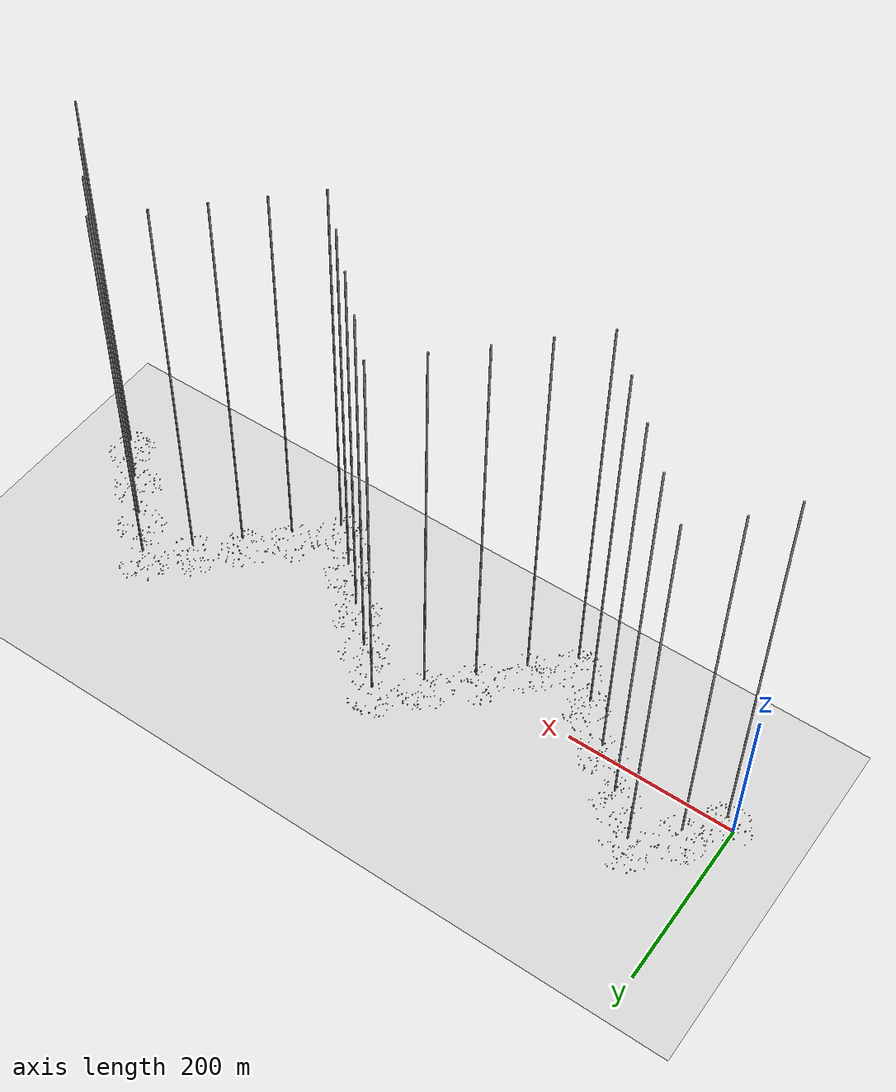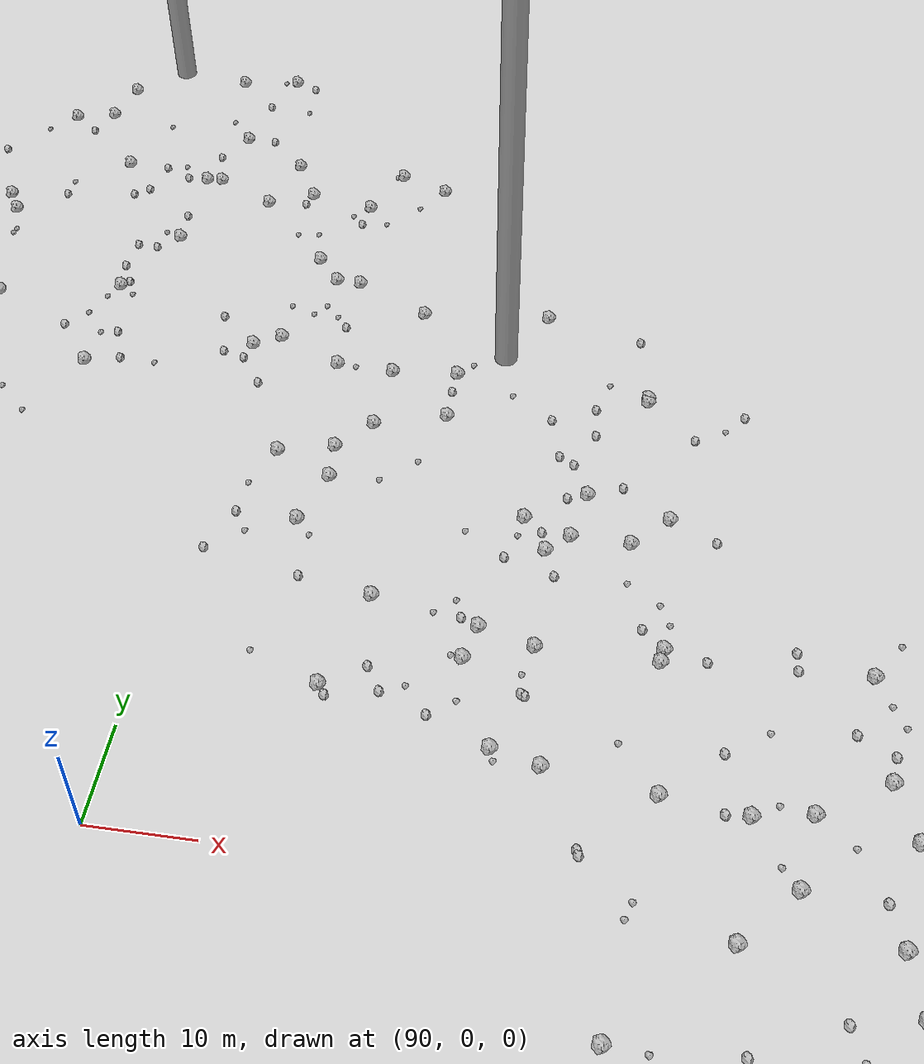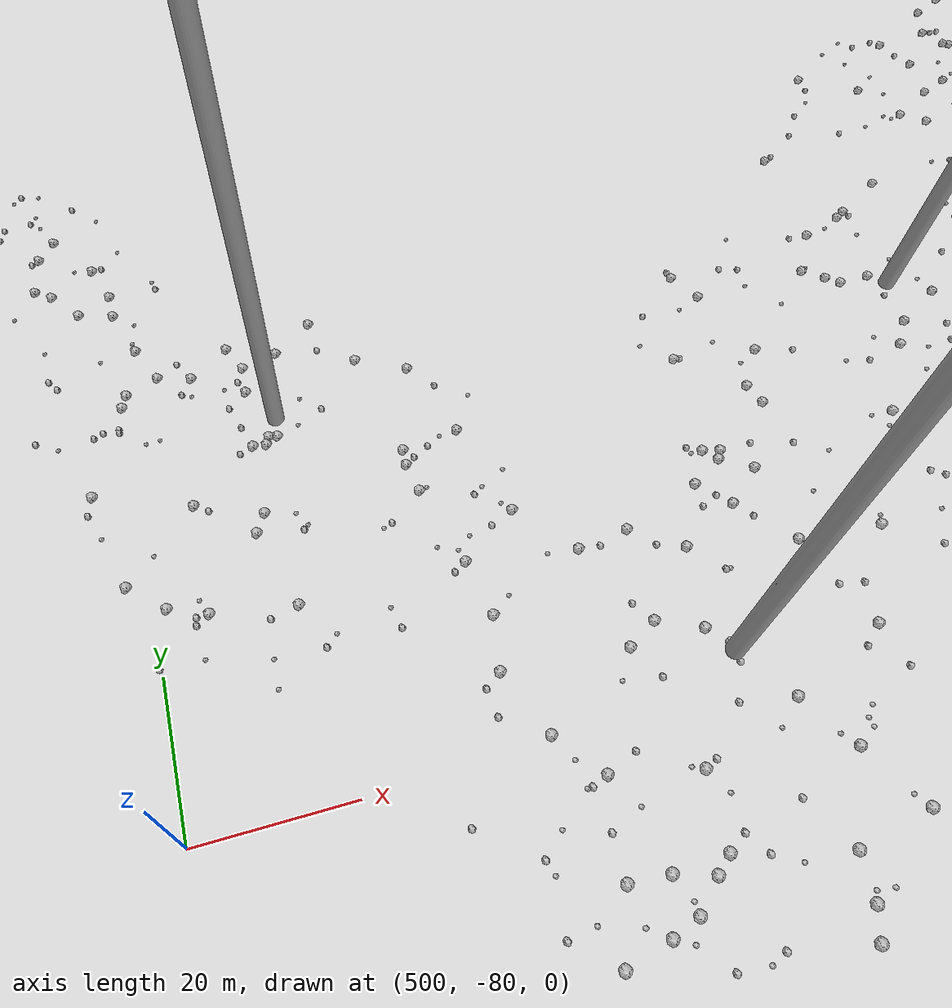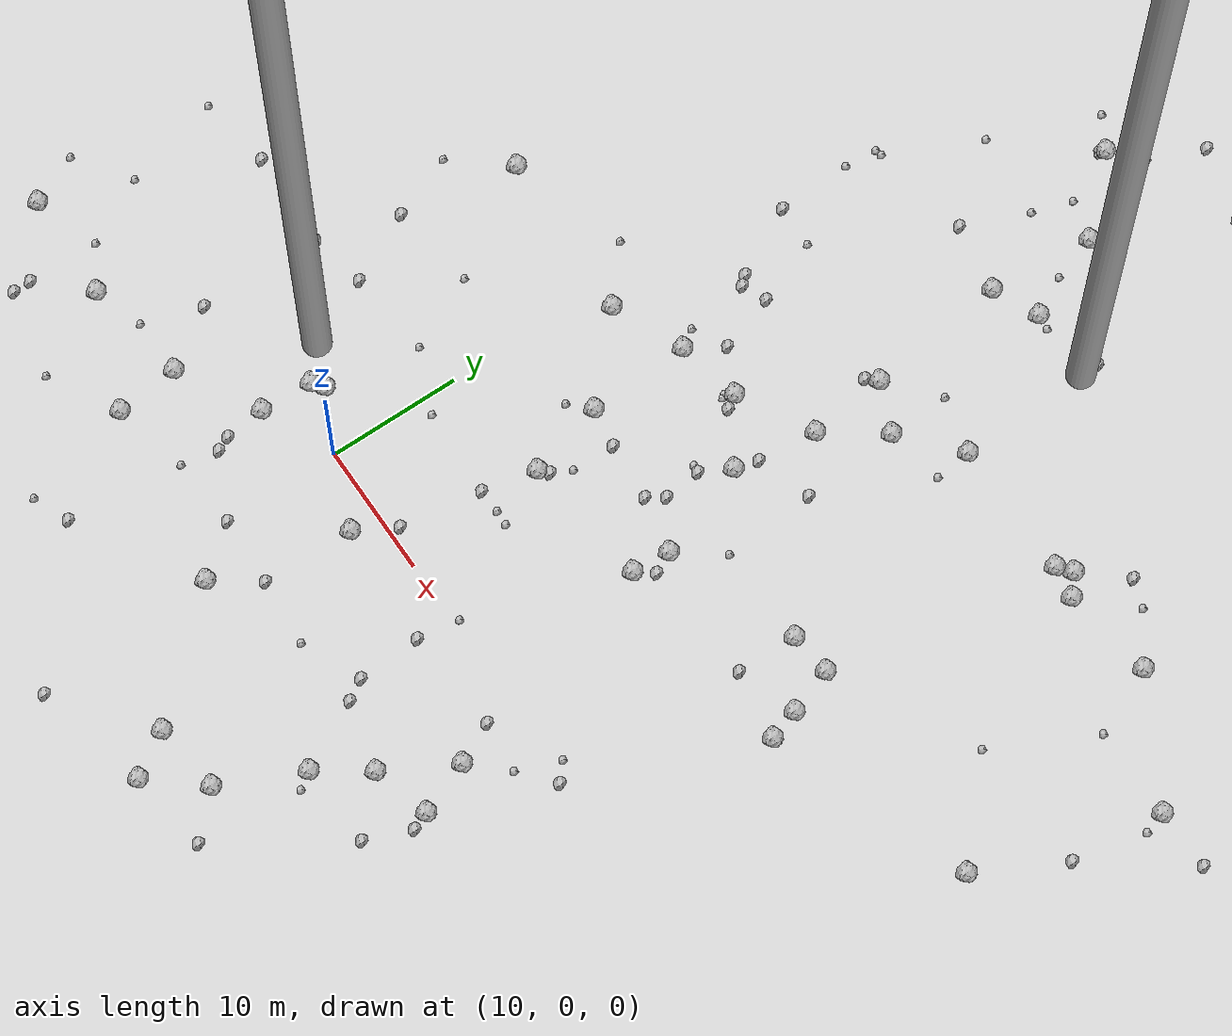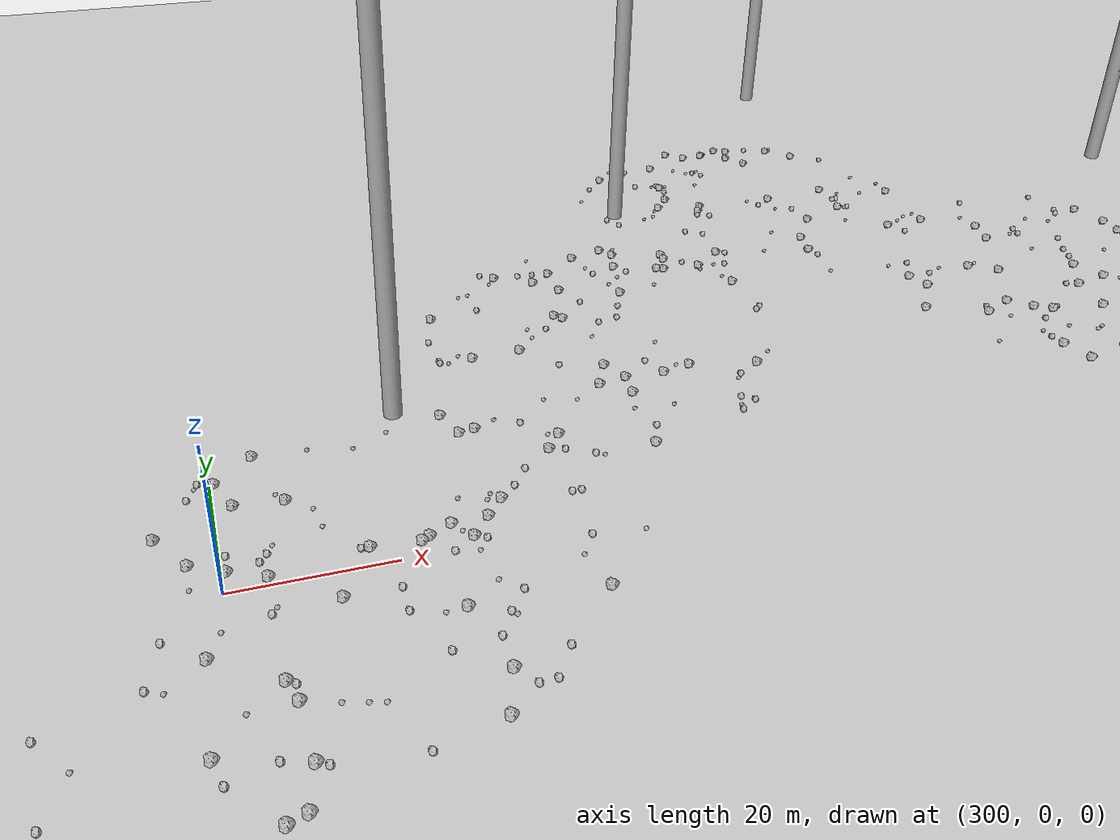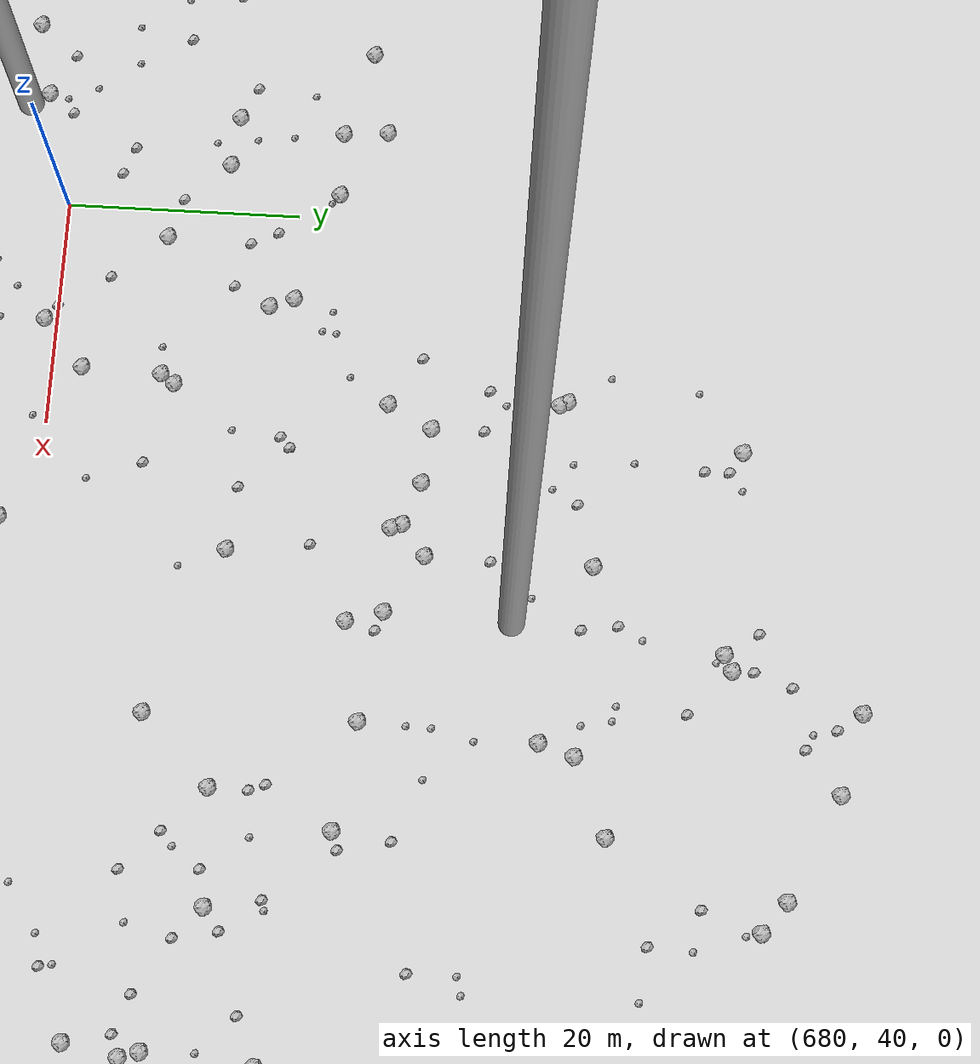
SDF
<sdf version="1.6">
 <world name="default">
  <include><uri>model://custom_ground</uri></include>
  <include><uri>model://sun</uri></include>
  <spherical_coordinates>
   <surface_model>EARTH_WGS84</surface_model>
   <latitude_deg>38.161479</latitude_deg>
   <longitude_deg>-122.454630</longitude_deg>
   <elevation>488.0</elevation>
   <heading_deg>90</heading_deg>
  </spherical_coordinates>
  <model name="rock1_0_0">
   <include><uri>model://rock1</uri><pose>4.722769837261527 1.522629581273435 0.5 0 0 0</pose></include>
  </model>
  <model name="rock1_0_1">
   <include><uri>model://rock1</uri><pose>-3.9891688747409297 -26.43252200253485 0.5 0 0 0</pose></include>
  </model>
  <model name="rock1_0_2">
   <include><uri>model://rock1</uri><pose>-9.582961832154771 -7.129383189320034 0.5 0 0 0</pose></include>
  </model>
  <model name="rock1_0_3">
   <include><uri>model://rock1</uri><pose>25.67066685512269 -20.027030334701024 0.5 0 0 0</pose></include>
  </model>
  <model name="rock1_0_4">
   <include><uri>model://rock1</uri><pose>4.540631685627254 -2.3999195949057714 0.5 0 0 0</pose></include>
  </model>
  <model name="rock1_0_5">
   <include><uri>model://rock1</uri><pose>20.43594853096844 -20.653183225990098 0.5 0 0 0</pose></include>
  </model>
  <model name="rock1_0_6">
   <include><uri>model://rock1</uri><pose>-17.76359626926095 -6.890915561591534 0.5 0 0 0</pose></include>
  </model>
  <model name="rock1_0_7">
   <include><uri>model://rock1</uri><pose>-1.022560300940608 22.69387455753236 0.5 0 0 0</pose></include>
  </model>
  <model name="rock1_0_8">
   <include><uri>model://rock1</uri><pose>-0.978680866877589 -10.558752813981215 0.5 0 0 0</pose></include>
  </model>
  <model name="rock1_0_9">
   <include><uri>model://rock1</uri><pose>17.17996941721217 24.4861453439568 0.5 0 0 0</pose></include>
  </model>
  <model name="rock1_0_10">
   <include><uri>model://rock1</uri><pose>5.264699876738938 -28.059158618863126 0.5 0 0 0</pose></include>
  </model>
  <model name="rock1_0_11">
   <include><uri>model://rock1</uri><pose>5.562285287720584 2.2056119319856577 0.5 0 0 0</pose></include>
  </model>
  <model name="rock1_0_12">
   <include><uri>model://rock1</uri><pose>12.961953235114379 -12.391206726731639 0.5 0 0 0</pose></include>
  </model>
  <model name="rock1_0_13">
   <include><uri>model://rock1</uri><pose>17.484339586572354 16.787691900462292 0.5 0 0 0</pose></include>
  </model>
  <model name="rock1_0_14">
   <include><uri>model://rock1</uri><pose>1.5112361324239032 -26.19524163940208 0.5 0 0 0</pose></include>
  </model>
  <model name="rock1_0_15">
   <include><uri>model://rock1</uri><pose>11.773759768425364 22.182301390779187 0.5 0 0 0</pose></include>
  </model>
  <model name="rock1_0_16">
   <include><uri>model://rock1</uri><pose>31.034075050161363 -10.28529207520964 0.5 0 0 0</pose></include>
  </model>
  <model name="rock1_0_17">
   <include><uri>model://rock1</uri><pose>28.450034182874177 -13.984544735497217 0.5 0 0 0</pose></include>
  </model>
  <model name="rock1_0_18">
   <include><uri>model://rock1</uri><pose>22.43879692771324 -23.821146042457407 0.5 0 0 0</pose></include>
  </model>
  <model name="rock1_0_19">
   <include><uri>model://rock1</uri><pose>35.40079748332063 -9.05072511468316 0.5 0 0 0</pose></include>
  </model>
  <model name="rock1_0_20">
   <include><uri>model://rock1</uri><pose>33.85666951743444 -5.115912305402052 0.5 0 0 0</pose></include>
  </model>
  <model name="rock1_0_21">
   <include><uri>model://rock1</uri><pose>-4.289096859611449 7.40284368862784 0.5 0 0 0</pose></include>
  </model>
  <model name="rock1_0_22">
   <include><uri>model://rock1</uri><pose>-1.468073630650526 -5.819344412199193 0.5 0 0 0</pose></include>
  </model>
  <model name="rock1_0_23">
   <include><uri>model://rock1</uri><pose>-8.040685558774154 -20.862407967158795 0.5 0 0 0</pose></include>
  </model>
  <model name="rock1_0_24">
   <include><uri>model://rock1</uri><pose>15.519145385335563 -2.1865867576316163 0.5 0 0 0</pose></include>
  </model>
  <model name="rock1_0_25">
   <include><uri>model://rock1</uri><pose>28.956954654316732 12.207446789412344 0.5 0 0 0</pose></include>
  </model>
  <model name="rock1_0_26">
   <include><uri>model://rock1</uri><pose>19.06600376842905 10.957989359607112 0.5 0 0 0</pose></include>
  </model>
  <model name="rock2_0_0">
   <include><uri>model://rock2</uri><pose>35.86238626600615 -10.31656989583508 0.3 0 0 0</pose></include>
  </model>
  <model name="rock2_0_1">
   <include><uri>model://rock2</uri><pose>20.45037724544808 16.342073221463536 0.3 0 0 0</pose></include>
  </model>
  <model name="rock2_0_2">
   <include><uri>model://rock2</uri><pose>4.8176310084578695 -5.3904361732760755 0.3 0 0 0</pose></include>
  </model>
  <model name="rock2_0_3">
   <include><uri>model://rock2</uri><pose>15.289379381229821 -9.034519548509927 0.3 0 0 0</pose></include>
  </model>
  <model name="rock2_0_4">
   <include><uri>model://rock2</uri><pose>38.687562532440204 -0.4293123871591469 0.3 0 0 0</pose></include>
  </model>
  <model name="rock2_0_5">
   <include><uri>model://rock2</uri><pose>17.140352257330328 0.8178198604435174 0.3 0 0 0</pose></include>
  </model>
  <model name="rock2_0_6">
   <include><uri>model://rock2</uri><pose>-12.949964424313361 -10.536893656231161 0.3 0 0 0</pose></include>
  </model>
  <model name="rock2_0_7">
   <include><uri>model://rock2</uri><pose>5.3269602024719624 -6.46967466327839 0.3 0 0 0</pose></include>
  </model>
  <model name="rock2_0_8">
   <include><uri>model://rock2</uri><pose>34.53421884672233 -13.71361628409009 0.3 0 0 0</pose></include>
  </model>
  <model name="rock2_0_9">
   <include><uri>model://rock2</uri><pose>25.687002975138938 17.2590276496975 0.3 0 0 0</pose></include>
  </model>
  <model name="rock2_0_10">
   <include><uri>model://rock2</uri><pose>25.366847194745503 20.083294864860548 0.3 0 0 0</pose></include>
  </model>
  <model name="rock2_0_11">
   <include><uri>model://rock2</uri><pose>25.788246771329867 -8.960757452583355 0.3 0 0 0</pose></include>
  </model>
  <model name="rock2_0_12">
   <include><uri>model://rock2</uri><pose>3.815596667148636 -17.82633322352133 0.3 0 0 0</pose></include>
  </model>
  <model name="rock2_0_13">
   <include><uri>model://rock2</uri><pose>18.103687575927772 6.9432492160919 0.3 0 0 0</pose></include>
  </model>
  <model name="rock2_0_14">
   <include><uri>model://rock2</uri><pose>-2.5666381233859603 13.869461619103923 0.3 0 0 0</pose></include>
  </model>
  <model name="rock2_0_15">
   <include><uri>model://rock2</uri><pose>24.867016889402926 -7.447371049224646 0.3 0 0 0</pose></include>
  </model>
  <model name="rock2_0_16">
   <include><uri>model://rock2</uri><pose>13.661434525210232 -25.874441411093745 0.3 0 0 0</pose></include>
  </model>
  <model name="rock2_0_17">
   <include><uri>model://rock2</uri><pose>-7.97741004208795 -23.080300150398287 0.3 0 0 0</pose></include>
  </model>
  <model name="rock2_0_18">
   <include><uri>model://rock2</uri><pose>24.63339694578154 -2.6954364390479384 0.3 0 0 0</pose></include>
  </model>
  <model name="rock2_0_19">
   <include><uri>model://rock2</uri><pose>10.080478093286398 -8.807532282692733 0.3 0 0 0</pose></include>
  </model>
  <model name="rock2_0_20">
   <include><uri>model://rock2</uri><pose>-12.905187410015495 -11.91290760320615 0.3 0 0 0</pose></include>
  </model>
  <model name="rock2_0_21">
   <include><uri>model://rock2</uri><pose>0.04217602326026437 8.631822806264324 0.3 0 0 0</pose></include>
  </model>
  <model name="rock2_0_22">
   <include><uri>model://rock2</uri><pose>28.50760428518955 -22.906934376159974 0.3 0 0 0</pose></include>
  </model>
  <model name="rock2_0_23">
   <include><uri>model://rock2</uri><pose>32.35939744405562 -2.1065265471798256 0.3 0 0 0</pose></include>
  </model>
  <model name="rock2_0_24">
   <include><uri>model://rock2</uri><pose>-4.427346339110921 -1.4577572983355154 0.3 0 0 0</pose></include>
  </model>
  <model name="rock2_0_25">
   <include><uri>model://rock2</uri><pose>19.64690390058169 11.599648767487999 0.3 0 0 0</pose></include>
  </model>
  <model name="rock2_0_26">
   <include><uri>model://rock2</uri><pose>-11.725143779301456 8.029404273288996 0.3 0 0 0</pose></include>
  </model>
  <model name="rock3_0_0">
   <include><uri>model://rock3</uri><pose>19.91234931486369 6.9841214080982965 0.2 0 0 0</pose></include>
  </model>
  <model name="rock3_0_1">
   <include><uri>model://rock3</uri><pose>-6.215285457167763 -13.44481928705282 0.2 0 0 0</pose></include>
  </model>
  <model name="rock3_0_2">
   <include><uri>model://rock3</uri><pose>7.857548536085989 25.497781062125483 0.2 0 0 0</pose></include>
  </model>
  <model name="rock3_0_3">
   <include><uri>model://rock3</uri><pose>4.053220220570687 14.816899280372468 0.2 0 0 0</pose></include>
  </model>
  <model name="rock3_0_4">
   <include><uri>model://rock3</uri><pose>24.770627603300007 20.16519344287679 0.2 0 0 0</pose></include>
  </model>
  <model name="rock3_0_5">
   <include><uri>model://rock3</uri><pose>36.209095037707755 -2.527490627004717 0.2 0 0 0</pose></include>
  </model>
  <model name="rock3_0_6">
   <include><uri>model://rock3</uri><pose>-17.449252870921956 7.140385223047815 0.2 0 0 0</pose></include>
  </model>
  <model name="rock3_0_7">
   <include><uri>model://rock3</uri><pose>29.196147014690965 -15.17419158757059 0.2 0 0 0</pose></include>
  </model>
  <model name="rock3_0_8">
   <include><uri>model://rock3</uri><pose>25.110101168900542 0.4240663873260644 0.2 0 0 0</pose></include>
  </model>
  <model name="rock3_0_9">
   <include><uri>model://rock3</uri><pose>20.384824183155516 -9.44966196952872 0.2 0 0 0</pose></include>
  </model>
  <model name="rock3_0_10">
   <include><uri>model://rock3</uri><pose>1.095785843801707 -18.97102816641098 0.2 0 0 0</pose></include>
  </model>
  <model name="rock3_0_11">
   <include><uri>model://rock3</uri><pose>16.225759641233495 25.85546288219279 0.2 0 0 0</pose></include>
  </model>
  <model name="rock3_0_12">
   <include><uri>model://rock3</uri><pose>6.6377164248097 9.319395425431793 0.2 0 0 0</pose></include>
  </model>
  <model name="rock3_0_13">
   <include><uri>model://rock3</uri><pose>-19.56181873187536 -3.1324893501158755 0.2 0 0 0</pose></include>
  </model>
  <model name="rock3_0_14">
   <include><uri>model://rock3</uri><pose>-4.495280339934416 18.68936587308128 0.2 0 0 0</pose></include>
  </model>
  <model name="rock3_0_15">
   <include><uri>model://rock3</uri><pose>5.743239610987786 2.4553271589625254 0.2 0 0 0</pose></include>
  </model>
  <model name="rock3_0_16">
   <include><uri>model://rock3</uri><pose>15.95775792245098 15.389041240747957 0.2 0 0 0</pose></include>
  </model>
  <model name="rock3_0_17">
   <include><uri>model://rock3</uri><pose>4.715554591178204 -9.233332429406826 0.2 0 0 0</pose></include>
  </model>
  <model name="rock3_0_18">
   <include><uri>model://rock3</uri><pose>20.351676691833546 13.056018059319435 0.2 0 0 0</pose></include>
  </model>
  <model name="rock3_0_19">
   <include><uri>model://rock3</uri><pose>-15.514557050628712 -0.2841083633749477 0.2 0 0 0</pose></include>
  </model>
  <model name="rock3_0_20">
   <include><uri>model://rock3</uri><pose>21.07248050785965 6.925163151397307 0.2 0 0 0</pose></include>
  </model>
  <model name="rock3_0_21">
   <include><uri>model://rock3</uri><pose>11.396854324696545 7.231133299345153 0.2 0 0 0</pose></include>
  </model>
  <model name="rock3_0_22">
   <include><uri>model://rock3</uri><pose>-12.872981282719048 -5.2019911820092695 0.2 0 0 0</pose></include>
  </model>
  <model name="rock3_0_23">
   <include><uri>model://rock3</uri><pose>37.403235735859695 0.6558345994390251 0.2 0 0 0</pose></include>
  </model>
  <model name="rock3_0_24">
   <include><uri>model://rock3</uri><pose>21.73782820723384 24.676152016817234 0.2 0 0 0</pose></include>
  </model>
  <model name="rock3_0_25">
   <include><uri>model://rock3</uri><pose>-12.892162455268254 -14.825040673532587 0.2 0 0 0</pose></include>
  </model>
  <model name="rock3_0_26">
   <include><uri>model://rock3</uri><pose>-5.845182253737715 -5.90117449476169 0.2 0 0 0</pose></include>
  </model>
  <model name="rock1_1_0">
   <include><uri>model://rock1</uri><pose>59.33406490043262 18.567876244680704 0.5 0 0 0</pose></include>
  </model>
  <model name="rock1_1_1">
   <include><uri>model://rock1</uri><pose>25.74081650989842 44.99801692024075 0.5 0 0 0</pose></include>
  </model>
  <model name="rock1_1_2">
   <include><uri>model://rock1</uri><pose>27.581874556690895 28.50488178268986 0.5 0 0 0</pose></include>
  </model>
  <model name="rock1_1_3">
   <include><uri>model://rock1</uri><pose>29.18836228678742 46.55236089905917 0.5 0 0 0</pose></include>
  </model>
  <model name="rock1_1_4">
   <include><uri>model://rock1</uri><pose>43.49872294798154 15.591291298474426 0.5 0 0 0</pose></include>
  </model>
  <model name="rock1_1_5">
   <include><uri>model://rock1</uri><pose>31.342874589424945 62.70781845946969 0.5 0 0 0</pose></include>
  </model>
  <model name="rock1_1_6">
   <include><uri>model://rock1</uri><pose>22.077564220592055 25.47851417373085 0.5 0 0 0</pose></include>
  </model>
  <model name="rock1_1_7">
   <include><uri>model://rock1</uri><pose>54.64256528877002 57.84715444888412 0.5 0 0 0</pose></include>
  </model>
  <model name="rock1_1_8">
   <include><uri>model://rock1</uri><pose>44.996985035795525 36.39047279850777 0.5 0 0 0</pose></include>
  </model>
  <model name="rock1_1_9">
   <include><uri>model://rock1</uri><pose>34.79852922947078 36.37239471679473 0.5 0 0 0</pose></include>
  </model>
  <model name="rock1_1_10">
   <include><uri>model://rock1</uri><pose>47.46254936364881 36.01003540594522 0.5 0 0 0</pose></include>
  </model>
  <model name="rock1_1_11">
   <include><uri>model://rock1</uri><pose>63.36971520869519 31.940183021988805 0.5 0 0 0</pose></include>
  </model>
  <model name="rock1_1_12">
   <include><uri>model://rock1</uri><pose>39.11513409567462 18.65441581833386 0.5 0 0 0</pose></include>
  </model>
  <model name="rock1_1_13">
   <include><uri>model://rock1</uri><pose>43.83237734480147 69.15558945201451 0.5 0 0 0</pose></include>
  </model>
  <model name="rock1_1_14">
   <include><uri>model://rock1</uri><pose>26.493440912283965 52.904234770160166 0.5 0 0 0</pose></include>
  </model>
  <model name="rock1_1_15">
   <include><uri>model://rock1</uri><pose>21.569634850836533 57.93983210139749 0.5 0 0 0</pose></include>
  </model>
  <model name="rock1_1_16">
   <include><uri>model://rock1</uri><pose>44.93221161911088 55.498819712141575 0.5 0 0 0</pose></include>
  </model>
  <model name="rock1_1_17">
   <include><uri>model://rock1</uri><pose>29.17427724353153 15.079297747723071 0.5 0 0 0</pose></include>
  </model>
  <model name="rock1_1_18">
   <include><uri>model://rock1</uri><pose>30.657030637814874 32.81629704262875 0.5 0 0 0</pose></include>
  </model>
  <model name="rock1_1_19">
   <include><uri>model://rock1</uri><pose>44.23219238784546 13.279619686222695 0.5 0 0 0</pose></include>
  </model>
  <model name="rock1_1_20">
   <include><uri>model://rock1</uri><pose>54.37919379454312 37.006354357160134 0.5 0 0 0</pose></include>
  </model>
  <model name="rock1_1_21">
   <include><uri>model://rock1</uri><pose>54.07815490411358 61.637350910298935 0.5 0 0 0</pose></include>
  </model>
  <model name="rock1_1_22">
   <include><uri>model://rock1</uri><pose>46.03623966362888 37.230885969497294 0.5 0 0 0</pose></include>
  </model>
  <model name="rock1_1_23">
   <include><uri>model://rock1</uri><pose>26.949940171593656 34.43033018014482 0.5 0 0 0</pose></include>
  </model>
  <model name="rock1_1_24">
   <include><uri>model://rock1</uri><pose>26.634014988778745 22.2835743253912 0.5 0 0 0</pose></include>
  </model>
  <model name="rock1_1_25">
   <include><uri>model://rock1</uri><pose>34.78937306228137 66.10424025105061 0.5 0 0 0</pose></include>
  </model>
  <model name="rock1_1_26">
   <include><uri>model://rock1</uri><pose>42.32199398945255 18.997980832204696 0.5 0 0 0</pose></include>
  </model>
  <model name="rock2_1_0">
   <include><uri>model://rock2</uri><pose>14.96966970642676 31.33443057795101 0.3 0 0 0</pose></include>
  </model>
  <model name="rock2_1_1">
   <include><uri>model://rock2</uri><pose>25.416521624780277 64.08371603206297 0.3 0 0 0</pose></include>
  </model>
  <model name="rock2_1_2">
   <include><uri>model://rock2</uri><pose>29.89941409503068 13.54103279038116 0.3 0 0 0</pose></include>
  </model>
  <model name="rock2_1_3">
   <include><uri>model://rock2</uri><pose>31.146532108906214 25.427644352702686 0.3 0 0 0</pose></include>
  </model>
  <model name="rock2_1_4">
   <include><uri>model://rock2</uri><pose>67.85968787269894 32.03905877457623 0.3 0 0 0</pose></include>
  </model>
  <model name="rock2_1_5">
   <include><uri>model://rock2</uri><pose>23.705744216341884 59.88149341775693 0.3 0 0 0</pose></include>
  </model>
  <model name="rock2_1_6">
   <include><uri>model://rock2</uri><pose>18.761892601320525 27.189954629487186 0.3 0 0 0</pose></include>
  </model>
  <model name="rock2_1_7">
   <include><uri>model://rock2</uri><pose>41.67133599496334 58.76375360457305 0.3 0 0 0</pose></include>
  </model>
  <model name="rock2_1_8">
   <include><uri>model://rock2</uri><pose>34.46960969259857 47.7829606001367 0.3 0 0 0</pose></include>
  </model>
  <model name="rock2_1_9">
   <include><uri>model://rock2</uri><pose>20.442749504199686 45.97085551501643 0.3 0 0 0</pose></include>
  </model>
  <model name="rock2_1_10">
   <include><uri>model://rock2</uri><pose>17.362915487684536 31.460298273759552 0.3 0 0 0</pose></include>
  </model>
  <model name="rock2_1_11">
   <include><uri>model://rock2</uri><pose>65.63179048652357 37.09115624978617 0.3 0 0 0</pose></include>
  </model>
  <model name="rock2_1_12">
   <include><uri>model://rock2</uri><pose>24.84570019158621 15.999376831445227 0.3 0 0 0</pose></include>
  </model>
  <model name="rock2_1_13">
   <include><uri>model://rock2</uri><pose>55.648773066713986 58.7043767454857 0.3 0 0 0</pose></include>
  </model>
  <model name="rock2_1_14">
   <include><uri>model://rock2</uri><pose>26.159495886742707 33.71555318960226 0.3 0 0 0</pose></include>
  </model>
  <model name="rock2_1_15">
   <include><uri>model://rock2</uri><pose>21.34894829436179 57.61793221553424 0.3 0 0 0</pose></include>
  </model>
  <model name="rock2_1_16">
   <include><uri>model://rock2</uri><pose>48.66993986613075 40.384104333647 0.3 0 0 0</pose></include>
  </model>
  <model name="rock2_1_17">
   <include><uri>model://rock2</uri><pose>22.66706023563355 24.54928167229244 0.3 0 0 0</pose></include>
  </model>
  <model name="rock2_1_18">
   <include><uri>model://rock2</uri><pose>56.803648043168124 61.50454227167129 0.3 0 0 0</pose></include>
  </model>
  <model name="rock2_1_19">
   <include><uri>model://rock2</uri><pose>15.545726118569787 30.688400605444798 0.3 0 0 0</pose></include>
  </model>
  <model name="rock2_1_20">
   <include><uri>model://rock2</uri><pose>27.036305940414312 24.087693085968965 0.3 0 0 0</pose></include>
  </model>
  <model name="rock2_1_21">
   <include><uri>model://rock2</uri><pose>62.61274851422417 24.948342795664345 0.3 0 0 0</pose></include>
  </model>
  <model name="rock2_1_22">
   <include><uri>model://rock2</uri><pose>32.34850338393597 67.3280620182307 0.3 0 0 0</pose></include>
  </model>
  <model name="rock2_1_23">
   <include><uri>model://rock2</uri><pose>38.96927455241847 14.132516012351592 0.3 0 0 0</pose></include>
  </model>
  <model name="rock2_1_24">
   <include><uri>model://rock2</uri><pose>57.44496049869136 62.020793771548156 0.3 0 0 0</pose></include>
  </model>
  <model name="rock2_1_25">
   <include><uri>model://rock2</uri><pose>12.275024799038405 36.439177470277045 0.3 0 0 0</pose></include>
  </model>
  <model name="rock2_1_26">
   <include><uri>model://rock2</uri><pose>30.063311492893195 52.22033019367821 0.3 0 0 0</pose></include>
  </model>
  <model name="rock3_1_0">
   <include><uri>model://rock3</uri><pose>23.361010417336033 53.77430486476464 0.2 0 0 0</pose></include>
  </model>
  <model name="rock3_1_1">
   <include><uri>model://rock3</uri><pose>12.25747311378779 44.512200838625816 0.2 0 0 0</pose></include>
  </model>
  <model name="rock3_1_2">
   <include><uri>model://rock3</uri><pose>60.23009139201076 47.56229481383756 0.2 0 0 0</pose></include>
  </model>
  <model name="rock3_1_3">
   <include><uri>model://rock3</uri><pose>42.95373833367262 61.02334924042645 0.2 0 0 0</pose></include>
  </model>
  <model name="rock3_1_4">
   <include><uri>model://rock3</uri><pose>35.03116551842831 33.623671629371614 0.2 0 0 0</pose></include>
  </model>
  <model name="rock3_1_5">
   <include><uri>model://rock3</uri><pose>22.408997920613757 50.81278294019575 0.2 0 0 0</pose></include>
  </model>
  <model name="rock3_1_6">
   <include><uri>model://rock3</uri><pose>50.768078222986894 39.60917977043141 0.2 0 0 0</pose></include>
  </model>
  <model name="rock3_1_7">
   <include><uri>model://rock3</uri><pose>63.82361907745647 30.29585410167501 0.2 0 0 0</pose></include>
  </model>
  <model name="rock3_1_8">
   <include><uri>model://rock3</uri><pose>12.058607792652221 42.0421680764205 0.2 0 0 0</pose></include>
  </model>
  <model name="rock3_1_9">
   <include><uri>model://rock3</uri><pose>68.90433771048818 46.21488203111494 0.2 0 0 0</pose></include>
  </model>
  <model name="rock3_1_10">
   <include><uri>model://rock3</uri><pose>30.27381670656308 46.449925601226035 0.2 0 0 0</pose></include>
  </model>
  <model name="rock3_1_11">
   <include><uri>model://rock3</uri><pose>12.762242757298885 44.638799472328905 0.2 0 0 0</pose></include>
  </model>
  <model name="rock3_1_12">
   <include><uri>model://rock3</uri><pose>52.800816500176275 24.555586963746496 0.2 0 0 0</pose></include>
  </model>
  <model name="rock3_1_13">
   <include><uri>model://rock3</uri><pose>65.61036863910297 49.461197485046135 0.2 0 0 0</pose></include>
  </model>
  <model name="rock3_1_14">
   <include><uri>model://rock3</uri><pose>62.525005846004014 46.402200272598634 0.2 0 0 0</pose></include>
  </model>
  <model name="rock3_1_15">
   <include><uri>model://rock3</uri><pose>19.042951385367097 59.47668709011956 0.2 0 0 0</pose></include>
  </model>
  <model name="rock3_1_16">
   <include><uri>model://rock3</uri><pose>30.444515469128394 37.503029355845975 0.2 0 0 0</pose></include>
  </model>
  <model name="rock3_1_17">
   <include><uri>model://rock3</uri><pose>15.975382949853955 51.50297624287392 0.2 0 0 0</pose></include>
  </model>
  <model name="rock3_1_18">
   <include><uri>model://rock3</uri><pose>21.23296409464304 60.292374663157936 0.2 0 0 0</pose></include>
  </model>
  <model name="rock3_1_19">
   <include><uri>model://rock3</uri><pose>56.54146614237851 31.99195355282108 0.2 0 0 0</pose></include>
  </model>
  <model name="rock3_1_20">
   <include><uri>model://rock3</uri><pose>15.494308731836611 36.28771686200125 0.2 0 0 0</pose></include>
  </model>
  <model name="rock3_1_21">
   <include><uri>model://rock3</uri><pose>49.43909066737584 66.68285416470782 0.2 0 0 0</pose></include>
  </model>
  <model name="rock3_1_22">
   <include><uri>model://rock3</uri><pose>65.91424066397005 43.5338162429731 0.2 0 0 0</pose></include>
  </model>
  <model name="rock3_1_23">
   <include><uri>model://rock3</uri><pose>27.551869341334225 49.464646346142594 0.2 0 0 0</pose></include>
  </model>
  <model name="rock3_1_24">
   <include><uri>model://rock3</uri><pose>21.59362594973865 24.903963620918404 0.2 0 0 0</pose></include>
  </model>
  <model name="rock3_1_25">
   <include><uri>model://rock3</uri><pose>45.41969093599357 52.711024819685335 0.2 0 0 0</pose></include>
  </model>
  <model name="rock3_1_26">
   <include><uri>model://rock3</uri><pose>31.570447423494695 18.435511432829298 0.2 0 0 0</pose></include>
  </model>
  <model name="rock1_2_0">
   <include><uri>model://rock1</uri><pose>90.38497741954664 59.47419520804467 0.5 0 0 0</pose></include>
  </model>
  <model name="rock1_2_1">
   <include><uri>model://rock1</uri><pose>101.40767075957496 91.31324267149532 0.5 0 0 0</pose></include>
  </model>
  <model name="rock1_2_2">
   <include><uri>model://rock1</uri><pose>91.35911896836322 86.2087138313087 0.5 0 0 0</pose></include>
  </model>
  <model name="rock1_2_3">
   <include><uri>model://rock1</uri><pose>67.90132348796509 89.19172251917499 0.5 0 0 0</pose></include>
  </model>
  <model name="rock1_2_4">
   <include><uri>model://rock1</uri><pose>73.09346552789559 54.409357618113454 0.5 0 0 0</pose></include>
  </model>
  <model name="rock1_2_5">
   <include><uri>model://rock1</uri><pose>57.13078340534561 78.64323120915873 0.5 0 0 0</pose></include>
  </model>
  <model name="rock1_2_6">
   <include><uri>model://rock1</uri><pose>86.40057015791339 84.01632126775434 0.5 0 0 0</pose></include>
  </model>
  <model name="rock1_2_7">
   <include><uri>model://rock1</uri><pose>88.59634436356762 91.54235272794884 0.5 0 0 0</pose></include>
  </model>
  <model name="rock1_2_8">
   <include><uri>model://rock1</uri><pose>98.54959022139393 84.73183382029416 0.5 0 0 0</pose></include>
  </model>
  <model name="rock1_2_9">
   <include><uri>model://rock1</uri><pose>79.8067863335898 87.499266475529 0.5 0 0 0</pose></include>
  </model>
  <model name="rock1_2_10">
   <include><uri>model://rock1</uri><pose>84.32149265884556 109.21161508903235 0.5 0 0 0</pose></include>
  </model>
  <model name="rock1_2_11">
   <include><uri>model://rock1</uri><pose>77.70668046691642 76.1809755446166 0.5 0 0 0</pose></include>
  </model>
  <model name="rock1_2_12">
   <include><uri>model://rock1</uri><pose>81.02032626818968 96.1553263228205 0.5 0 0 0</pose></include>
  </model>
  <model name="rock1_2_13">
   <include><uri>model://rock1</uri><pose>62.925477578273274 98.9378276878289 0.5 0 0 0</pose></include>
  </model>
  <model name="rock1_2_14">
   <include><uri>model://rock1</uri><pose>77.63097005347159 108.20265900863322 0.5 0 0 0</pose></include>
  </model>
  <model name="rock1_2_15">
   <include><uri>model://rock1</uri><pose>78.01127471573706 87.3819449660786 0.5 0 0 0</pose></include>
  </model>
  <model name="rock1_2_16">
   <include><uri>model://rock1</uri><pose>97.2663948109321 71.20808792924178 0.5 0 0 0</pose></include>
  </model>
  <model name="rock1_2_17">
   <include><uri>model://rock1</uri><pose>55.600304960246525 81.30415698036398 0.5 0 0 0</pose></include>
  </model>
  <model name="rock1_2_18">
   <include><uri>model://rock1</uri><pose>58.46020180076185 97.78870815548893 0.5 0 0 0</pose></include>
  </model>
  <model name="rock1_2_19">
   <include><uri>model://rock1</uri><pose>64.26950353426926 104.54850488598154 0.5 0 0 0</pose></include>
  </model>
  <model name="rock1_2_20">
   <include><uri>model://rock1</uri><pose>94.62959711521704 74.54719343449202 0.5 0 0 0</pose></include>
  </model>
  <model name="rock1_2_21">
   <include><uri>model://rock1</uri><pose>106.80028104339888 89.04913927460343 0.5 0 0 0</pose></include>
  </model>
  <model name="rock1_2_22">
   <include><uri>model://rock1</uri><pose>93.1958971934547 61.052620394365874 0.5 0 0 0</pose></include>
  </model>
  <model name="rock1_2_23">
   <include><uri>model://rock1</uri><pose>99.95964086939146 71.02107926300874 0.5 0 0 0</pose></include>
  </model>
  <model name="rock1_2_24">
   <include><uri>model://rock1</uri><pose>73.39930499811666 66.84032662102767 0.5 0 0 0</pose></include>
  </model>
  <model name="rock1_2_25">
   <include><uri>model://rock1</uri><pose>60.1680042698499 64.13759689363312 0.5 0 0 0</pose></include>
  </model>
  <model name="rock1_2_26">
   <include><uri>model://rock1</uri><pose>100.02774727471973 57.72451878270234 0.5 0 0 0</pose></include>
  </model>
  <model name="rock2_2_0">
   <include><uri>model://rock2</uri><pose>75.51804468030906 74.1285439936234 0.3 0 0 0</pose></include>
  </model>
  <model name="rock2_2_1">
   <include><uri>model://rock2</uri><pose>69.15661839940539 59.72218736602912 0.3 0 0 0</pose></include>
  </model>
  <model name="rock2_2_2">
   <include><uri>model://rock2</uri><pose>74.1803249408908 67.70864845148719 0.3 0 0 0</pose></include>
  </model>
  <model name="rock2_2_3">
   <include><uri>model://rock2</uri><pose>73.30276247389824 74.2190688010391 0.3 0 0 0</pose></include>
  </model>
  <model name="rock2_2_4">
   <include><uri>model://rock2</uri><pose>90.79056935852323 84.45765582209 0.3 0 0 0</pose></include>
  </model>
  <model name="rock2_2_5">
   <include><uri>model://rock2</uri><pose>86.2230920987749 63.476835918031 0.3 0 0 0</pose></include>
  </model>
  <model name="rock2_2_6">
   <include><uri>model://rock2</uri><pose>52.00510776882483 89.94246224599112 0.3 0 0 0</pose></include>
  </model>
  <model name="rock2_2_7">
   <include><uri>model://rock2</uri><pose>89.83343559909218 57.29187051224945 0.3 0 0 0</pose></include>
  </model>
  <model name="rock2_2_8">
   <include><uri>model://rock2</uri><pose>87.48186221612686 58.023804727643494 0.3 0 0 0</pose></include>
  </model>
  <model name="rock2_2_9">
   <include><uri>model://rock2</uri><pose>76.74786820563062 55.35232127901801 0.3 0 0 0</pose></include>
  </model>
  <model name="rock2_2_10">
   <include><uri>model://rock2</uri><pose>86.91505300748574 108.11860951401778 0.3 0 0 0</pose></include>
  </model>
  <model name="rock2_2_11">
   <include><uri>model://rock2</uri><pose>62.185698142400184 82.31030927005062 0.3 0 0 0</pose></include>
  </model>
  <model name="rock2_2_12">
   <include><uri>model://rock2</uri><pose>53.18687681940078 81.608239087735 0.3 0 0 0</pose></include>
  </model>
  <model name="rock2_2_13">
   <include><uri>model://rock2</uri><pose>98.08825582674325 81.65454651300637 0.3 0 0 0</pose></include>
  </model>
  <model name="rock2_2_14">
   <include><uri>model://rock2</uri><pose>92.26284718596654 53.74552086750177 0.3 0 0 0</pose></include>
  </model>
  <model name="rock2_2_15">
   <include><uri>model://rock2</uri><pose>99.78394544703599 63.61928151762561 0.3 0 0 0</pose></include>
  </model>
  <model name="rock2_2_16">
   <include><uri>model://rock2</uri><pose>61.463739949969124 95.29552825454232 0.3 0 0 0</pose></include>
  </model>
  <model name="rock2_2_17">
   <include><uri>model://rock2</uri><pose>75.30389509824653 59.33047281079767 0.3 0 0 0</pose></include>
  </model>
  <model name="rock2_2_18">
   <include><uri>model://rock2</uri><pose>72.92577548570685 70.34447815366899 0.3 0 0 0</pose></include>
  </model>
  <model name="rock2_2_19">
   <include><uri>model://rock2</uri><pose>72.63642014792111 89.02473551047409 0.3 0 0 0</pose></include>
  </model>
  <model name="rock2_2_20">
   <include><uri>model://rock2</uri><pose>77.52858056767359 80.21021316858926 0.3 0 0 0</pose></include>
  </model>
  <model name="rock2_2_21">
   <include><uri>model://rock2</uri><pose>78.61808673305555 92.05461923106404 0.3 0 0 0</pose></include>
  </model>
  <model name="rock2_2_22">
   <include><uri>model://rock2</uri><pose>70.08439273736725 83.37726975023546 0.3 0 0 0</pose></include>
  </model>
  <model name="rock2_2_23">
   <include><uri>model://rock2</uri><pose>84.32081115207477 96.16430355909472 0.3 0 0 0</pose></include>
  </model>
  <model name="rock2_2_24">
   <include><uri>model://rock2</uri><pose>82.20322440438892 103.4764976438221 0.3 0 0 0</pose></include>
  </model>
  <model name="rock2_2_25">
   <include><uri>model://rock2</uri><pose>71.65690827803641 84.57822137433297 0.3 0 0 0</pose></include>
  </model>
  <model name="rock2_2_26">
   <include><uri>model://rock2</uri><pose>75.69087456764436 87.42314384680293 0.3 0 0 0</pose></include>
  </model>
  <model name="rock3_2_0">
   <include><uri>model://rock3</uri><pose>100.63388475264108 91.24376565110309 0.2 0 0 0</pose></include>
  </model>
  <model name="rock3_2_1">
   <include><uri>model://rock3</uri><pose>93.4147880043902 79.09784420343733 0.2 0 0 0</pose></include>
  </model>
  <model name="rock3_2_2">
   <include><uri>model://rock3</uri><pose>75.83512288670585 76.93692288905073 0.2 0 0 0</pose></include>
  </model>
  <model name="rock3_2_3">
   <include><uri>model://rock3</uri><pose>87.15611333273246 102.9895233079163 0.2 0 0 0</pose></include>
  </model>
  <model name="rock3_2_4">
   <include><uri>model://rock3</uri><pose>55.71983856513765 94.88333646490766 0.2 0 0 0</pose></include>
  </model>
  <model name="rock3_2_5">
   <include><uri>model://rock3</uri><pose>75.03204148486478 65.66540272436157 0.2 0 0 0</pose></include>
  </model>
  <model name="rock3_2_6">
   <include><uri>model://rock3</uri><pose>72.3516384021948 64.95642715264354 0.2 0 0 0</pose></include>
  </model>
  <model name="rock3_2_7">
   <include><uri>model://rock3</uri><pose>98.52867797226534 65.18483289743315 0.2 0 0 0</pose></include>
  </model>
  <model name="rock3_2_8">
   <include><uri>model://rock3</uri><pose>96.78087867420611 83.01783135062863 0.2 0 0 0</pose></include>
  </model>
  <model name="rock3_2_9">
   <include><uri>model://rock3</uri><pose>71.13038147824794 62.01390489200325 0.2 0 0 0</pose></include>
  </model>
  <model name="rock3_2_10">
   <include><uri>model://rock3</uri><pose>62.21877873487663 84.78999950082724 0.2 0 0 0</pose></include>
  </model>
  <model name="rock3_2_11">
   <include><uri>model://rock3</uri><pose>96.96526286922747 66.85259303651969 0.2 0 0 0</pose></include>
  </model>
  <model name="rock3_2_12">
   <include><uri>model://rock3</uri><pose>91.07498138112491 78.72656755313571 0.2 0 0 0</pose></include>
  </model>
  <model name="rock3_2_13">
   <include><uri>model://rock3</uri><pose>78.32793931943576 99.63086831125426 0.2 0 0 0</pose></include>
  </model>
  <model name="rock3_2_14">
   <include><uri>model://rock3</uri><pose>82.8254226595328 109.07176824094202 0.2 0 0 0</pose></include>
  </model>
  <model name="rock3_2_15">
   <include><uri>model://rock3</uri><pose>100.88024965898882 82.1069892404014 0.2 0 0 0</pose></include>
  </model>
  <model name="rock3_2_16">
   <include><uri>model://rock3</uri><pose>58.251569871462955 75.05418555754251 0.2 0 0 0</pose></include>
  </model>
  <model name="rock3_2_17">
   <include><uri>model://rock3</uri><pose>70.81351582940704 97.50980602890942 0.2 0 0 0</pose></include>
  </model>
  <model name="rock3_2_18">
   <include><uri>model://rock3</uri><pose>58.105070482843686 74.33703903351002 0.2 0 0 0</pose></include>
  </model>
  <model name="rock3_2_19">
   <include><uri>model://rock3</uri><pose>74.8192645305779 89.61871641146028 0.2 0 0 0</pose></include>
  </model>
  <model name="rock3_2_20">
   <include><uri>model://rock3</uri><pose>104.29385667213147 85.62583353867475 0.2 0 0 0</pose></include>
  </model>
  <model name="rock3_2_21">
   <include><uri>model://rock3</uri><pose>73.39180883050574 59.05079110033631 0.2 0 0 0</pose></include>
  </model>
  <model name="rock3_2_22">
   <include><uri>model://rock3</uri><pose>59.69790526899658 58.488878946488725 0.2 0 0 0</pose></include>
  </model>
  <model name="rock3_2_23">
   <include><uri>model://rock3</uri><pose>95.80786618497808 65.3353704785779 0.2 0 0 0</pose></include>
  </model>
  <model name="rock3_2_24">
   <include><uri>model://rock3</uri><pose>51.944402490903656 83.81002100341757 0.2 0 0 0</pose></include>
  </model>
  <model name="rock3_2_25">
   <include><uri>model://rock3</uri><pose>80.50765276469497 55.16821931398389 0.2 0 0 0</pose></include>
  </model>
  <model name="rock3_2_26">
   <include><uri>model://rock3</uri><pose>93.15568130186486 66.28413322896084 0.2 0 0 0</pose></include>
  </model>
  <model name="rock1_3_0">
   <include><uri>model://rock1</uri><pose>128.17887364294813 42.70601743403135 0.5 0 0 0</pose></include>
  </model>
  <model name="rock1_3_1">
   <include><uri>model://rock1</uri><pose>127.10583014797885 10.964110498592643 0.5 0 0 0</pose></include>
  </model>
  <model name="rock1_3_2">
   <include><uri>model://rock1</uri><pose>124.84855671809288 35.01984554508704 0.5 0 0 0</pose></include>
  </model>
  <model name="rock1_3_3">
   <include><uri>model://rock1</uri><pose>132.9133877173661 36.970612048451954 0.5 0 0 0</pose></include>
  </model>
  <model name="rock1_3_4">
   <include><uri>model://rock1</uri><pose>136.5563721770204 23.411505800237602 0.5 0 0 0</pose></include>
  </model>
  <model name="rock1_3_5">
   <include><uri>model://rock1</uri><pose>133.2446727154171 56.60702123226995 0.5 0 0 0</pose></include>
  </model>
  <model name="rock1_3_6">
   <include><uri>model://rock1</uri><pose>106.06600931216366 57.36330319441352 0.5 0 0 0</pose></include>
  </model>
  <model name="rock1_3_7">
   <include><uri>model://rock1</uri><pose>102.19457537316671 45.678460714466055 0.5 0 0 0</pose></include>
  </model>
  <model name="rock1_3_8">
   <include><uri>model://rock1</uri><pose>133.21481810824108 57.19160658193252 0.5 0 0 0</pose></include>
  </model>
  <model name="rock1_3_9">
   <include><uri>model://rock1</uri><pose>100.48606308012236 35.50821103970221 0.5 0 0 0</pose></include>
  </model>
  <model name="rock1_3_10">
   <include><uri>model://rock1</uri><pose>122.36462991345175 38.85771158820266 0.5 0 0 0</pose></include>
  </model>
  <model name="rock1_3_11">
   <include><uri>model://rock1</uri><pose>112.78366351142397 51.60665838759616 0.5 0 0 0</pose></include>
  </model>
  <model name="rock1_3_12">
   <include><uri>model://rock1</uri><pose>136.80224546578458 24.85167134307644 0.5 0 0 0</pose></include>
  </model>
  <model name="rock1_3_13">
   <include><uri>model://rock1</uri><pose>102.4547701227724 41.51215942551288 0.5 0 0 0</pose></include>
  </model>
  <model name="rock1_3_14">
   <include><uri>model://rock1</uri><pose>127.05679550500626 37.12074580128582 0.5 0 0 0</pose></include>
  </model>
  <model name="rock1_3_15">
   <include><uri>model://rock1</uri><pose>118.86122953310738 21.30256170436474 0.5 0 0 0</pose></include>
  </model>
  <model name="rock1_3_16">
   <include><uri>model://rock1</uri><pose>105.4914384121463 49.43807011586779 0.5 0 0 0</pose></include>
  </model>
  <model name="rock1_3_17">
   <include><uri>model://rock1</uri><pose>136.42358660725412 40.57535435708483 0.5 0 0 0</pose></include>
  </model>
  <model name="rock1_3_18">
   <include><uri>model://rock1</uri><pose>107.93327267560069 66.90166635365836 0.5 0 0 0</pose></include>
  </model>
  <model name="rock1_3_19">
   <include><uri>model://rock1</uri><pose>121.52684693642551 68.19656294299719 0.5 0 0 0</pose></include>
  </model>
  <model name="rock1_3_20">
   <include><uri>model://rock1</uri><pose>119.7778637360822 25.02302380184887 0.5 0 0 0</pose></include>
  </model>
  <model name="rock1_3_21">
   <include><uri>model://rock1</uri><pose>122.56807193091768 12.15970604601365 0.5 0 0 0</pose></include>
  </model>
  <model name="rock1_3_22">
   <include><uri>model://rock1</uri><pose>106.56382796828666 16.616658521413402 0.5 0 0 0</pose></include>
  </model>
  <model name="rock1_3_23">
   <include><uri>model://rock1</uri><pose>112.92727015498905 57.963278674990626 0.5 0 0 0</pose></include>
  </model>
  <model name="rock1_3_24">
   <include><uri>model://rock1</uri><pose>125.15078578068537 23.490990588154958 0.5 0 0 0</pose></include>
  </model>
  <model name="rock1_3_25">
   <include><uri>model://rock1</uri><pose>96.54890802035368 44.25748548034948 0.5 0 0 0</pose></include>
  </model>
  <model name="rock1_3_26">
   <include><uri>model://rock1</uri><pose>109.41032459660248 27.199426650935624 0.5 0 0 0</pose></include>
  </model>
  <model name="rock2_3_0">
   <include><uri>model://rock2</uri><pose>127.95327954254202 54.77516123525389 0.3 0 0 0</pose></include>
  </model>
  <model name="rock2_3_1">
   <include><uri>model://rock2</uri><pose>125.99714994171899 31.9876648462766 0.3 0 0 0</pose></include>
  </model>
  <model name="rock2_3_2">
   <include><uri>model://rock2</uri><pose>134.65192892068936 26.904187541017293 0.3 0 0 0</pose></include>
  </model>
  <model name="rock2_3_3">
   <include><uri>model://rock2</uri><pose>131.79173335487798 65.7522067471906 0.3 0 0 0</pose></include>
  </model>
  <model name="rock2_3_4">
   <include><uri>model://rock2</uri><pose>138.29741726546342 51.78039545773 0.3 0 0 0</pose></include>
  </model>
  <model name="rock2_3_5">
   <include><uri>model://rock2</uri><pose>141.0237725520949 38.31716436390058 0.3 0 0 0</pose></include>
  </model>
  <model name="rock2_3_6">
   <include><uri>model://rock2</uri><pose>140.6995843065628 24.021504906520914 0.3 0 0 0</pose></include>
  </model>
  <model name="rock2_3_7">
   <include><uri>model://rock2</uri><pose>107.30727057576341 15.622364241812006 0.3 0 0 0</pose></include>
  </model>
  <model name="rock2_3_8">
   <include><uri>model://rock2</uri><pose>121.03763927996128 33.63239938837121 0.3 0 0 0</pose></include>
  </model>
  <model name="rock2_3_9">
   <include><uri>model://rock2</uri><pose>112.04937009821823 16.68727703160627 0.3 0 0 0</pose></include>
  </model>
  <model name="rock2_3_10">
   <include><uri>model://rock2</uri><pose>131.57906231613282 44.174909532776695 0.3 0 0 0</pose></include>
  </model>
  <model name="rock2_3_11">
   <include><uri>model://rock2</uri><pose>116.58011553078627 14.817031587115606 0.3 0 0 0</pose></include>
  </model>
  <model name="rock2_3_12">
   <include><uri>model://rock2</uri><pose>92.40715089605567 30.7318283868639 0.3 0 0 0</pose></include>
  </model>
  <model name="rock2_3_13">
   <include><uri>model://rock2</uri><pose>118.05399630033673 25.891509912892694 0.3 0 0 0</pose></include>
  </model>
  <model name="rock2_3_14">
   <include><uri>model://rock2</uri><pose>143.2291489236222 55.81261351910831 0.3 0 0 0</pose></include>
  </model>
  <model name="rock2_3_15">
   <include><uri>model://rock2</uri><pose>124.87147031372116 47.60862487998938 0.3 0 0 0</pose></include>
  </model>
  <model name="rock2_3_16">
   <include><uri>model://rock2</uri><pose>124.86350006189936 18.070942722674054 0.3 0 0 0</pose></include>
  </model>
  <model name="rock2_3_17">
   <include><uri>model://rock2</uri><pose>123.55316539519349 52.62422902235409 0.3 0 0 0</pose></include>
  </model>
  <model name="rock2_3_18">
   <include><uri>model://rock2</uri><pose>102.13156114571389 28.570165109031286 0.3 0 0 0</pose></include>
  </model>
  <model name="rock2_3_19">
   <include><uri>model://rock2</uri><pose>112.73906021663831 55.30400311183478 0.3 0 0 0</pose></include>
  </model>
  <model name="rock2_3_20">
   <include><uri>model://rock2</uri><pose>124.24284176825884 37.2532023416197 0.3 0 0 0</pose></include>
  </model>
  <model name="rock2_3_21">
   <include><uri>model://rock2</uri><pose>126.2270338997581 42.033938960875695 0.3 0 0 0</pose></include>
  </model>
  <model name="rock2_3_22">
   <include><uri>model://rock2</uri><pose>110.55597313412093 19.22409993612071 0.3 0 0 0</pose></include>
  </model>
  <model name="rock2_3_23">
   <include><uri>model://rock2</uri><pose>126.42642696901622 46.63543222049506 0.3 0 0 0</pose></include>
  </model>
  <model name="rock2_3_24">
   <include><uri>model://rock2</uri><pose>128.24196274769812 51.044384305733374 0.3 0 0 0</pose></include>
  </model>
  <model name="rock2_3_25">
   <include><uri>model://rock2</uri><pose>124.52004856396715 18.234724783836008 0.3 0 0 0</pose></include>
  </model>
  <model name="rock2_3_26">
   <include><uri>model://rock2</uri><pose>94.37720160217913 35.68071883079539 0.3 0 0 0</pose></include>
  </model>
  <model name="rock3_3_0">
   <include><uri>model://rock3</uri><pose>119.10215875882007 55.64249497419858 0.2 0 0 0</pose></include>
  </model>
  <model name="rock3_3_1">
   <include><uri>model://rock3</uri><pose>121.95777506169841 36.54460747852721 0.2 0 0 0</pose></include>
  </model>
  <model name="rock3_3_2">
   <include><uri>model://rock3</uri><pose>122.98204670247482 10.963184306309115 0.2 0 0 0</pose></include>
  </model>
  <model name="rock3_3_3">
   <include><uri>model://rock3</uri><pose>114.4040958316329 59.66799406286707 0.2 0 0 0</pose></include>
  </model>
  <model name="rock3_3_4">
   <include><uri>model://rock3</uri><pose>99.67935607064261 19.460832856583096 0.2 0 0 0</pose></include>
  </model>
  <model name="rock3_3_5">
   <include><uri>model://rock3</uri><pose>102.03056355899258 33.72299462429413 0.2 0 0 0</pose></include>
  </model>
  <model name="rock3_3_6">
   <include><uri>model://rock3</uri><pose>136.51717666417397 40.28105979244063 0.2 0 0 0</pose></include>
  </model>
  <model name="rock3_3_7">
   <include><uri>model://rock3</uri><pose>107.43836854969048 41.837753550904225 0.2 0 0 0</pose></include>
  </model>
  <model name="rock3_3_8">
   <include><uri>model://rock3</uri><pose>115.40499289896721 26.145817111966497 0.2 0 0 0</pose></include>
  </model>
  <model name="rock3_3_9">
   <include><uri>model://rock3</uri><pose>118.97171802438405 16.639960299805423 0.2 0 0 0</pose></include>
  </model>
  <model name="rock3_3_10">
   <include><uri>model://rock3</uri><pose>116.87898199661949 36.39856483921609 0.2 0 0 0</pose></include>
  </model>
  <model name="rock3_3_11">
   <include><uri>model://rock3</uri><pose>117.7188967468766 21.547246860610215 0.2 0 0 0</pose></include>
  </model>
  <model name="rock3_3_12">
   <include><uri>model://rock3</uri><pose>136.10090971765126 29.93571296121758 0.2 0 0 0</pose></include>
  </model>
  <model name="rock3_3_13">
   <include><uri>model://rock3</uri><pose>116.20853900967793 68.88278311469212 0.2 0 0 0</pose></include>
  </model>
  <model name="rock3_3_14">
   <include><uri>model://rock3</uri><pose>141.31203685572044 53.53428956588444 0.2 0 0 0</pose></include>
  </model>
  <model name="rock3_3_15">
   <include><uri>model://rock3</uri><pose>117.29611448750367 27.853993891539382 0.2 0 0 0</pose></include>
  </model>
  <model name="rock3_3_16">
   <include><uri>model://rock3</uri><pose>110.83951660164027 44.84116388662518 0.2 0 0 0</pose></include>
  </model>
  <model name="rock3_3_17">
   <include><uri>model://rock3</uri><pose>94.62010515675277 39.58414771031237 0.2 0 0 0</pose></include>
  </model>
  <model name="rock3_3_18">
   <include><uri>model://rock3</uri><pose>124.3377584764427 20.307184023263865 0.2 0 0 0</pose></include>
  </model>
  <model name="rock3_3_19">
   <include><uri>model://rock3</uri><pose>114.25077342539032 17.609094300056437 0.2 0 0 0</pose></include>
  </model>
  <model name="rock3_3_20">
   <include><uri>model://rock3</uri><pose>133.45235929224305 14.32150603909635 0.2 0 0 0</pose></include>
  </model>
  <model name="rock3_3_21">
   <include><uri>model://rock3</uri><pose>129.05403326499157 58.64319750055263 0.2 0 0 0</pose></include>
  </model>
  <model name="rock3_3_22">
   <include><uri>model://rock3</uri><pose>137.14330856811227 27.717900972627017 0.2 0 0 0</pose></include>
  </model>
  <model name="rock3_3_23">
   <include><uri>model://rock3</uri><pose>95.76198790077588 33.40056300803148 0.2 0 0 0</pose></include>
  </model>
  <model name="rock3_3_24">
   <include><uri>model://rock3</uri><pose>132.86687616662465 32.12744130273539 0.2 0 0 0</pose></include>
  </model>
  <model name="rock3_3_25">
   <include><uri>model://rock3</uri><pose>128.1279023888359 42.96638377891653 0.2 0 0 0</pose></include>
  </model>
  <model name="rock3_3_26">
   <include><uri>model://rock3</uri><pose>101.98550397061594 57.652215279642 0.2 0 0 0</pose></include>
  </model>
  <model name="rock1_4_0">
   <include><uri>model://rock1</uri><pose>182.32211905834492 -14.655734818988648 0.5 0 0 0</pose></include>
  </model>
  <model name="rock1_4_1">
   <include><uri>model://rock1</uri><pose>159.3547366377423 -10.189918166840496 0.5 0 0 0</pose></include>
  </model>
  <model name="rock1_4_2">
   <include><uri>model://rock1</uri><pose>149.07232519250795 2.4330133145259154 0.5 0 0 0</pose></include>
  </model>
  <model name="rock1_4_3">
   <include><uri>model://rock1</uri><pose>172.46270348767376 23.82074814556207 0.5 0 0 0</pose></include>
  </model>
  <model name="rock1_4_4">
   <include><uri>model://rock1</uri><pose>157.30812849204133 -1.6096622660039728 0.5 0 0 0</pose></include>
  </model>
  <model name="rock1_4_5">
   <include><uri>model://rock1</uri><pose>183.78097751036302 7.2208213115492725 0.5 0 0 0</pose></include>
  </model>
  <model name="rock1_4_6">
   <include><uri>model://rock1</uri><pose>155.58996667527498 24.514802528286424 0.5 0 0 0</pose></include>
  </model>
  <model name="rock1_4_7">
   <include><uri>model://rock1</uri><pose>144.1721282388519 -2.937722937123308 0.5 0 0 0</pose></include>
  </model>
  <model name="rock1_4_8">
   <include><uri>model://rock1</uri><pose>181.06419708549973 5.572464975341461 0.5 0 0 0</pose></include>
  </model>
  <model name="rock1_4_9">
   <include><uri>model://rock1</uri><pose>164.1867468219537 -14.868855807736864 0.5 0 0 0</pose></include>
  </model>
  <model name="rock1_4_10">
   <include><uri>model://rock1</uri><pose>161.86119580563252 5.295571012102698 0.5 0 0 0</pose></include>
  </model>
  <model name="rock1_4_11">
   <include><uri>model://rock1</uri><pose>158.84737344825007 8.162494071764108 0.5 0 0 0</pose></include>
  </model>
  <model name="rock1_4_12">
   <include><uri>model://rock1</uri><pose>167.91049430176028 9.795611937114927 0.5 0 0 0</pose></include>
  </model>
  <model name="rock1_4_13">
   <include><uri>model://rock1</uri><pose>169.31736334849475 -16.439193564781025 0.5 0 0 0</pose></include>
  </model>
  <model name="rock1_4_14">
   <include><uri>model://rock1</uri><pose>164.02749477505236 -1.410147935773164 0.5 0 0 0</pose></include>
  </model>
  <model name="rock1_4_15">
   <include><uri>model://rock1</uri><pose>158.6197704861093 -7.087752642996925 0.5 0 0 0</pose></include>
  </model>
  <model name="rock1_4_16">
   <include><uri>model://rock1</uri><pose>150.49020313948262 -27.016814211086462 0.5 0 0 0</pose></include>
  </model>
  <model name="rock1_4_17">
   <include><uri>model://rock1</uri><pose>165.61501642234873 23.712325160618768 0.5 0 0 0</pose></include>
  </model>
  <model name="rock1_4_18">
   <include><uri>model://rock1</uri><pose>145.00285550180848 8.687003423559055 0.5 0 0 0</pose></include>
  </model>
  <model name="rock1_4_19">
   <include><uri>model://rock1</uri><pose>161.03275097430878 -3.4797067385289964 0.5 0 0 0</pose></include>
  </model>
  <model name="rock1_4_20">
   <include><uri>model://rock1</uri><pose>156.8308961035541 13.666985645487443 0.5 0 0 0</pose></include>
  </model>
  <model name="rock1_4_21">
   <include><uri>model://rock1</uri><pose>137.239768068556 9.613855238823632 0.5 0 0 0</pose></include>
  </model>
  <model name="rock1_4_22">
   <include><uri>model://rock1</uri><pose>167.7394212547796 21.315064306808715 0.5 0 0 0</pose></include>
  </model>
  <model name="rock1_4_23">
   <include><uri>model://rock1</uri><pose>165.10257261435632 11.376955079005612 0.5 0 0 0</pose></include>
  </model>
  <model name="rock1_4_24">
   <include><uri>model://rock1</uri><pose>150.29107479388026 9.60936531639031 0.5 0 0 0</pose></include>
  </model>
  <model name="rock1_4_25">
   <include><uri>model://rock1</uri><pose>189.35280394117558 0.9346319784249211 0.5 0 0 0</pose></include>
  </model>
  <model name="rock1_4_26">
   <include><uri>model://rock1</uri><pose>134.34729387152746 -12.532754957942196 0.5 0 0 0</pose></include>
  </model>
  <model name="rock2_4_0">
   <include><uri>model://rock2</uri><pose>142.58762219037243 14.601234105313402 0.3 0 0 0</pose></include>
  </model>
  <model name="rock2_4_1">
   <include><uri>model://rock2</uri><pose>188.1324823798201 -4.978467334937854 0.3 0 0 0</pose></include>
  </model>
  <model name="rock2_4_2">
   <include><uri>model://rock2</uri><pose>167.05373883873068 -21.23896948286133 0.3 0 0 0</pose></include>
  </model>
  <model name="rock2_4_3">
   <include><uri>model://rock2</uri><pose>182.71812430889776 -15.838557904542498 0.3 0 0 0</pose></include>
  </model>
  <model name="rock2_4_4">
   <include><uri>model://rock2</uri><pose>178.84656758687447 -13.329765557621599 0.3 0 0 0</pose></include>
  </model>
  <model name="rock2_4_5">
   <include><uri>model://rock2</uri><pose>164.36427718641244 -4.805510263128202 0.3 0 0 0</pose></include>
  </model>
  <model name="rock2_4_6">
   <include><uri>model://rock2</uri><pose>167.13402132068654 -9.721804914057913 0.3 0 0 0</pose></include>
  </model>
  <model name="rock2_4_7">
   <include><uri>model://rock2</uri><pose>131.09482524328203 3.0476744920634857 0.3 0 0 0</pose></include>
  </model>
  <model name="rock2_4_8">
   <include><uri>model://rock2</uri><pose>145.17188173187458 -11.903087028022963 0.3 0 0 0</pose></include>
  </model>
  <model name="rock2_4_9">
   <include><uri>model://rock2</uri><pose>148.8100514364599 24.29239318623344 0.3 0 0 0</pose></include>
  </model>
  <model name="rock2_4_10">
   <include><uri>model://rock2</uri><pose>179.1000598190249 14.916175584534578 0.3 0 0 0</pose></include>
  </model>
  <model name="rock2_4_11">
   <include><uri>model://rock2</uri><pose>165.43479109536693 26.585957046186635 0.3 0 0 0</pose></include>
  </model>
  <model name="rock2_4_12">
   <include><uri>model://rock2</uri><pose>152.74418886248938 -8.231579665890372 0.3 0 0 0</pose></include>
  </model>
  <model name="rock2_4_13">
   <include><uri>model://rock2</uri><pose>146.14117141164863 -16.365141905898064 0.3 0 0 0</pose></include>
  </model>
  <model name="rock2_4_14">
   <include><uri>model://rock2</uri><pose>130.9306095699033 3.511156286287779 0.3 0 0 0</pose></include>
  </model>
  <model name="rock2_4_15">
   <include><uri>model://rock2</uri><pose>142.81911908497372 8.618577686958936 0.3 0 0 0</pose></include>
  </model>
  <model name="rock2_4_16">
   <include><uri>model://rock2</uri><pose>167.00094123217985 0.10866233716326335 0.3 0 0 0</pose></include>
  </model>
  <model name="rock2_4_17">
   <include><uri>model://rock2</uri><pose>156.04312235002024 2.355292319037531 0.3 0 0 0</pose></include>
  </model>
  <model name="rock2_4_18">
   <include><uri>model://rock2</uri><pose>175.23776292444705 -17.668040463601443 0.3 0 0 0</pose></include>
  </model>
  <model name="rock2_4_19">
   <include><uri>model://rock2</uri><pose>167.897522797995 26.445775616419965 0.3 0 0 0</pose></include>
  </model>
  <model name="rock2_4_20">
   <include><uri>model://rock2</uri><pose>174.75781926031405 16.882203383974485 0.3 0 0 0</pose></include>
  </model>
  <model name="rock2_4_21">
   <include><uri>model://rock2</uri><pose>153.86717942975105 18.145011564681305 0.3 0 0 0</pose></include>
  </model>
  <model name="rock2_4_22">
   <include><uri>model://rock2</uri><pose>164.13233467004488 -25.586273206470107 0.3 0 0 0</pose></include>
  </model>
  <model name="rock2_4_23">
   <include><uri>model://rock2</uri><pose>148.67739265248252 26.261346340868712 0.3 0 0 0</pose></include>
  </model>
  <model name="rock2_4_24">
   <include><uri>model://rock2</uri><pose>157.17971308140764 16.364801950907818 0.3 0 0 0</pose></include>
  </model>
  <model name="rock2_4_25">
   <include><uri>model://rock2</uri><pose>162.22836476044452 9.57611861140876 0.3 0 0 0</pose></include>
  </model>
  <model name="rock2_4_26">
   <include><uri>model://rock2</uri><pose>144.0460540802261 -24.349087928681364 0.3 0 0 0</pose></include>
  </model>
  <model name="rock3_4_0">
   <include><uri>model://rock3</uri><pose>184.64873938673372 -6.533986265431384 0.2 0 0 0</pose></include>
  </model>
  <model name="rock3_4_1">
   <include><uri>model://rock3</uri><pose>179.11789877054022 -6.531197696041346 0.2 0 0 0</pose></include>
  </model>
  <model name="rock3_4_2">
   <include><uri>model://rock3</uri><pose>176.1378981626379 -9.229578757049374 0.2 0 0 0</pose></include>
  </model>
  <model name="rock3_4_3">
   <include><uri>model://rock3</uri><pose>177.748311792381 11.180846098889099 0.2 0 0 0</pose></include>
  </model>
  <model name="rock3_4_4">
   <include><uri>model://rock3</uri><pose>175.5173420108605 -13.2746939855701 0.2 0 0 0</pose></include>
  </model>
  <model name="rock3_4_5">
   <include><uri>model://rock3</uri><pose>187.79480070172815 -4.691127707963535 0.2 0 0 0</pose></include>
  </model>
  <model name="rock3_4_6">
   <include><uri>model://rock3</uri><pose>157.52555428807 -23.567283283137698 0.2 0 0 0</pose></include>
  </model>
  <model name="rock3_4_7">
   <include><uri>model://rock3</uri><pose>157.01856578028463 21.599151667721316 0.2 0 0 0</pose></include>
  </model>
  <model name="rock3_4_8">
   <include><uri>model://rock3</uri><pose>137.91777292903768 -12.724215134523142 0.2 0 0 0</pose></include>
  </model>
  <model name="rock3_4_9">
   <include><uri>model://rock3</uri><pose>153.62662348693837 6.965362649562394 0.2 0 0 0</pose></include>
  </model>
  <model name="rock3_4_10">
   <include><uri>model://rock3</uri><pose>151.04360298435077 -12.173037215442765 0.2 0 0 0</pose></include>
  </model>
  <model name="rock3_4_11">
   <include><uri>model://rock3</uri><pose>162.7912554482915 -9.709409313023233 0.2 0 0 0</pose></include>
  </model>
  <model name="rock3_4_12">
   <include><uri>model://rock3</uri><pose>135.2538883374655 -2.06498431973683 0.2 0 0 0</pose></include>
  </model>
  <model name="rock3_4_13">
   <include><uri>model://rock3</uri><pose>171.8479994816478 -16.804915424783232 0.2 0 0 0</pose></include>
  </model>
  <model name="rock3_4_14">
   <include><uri>model://rock3</uri><pose>158.62484503011132 -20.27088163455023 0.2 0 0 0</pose></include>
  </model>
  <model name="rock3_4_15">
   <include><uri>model://rock3</uri><pose>147.54215190783228 4.351484784472284 0.2 0 0 0</pose></include>
  </model>
  <model name="rock3_4_16">
   <include><uri>model://rock3</uri><pose>153.91734444981105 -11.047905803440695 0.2 0 0 0</pose></include>
  </model>
  <model name="rock3_4_17">
   <include><uri>model://rock3</uri><pose>166.04136917813705 16.016481147067317 0.2 0 0 0</pose></include>
  </model>
  <model name="rock3_4_18">
   <include><uri>model://rock3</uri><pose>187.63293455116005 6.5284294961966225 0.2 0 0 0</pose></include>
  </model>
  <model name="rock3_4_19">
   <include><uri>model://rock3</uri><pose>178.58397832935017 17.31207554931322 0.2 0 0 0</pose></include>
  </model>
  <model name="rock3_4_20">
   <include><uri>model://rock3</uri><pose>146.4556638075082 17.24829154365804 0.2 0 0 0</pose></include>
  </model>
  <model name="rock3_4_21">
   <include><uri>model://rock3</uri><pose>135.78687268417556 -0.49030268654285436 0.2 0 0 0</pose></include>
  </model>
  <model name="rock3_4_22">
   <include><uri>model://rock3</uri><pose>158.92041032029238 -24.936088110028273 0.2 0 0 0</pose></include>
  </model>
  <model name="rock3_4_23">
   <include><uri>model://rock3</uri><pose>147.52344319219034 -19.087457219354146 0.2 0 0 0</pose></include>
  </model>
  <model name="rock3_4_24">
   <include><uri>model://rock3</uri><pose>158.09404809093837 28.386579026404405 0.2 0 0 0</pose></include>
  </model>
  <model name="rock3_4_25">
   <include><uri>model://rock3</uri><pose>147.33324842627496 10.1059957832694 0.2 0 0 0</pose></include>
  </model>
  <model name="rock3_4_26">
   <include><uri>model://rock3</uri><pose>158.20763592066436 19.465042536922347 0.2 0 0 0</pose></include>
  </model>
  <model name="rock1_5_0">
   <include><uri>model://rock1</uri><pose>223.0002722511147 -38.2904470988159 0.5 0 0 0</pose></include>
  </model>
  <model name="rock1_5_1">
   <include><uri>model://rock1</uri><pose>197.20282916225466 -50.74651313360063 0.5 0 0 0</pose></include>
  </model>
  <model name="rock1_5_2">
   <include><uri>model://rock1</uri><pose>222.68185537884526 -56.675782224226595 0.5 0 0 0</pose></include>
  </model>
  <model name="rock1_5_3">
   <include><uri>model://rock1</uri><pose>180.21055559424536 -47.82963678417203 0.5 0 0 0</pose></include>
  </model>
  <model name="rock1_5_4">
   <include><uri>model://rock1</uri><pose>186.5525655904536 -53.80464124765982 0.5 0 0 0</pose></include>
  </model>
  <model name="rock1_5_5">
   <include><uri>model://rock1</uri><pose>205.38600690147757 -32.64764987866063 0.5 0 0 0</pose></include>
  </model>
  <model name="rock1_5_6">
   <include><uri>model://rock1</uri><pose>220.37445830507454 -43.73939920523259 0.5 0 0 0</pose></include>
  </model>
  <model name="rock1_5_7">
   <include><uri>model://rock1</uri><pose>211.84701323213199 -55.359128646915515 0.5 0 0 0</pose></include>
  </model>
  <model name="rock1_5_8">
   <include><uri>model://rock1</uri><pose>211.3895769923376 -36.44672980130063 0.5 0 0 0</pose></include>
  </model>
  <model name="rock1_5_9">
   <include><uri>model://rock1</uri><pose>200.38678794861846 -11.175476595685645 0.5 0 0 0</pose></include>
  </model>
  <model name="rock1_5_10">
   <include><uri>model://rock1</uri><pose>209.33052183595927 -41.88774891117998 0.5 0 0 0</pose></include>
  </model>
  <model name="rock1_5_11">
   <include><uri>model://rock1</uri><pose>182.84810464188322 -15.409352559898274 0.5 0 0 0</pose></include>
  </model>
  <model name="rock1_5_12">
   <include><uri>model://rock1</uri><pose>203.0922290880163 -11.980185185780918 0.5 0 0 0</pose></include>
  </model>
  <model name="rock1_5_13">
   <include><uri>model://rock1</uri><pose>195.34397948045662 -66.87034102136295 0.5 0 0 0</pose></include>
  </model>
  <model name="rock1_5_14">
   <include><uri>model://rock1</uri><pose>220.6035323460319 -20.172152622304708 0.5 0 0 0</pose></include>
  </model>
  <model name="rock1_5_15">
   <include><uri>model://rock1</uri><pose>211.9840391838309 -21.459518465710786 0.5 0 0 0</pose></include>
  </model>
  <model name="rock1_5_16">
   <include><uri>model://rock1</uri><pose>177.2964577182284 -36.17426989779781 0.5 0 0 0</pose></include>
  </model>
  <model name="rock1_5_17">
   <include><uri>model://rock1</uri><pose>210.08622023322687 -27.808880295081543 0.5 0 0 0</pose></include>
  </model>
  <model name="rock1_5_18">
   <include><uri>model://rock1</uri><pose>219.86585186741019 -19.37342357841318 0.5 0 0 0</pose></include>
  </model>
  <model name="rock1_5_19">
   <include><uri>model://rock1</uri><pose>218.137415353326 -33.46303903250784 0.5 0 0 0</pose></include>
  </model>
  <model name="rock1_5_20">
   <include><uri>model://rock1</uri><pose>187.1333534330016 -53.80515730586531 0.5 0 0 0</pose></include>
  </model>
  <model name="rock1_5_21">
   <include><uri>model://rock1</uri><pose>195.89791767941324 -25.995977240010987 0.5 0 0 0</pose></include>
  </model>
  <model name="rock1_5_22">
   <include><uri>model://rock1</uri><pose>212.78789105518172 -25.268495462129316 0.5 0 0 0</pose></include>
  </model>
  <model name="rock1_5_23">
   <include><uri>model://rock1</uri><pose>209.6029770264635 -29.42279231841595 0.5 0 0 0</pose></include>
  </model>
  <model name="rock1_5_24">
   <include><uri>model://rock1</uri><pose>200.44912784115078 -29.268495911948506 0.5 0 0 0</pose></include>
  </model>
  <model name="rock1_5_25">
   <include><uri>model://rock1</uri><pose>224.836172782493 -50.96725317027463 0.5 0 0 0</pose></include>
  </model>
  <model name="rock1_5_26">
   <include><uri>model://rock1</uri><pose>217.52550594554367 -17.481654311777447 0.5 0 0 0</pose></include>
  </model>
  <model name="rock2_5_0">
   <include><uri>model://rock2</uri><pose>199.04563998130254 -10.682521128500674 0.3 0 0 0</pose></include>
  </model>
  <model name="rock2_5_1">
   <include><uri>model://rock2</uri><pose>227.2777733155346 -39.583930006582825 0.3 0 0 0</pose></include>
  </model>
  <model name="rock2_5_2">
   <include><uri>model://rock2</uri><pose>182.71524552205614 -42.484717021018014 0.3 0 0 0</pose></include>
  </model>
  <model name="rock2_5_3">
   <include><uri>model://rock2</uri><pose>202.50519858882228 -66.11837726995027 0.3 0 0 0</pose></include>
  </model>
  <model name="rock2_5_4">
   <include><uri>model://rock2</uri><pose>182.67508353152897 -39.686107013939136 0.3 0 0 0</pose></include>
  </model>
  <model name="rock2_5_5">
   <include><uri>model://rock2</uri><pose>176.55164796500026 -54.9192854954748 0.3 0 0 0</pose></include>
  </model>
  <model name="rock2_5_6">
   <include><uri>model://rock2</uri><pose>228.61345418952118 -45.80715058120397 0.3 0 0 0</pose></include>
  </model>
  <model name="rock2_5_7">
   <include><uri>model://rock2</uri><pose>197.04722974802598 -26.656547974175133 0.3 0 0 0</pose></include>
  </model>
  <model name="rock2_5_8">
   <include><uri>model://rock2</uri><pose>213.66965430712236 -15.944642831225266 0.3 0 0 0</pose></include>
  </model>
  <model name="rock2_5_9">
   <include><uri>model://rock2</uri><pose>203.79083782220425 -47.25539591723225 0.3 0 0 0</pose></include>
  </model>
  <model name="rock2_5_10">
   <include><uri>model://rock2</uri><pose>180.96278502258596 -53.234381058146155 0.3 0 0 0</pose></include>
  </model>
  <model name="rock2_5_11">
   <include><uri>model://rock2</uri><pose>218.30396244933493 -34.961881307209005 0.3 0 0 0</pose></include>
  </model>
  <model name="rock2_5_12">
   <include><uri>model://rock2</uri><pose>190.88573836720124 -22.523318230653082 0.3 0 0 0</pose></include>
  </model>
  <model name="rock2_5_13">
   <include><uri>model://rock2</uri><pose>203.89746677609867 -65.52879095564386 0.3 0 0 0</pose></include>
  </model>
  <model name="rock2_5_14">
   <include><uri>model://rock2</uri><pose>193.14725227249508 -12.96483752704269 0.3 0 0 0</pose></include>
  </model>
  <model name="rock2_5_15">
   <include><uri>model://rock2</uri><pose>211.66579876580536 -26.14094589277186 0.3 0 0 0</pose></include>
  </model>
  <model name="rock2_5_16">
   <include><uri>model://rock2</uri><pose>201.81347037313898 -64.96382954522409 0.3 0 0 0</pose></include>
  </model>
  <model name="rock2_5_17">
   <include><uri>model://rock2</uri><pose>213.11888829312835 -23.212069137614343 0.3 0 0 0</pose></include>
  </model>
  <model name="rock2_5_18">
   <include><uri>model://rock2</uri><pose>212.14983684134722 -16.7515786095192 0.3 0 0 0</pose></include>
  </model>
  <model name="rock2_5_19">
   <include><uri>model://rock2</uri><pose>216.89279929441204 -38.58078319024258 0.3 0 0 0</pose></include>
  </model>
  <model name="rock2_5_20">
   <include><uri>model://rock2</uri><pose>210.10157729645022 -46.616505966152715 0.3 0 0 0</pose></include>
  </model>
  <model name="rock2_5_21">
   <include><uri>model://rock2</uri><pose>194.4518496150733 -61.32716805602102 0.3 0 0 0</pose></include>
  </model>
  <model name="rock2_5_22">
   <include><uri>model://rock2</uri><pose>204.33251255825814 -67.18875250634879 0.3 0 0 0</pose></include>
  </model>
  <model name="rock2_5_23">
   <include><uri>model://rock2</uri><pose>214.45884234745125 -29.60553033272351 0.3 0 0 0</pose></include>
  </model>
  <model name="rock2_5_24">
   <include><uri>model://rock2</uri><pose>203.22581398189712 -53.537973223850855 0.3 0 0 0</pose></include>
  </model>
  <model name="rock2_5_25">
   <include><uri>model://rock2</uri><pose>213.90963763910213 -29.59844293575656 0.3 0 0 0</pose></include>
  </model>
  <model name="rock2_5_26">
   <include><uri>model://rock2</uri><pose>186.00816001239554 -35.13238780913716 0.3 0 0 0</pose></include>
  </model>
  <model name="rock3_5_0">
   <include><uri>model://rock3</uri><pose>206.91296350398238 -24.94201846825593 0.2 0 0 0</pose></include>
  </model>
  <model name="rock3_5_1">
   <include><uri>model://rock3</uri><pose>212.20902917458594 -34.98750655359072 0.2 0 0 0</pose></include>
  </model>
  <model name="rock3_5_2">
   <include><uri>model://rock3</uri><pose>205.4826124911625 -23.765853482262067 0.2 0 0 0</pose></include>
  </model>
  <model name="rock3_5_3">
   <include><uri>model://rock3</uri><pose>223.89829017593573 -27.246782301003265 0.2 0 0 0</pose></include>
  </model>
  <model name="rock3_5_4">
   <include><uri>model://rock3</uri><pose>200.83366722107488 -61.86583948960302 0.2 0 0 0</pose></include>
  </model>
  <model name="rock3_5_5">
   <include><uri>model://rock3</uri><pose>191.83518285957396 -28.74553915986315 0.2 0 0 0</pose></include>
  </model>
  <model name="rock3_5_6">
   <include><uri>model://rock3</uri><pose>183.07753528554878 -41.441910547718976 0.2 0 0 0</pose></include>
  </model>
  <model name="rock3_5_7">
   <include><uri>model://rock3</uri><pose>210.30948607374057 -19.671559953883715 0.2 0 0 0</pose></include>
  </model>
  <model name="rock3_5_8">
   <include><uri>model://rock3</uri><pose>206.74155110858493 -42.79281576896919 0.2 0 0 0</pose></include>
  </model>
  <model name="rock3_5_9">
   <include><uri>model://rock3</uri><pose>184.87152247108813 -38.73478947386721 0.2 0 0 0</pose></include>
  </model>
  <model name="rock3_5_10">
   <include><uri>model://rock3</uri><pose>192.75097755765782 -61.43493114523399 0.2 0 0 0</pose></include>
  </model>
  <model name="rock3_5_11">
   <include><uri>model://rock3</uri><pose>184.16602318754747 -26.620251407879522 0.2 0 0 0</pose></include>
  </model>
  <model name="rock3_5_12">
   <include><uri>model://rock3</uri><pose>198.04786368548517 -36.64797174323705 0.2 0 0 0</pose></include>
  </model>
  <model name="rock3_5_13">
   <include><uri>model://rock3</uri><pose>177.46126992302334 -45.8613656501438 0.2 0 0 0</pose></include>
  </model>
  <model name="rock3_5_14">
   <include><uri>model://rock3</uri><pose>183.86217954313955 -37.165387733946375 0.2 0 0 0</pose></include>
  </model>
  <model name="rock3_5_15">
   <include><uri>model://rock3</uri><pose>198.3259343801912 -59.09805941955331 0.2 0 0 0</pose></include>
  </model>
  <model name="rock3_5_16">
   <include><uri>model://rock3</uri><pose>215.9131092190921 -15.889932784651798 0.2 0 0 0</pose></include>
  </model>
  <model name="rock3_5_17">
   <include><uri>model://rock3</uri><pose>211.96495204518013 -43.48231977209323 0.2 0 0 0</pose></include>
  </model>
  <model name="rock3_5_18">
   <include><uri>model://rock3</uri><pose>216.04553803863215 -50.3460660756063 0.2 0 0 0</pose></include>
  </model>
  <model name="rock3_5_19">
   <include><uri>model://rock3</uri><pose>176.31263446685762 -55.818400039171486 0.2 0 0 0</pose></include>
  </model>
  <model name="rock3_5_20">
   <include><uri>model://rock3</uri><pose>200.95306822740062 -44.89531148277629 0.2 0 0 0</pose></include>
  </model>
  <model name="rock3_5_21">
   <include><uri>model://rock3</uri><pose>182.69629978460222 -32.87304428126418 0.2 0 0 0</pose></include>
  </model>
  <model name="rock3_5_22">
   <include><uri>model://rock3</uri><pose>191.92499674745818 -47.27465903668917 0.2 0 0 0</pose></include>
  </model>
  <model name="rock3_5_23">
   <include><uri>model://rock3</uri><pose>202.79689137295162 -25.641493261978468 0.2 0 0 0</pose></include>
  </model>
  <model name="rock3_5_24">
   <include><uri>model://rock3</uri><pose>214.01269499393004 -36.50480911418276 0.2 0 0 0</pose></include>
  </model>
  <model name="rock3_5_25">
   <include><uri>model://rock3</uri><pose>216.1882451848366 -46.05139902508384 0.2 0 0 0</pose></include>
  </model>
  <model name="rock3_5_26">
   <include><uri>model://rock3</uri><pose>208.40520631998294 -16.77163206722038 0.2 0 0 0</pose></include>
  </model>
  <model name="rock1_6_0">
   <include><uri>model://rock1</uri><pose>239.88809836277724 -91.60247328108619 0.5 0 0 0</pose></include>
  </model>
  <model name="rock1_6_1">
   <include><uri>model://rock1</uri><pose>242.72107359061442 -82.54127903871608 0.5 0 0 0</pose></include>
  </model>
  <model name="rock1_6_2">
   <include><uri>model://rock1</uri><pose>240.68029592546463 -96.74368703360763 0.5 0 0 0</pose></include>
  </model>
  <model name="rock1_6_3">
   <include><uri>model://rock1</uri><pose>224.6044973128367 -90.69252742319246 0.5 0 0 0</pose></include>
  </model>
  <model name="rock1_6_4">
   <include><uri>model://rock1</uri><pose>239.4698051384419 -106.25752651935736 0.5 0 0 0</pose></include>
  </model>
  <model name="rock1_6_5">
   <include><uri>model://rock1</uri><pose>230.974208408328 -56.815433969939534 0.5 0 0 0</pose></include>
  </model>
  <model name="rock1_6_6">
   <include><uri>model://rock1</uri><pose>230.1533985733179 -85.46922251147043 0.5 0 0 0</pose></include>
  </model>
  <model name="rock1_6_7">
   <include><uri>model://rock1</uri><pose>265.45484403176744 -83.61901876467846 0.5 0 0 0</pose></include>
  </model>
  <model name="rock1_6_8">
   <include><uri>model://rock1</uri><pose>245.6992810465482 -83.50323088443145 0.5 0 0 0</pose></include>
  </model>
  <model name="rock1_6_9">
   <include><uri>model://rock1</uri><pose>257.5463710154559 -97.10064759577207 0.5 0 0 0</pose></include>
  </model>
  <model name="rock1_6_10">
   <include><uri>model://rock1</uri><pose>220.63513266216364 -97.10228865306412 0.5 0 0 0</pose></include>
  </model>
  <model name="rock1_6_11">
   <include><uri>model://rock1</uri><pose>229.72679991501286 -104.35864578747123 0.5 0 0 0</pose></include>
  </model>
  <model name="rock1_6_12">
   <include><uri>model://rock1</uri><pose>231.07018771591538 -98.2960109460433 0.5 0 0 0</pose></include>
  </model>
  <model name="rock1_6_13">
   <include><uri>model://rock1</uri><pose>228.48359847397788 -102.67950439034847 0.5 0 0 0</pose></include>
  </model>
  <model name="rock1_6_14">
   <include><uri>model://rock1</uri><pose>240.48170908726132 -101.24547863595656 0.5 0 0 0</pose></include>
  </model>
  <model name="rock1_6_15">
   <include><uri>model://rock1</uri><pose>238.6061100675944 -51.31554057513687 0.5 0 0 0</pose></include>
  </model>
  <model name="rock1_6_16">
   <include><uri>model://rock1</uri><pose>235.12737172058064 -81.85946952936284 0.5 0 0 0</pose></include>
  </model>
  <model name="rock1_6_17">
   <include><uri>model://rock1</uri><pose>240.11598788723265 -72.59574811764756 0.5 0 0 0</pose></include>
  </model>
  <model name="rock1_6_18">
   <include><uri>model://rock1</uri><pose>219.66199513965628 -67.93759488281279 0.5 0 0 0</pose></include>
  </model>
  <model name="rock1_6_19">
   <include><uri>model://rock1</uri><pose>217.28338398459536 -64.39746782058717 0.5 0 0 0</pose></include>
  </model>
  <model name="rock1_6_20">
   <include><uri>model://rock1</uri><pose>218.8437704434126 -69.44424251431914 0.5 0 0 0</pose></include>
  </model>
  <model name="rock1_6_21">
   <include><uri>model://rock1</uri><pose>246.80222990134513 -103.18197301473657 0.5 0 0 0</pose></include>
  </model>
  <model name="rock1_6_22">
   <include><uri>model://rock1</uri><pose>245.02315963863367 -92.60994286387796 0.5 0 0 0</pose></include>
  </model>
  <model name="rock1_6_23">
   <include><uri>model://rock1</uri><pose>257.43491901361085 -61.31080639986311 0.5 0 0 0</pose></include>
  </model>
  <model name="rock1_6_24">
   <include><uri>model://rock1</uri><pose>236.8063351841278 -99.19792694696795 0.5 0 0 0</pose></include>
  </model>
  <model name="rock1_6_25">
   <include><uri>model://rock1</uri><pose>243.49986656415513 -59.578379784744655 0.5 0 0 0</pose></include>
  </model>
  <model name="rock1_6_26">
   <include><uri>model://rock1</uri><pose>215.4398917434338 -71.74084891575419 0.5 0 0 0</pose></include>
  </model>
  <model name="rock2_6_0">
   <include><uri>model://rock2</uri><pose>244.04607191436753 -58.87649274027275 0.3 0 0 0</pose></include>
  </model>
  <model name="rock2_6_1">
   <include><uri>model://rock2</uri><pose>259.14956481100876 -64.45761348024459 0.3 0 0 0</pose></include>
  </model>
  <model name="rock2_6_2">
   <include><uri>model://rock2</uri><pose>259.05456770656485 -93.29072001870627 0.3 0 0 0</pose></include>
  </model>
  <model name="rock2_6_3">
   <include><uri>model://rock2</uri><pose>255.71570048363725 -88.38622074325716 0.3 0 0 0</pose></include>
  </model>
  <model name="rock2_6_4">
   <include><uri>model://rock2</uri><pose>238.00305376438 -105.71047098525325 0.3 0 0 0</pose></include>
  </model>
  <model name="rock2_6_5">
   <include><uri>model://rock2</uri><pose>215.1126484981042 -87.15155582063971 0.3 0 0 0</pose></include>
  </model>
  <model name="rock2_6_6">
   <include><uri>model://rock2</uri><pose>228.9607743571602 -90.21071805836691 0.3 0 0 0</pose></include>
  </model>
  <model name="rock2_6_7">
   <include><uri>model://rock2</uri><pose>221.4156166568639 -82.59485865333333 0.3 0 0 0</pose></include>
  </model>
  <model name="rock2_6_8">
   <include><uri>model://rock2</uri><pose>246.9601302954529 -64.55176739553843 0.3 0 0 0</pose></include>
  </model>
  <model name="rock2_6_9">
   <include><uri>model://rock2</uri><pose>242.76369668489207 -96.24860534928601 0.3 0 0 0</pose></include>
  </model>
  <model name="rock2_6_10">
   <include><uri>model://rock2</uri><pose>260.20333533447666 -68.33533452661761 0.3 0 0 0</pose></include>
  </model>
  <model name="rock2_6_11">
   <include><uri>model://rock2</uri><pose>236.93676119159642 -102.81053393287348 0.3 0 0 0</pose></include>
  </model>
  <model name="rock2_6_12">
   <include><uri>model://rock2</uri><pose>237.7262719597528 -97.24263274624174 0.3 0 0 0</pose></include>
  </model>
  <model name="rock2_6_13">
   <include><uri>model://rock2</uri><pose>219.03467553383183 -90.4051167572516 0.3 0 0 0</pose></include>
  </model>
  <model name="rock2_6_14">
   <include><uri>model://rock2</uri><pose>240.12509518227168 -51.970098111549426 0.3 0 0 0</pose></include>
  </model>
  <model name="rock2_6_15">
   <include><uri>model://rock2</uri><pose>225.09314833464393 -98.92052841894977 0.3 0 0 0</pose></include>
  </model>
  <model name="rock2_6_16">
   <include><uri>model://rock2</uri><pose>224.8774408694974 -76.32345866443967 0.3 0 0 0</pose></include>
  </model>
  <model name="rock2_6_17">
   <include><uri>model://rock2</uri><pose>217.6668494014455 -74.03154008354537 0.3 0 0 0</pose></include>
  </model>
  <model name="rock2_6_18">
   <include><uri>model://rock2</uri><pose>261.6185251136418 -85.54419963646873 0.3 0 0 0</pose></include>
  </model>
  <model name="rock2_6_19">
   <include><uri>model://rock2</uri><pose>244.34782572642283 -52.266803935608074 0.3 0 0 0</pose></include>
  </model>
  <model name="rock2_6_20">
   <include><uri>model://rock2</uri><pose>259.3667959708792 -71.44190071189595 0.3 0 0 0</pose></include>
  </model>
  <model name="rock2_6_21">
   <include><uri>model://rock2</uri><pose>237.87223086183405 -101.19970067952966 0.3 0 0 0</pose></include>
  </model>
  <model name="rock2_6_22">
   <include><uri>model://rock2</uri><pose>248.8704995500437 -68.95068949369751 0.3 0 0 0</pose></include>
  </model>
  <model name="rock2_6_23">
   <include><uri>model://rock2</uri><pose>241.91905140198662 -82.98817004981024 0.3 0 0 0</pose></include>
  </model>
  <model name="rock2_6_24">
   <include><uri>model://rock2</uri><pose>235.58078656703842 -102.43416195260671 0.3 0 0 0</pose></include>
  </model>
  <model name="rock2_6_25">
   <include><uri>model://rock2</uri><pose>210.25103380552622 -80.77623095375158 0.3 0 0 0</pose></include>
  </model>
  <model name="rock2_6_26">
   <include><uri>model://rock2</uri><pose>247.58715125250313 -57.367924340352005 0.3 0 0 0</pose></include>
  </model>
  <model name="rock3_6_0">
   <include><uri>model://rock3</uri><pose>264.0037925479726 -62.62314398632147 0.2 0 0 0</pose></include>
  </model>
  <model name="rock3_6_1">
   <include><uri>model://rock3</uri><pose>221.6042459641367 -80.22691599557609 0.2 0 0 0</pose></include>
  </model>
  <model name="rock3_6_2">
   <include><uri>model://rock3</uri><pose>262.8681825118846 -83.75742962623325 0.2 0 0 0</pose></include>
  </model>
  <model name="rock3_6_3">
   <include><uri>model://rock3</uri><pose>222.50540290680001 -98.90179627281111 0.2 0 0 0</pose></include>
  </model>
  <model name="rock3_6_4">
   <include><uri>model://rock3</uri><pose>237.53854370077173 -96.5780303218614 0.2 0 0 0</pose></include>
  </model>
  <model name="rock3_6_5">
   <include><uri>model://rock3</uri><pose>259.1458677217123 -73.47901299267293 0.2 0 0 0</pose></include>
  </model>
  <model name="rock3_6_6">
   <include><uri>model://rock3</uri><pose>218.35179200333835 -100.63593218236092 0.2 0 0 0</pose></include>
  </model>
  <model name="rock3_6_7">
   <include><uri>model://rock3</uri><pose>211.8256652751161 -85.69189620367831 0.2 0 0 0</pose></include>
  </model>
  <model name="rock3_6_8">
   <include><uri>model://rock3</uri><pose>247.09774468579175 -77.46310108190954 0.2 0 0 0</pose></include>
  </model>
  <model name="rock3_6_9">
   <include><uri>model://rock3</uri><pose>228.834461460157 -104.97813243229359 0.2 0 0 0</pose></include>
  </model>
  <model name="rock3_6_10">
   <include><uri>model://rock3</uri><pose>221.0582532397046 -66.27816448843333 0.2 0 0 0</pose></include>
  </model>
  <model name="rock3_6_11">
   <include><uri>model://rock3</uri><pose>234.1574512886726 -63.157027326475244 0.2 0 0 0</pose></include>
  </model>
  <model name="rock3_6_12">
   <include><uri>model://rock3</uri><pose>259.88935884991406 -88.24647861653824 0.2 0 0 0</pose></include>
  </model>
  <model name="rock3_6_13">
   <include><uri>model://rock3</uri><pose>255.0426962627289 -97.77095155259666 0.2 0 0 0</pose></include>
  </model>
  <model name="rock3_6_14">
   <include><uri>model://rock3</uri><pose>247.57990199413513 -73.91759496457806 0.2 0 0 0</pose></include>
  </model>
  <model name="rock3_6_15">
   <include><uri>model://rock3</uri><pose>230.16559388121766 -70.52876371626374 0.2 0 0 0</pose></include>
  </model>
  <model name="rock3_6_16">
   <include><uri>model://rock3</uri><pose>265.7821635859957 -94.50352309460285 0.2 0 0 0</pose></include>
  </model>
  <model name="rock3_6_17">
   <include><uri>model://rock3</uri><pose>259.79494476527344 -83.2856887549795 0.2 0 0 0</pose></include>
  </model>
  <model name="rock3_6_18">
   <include><uri>model://rock3</uri><pose>256.03865333561674 -60.587452111690226 0.2 0 0 0</pose></include>
  </model>
  <model name="rock3_6_19">
   <include><uri>model://rock3</uri><pose>238.68409332683765 -66.06269238664214 0.2 0 0 0</pose></include>
  </model>
  <model name="rock3_6_20">
   <include><uri>model://rock3</uri><pose>220.91776494921663 -61.195945935485305 0.2 0 0 0</pose></include>
  </model>
  <model name="rock3_6_21">
   <include><uri>model://rock3</uri><pose>236.79038640476668 -56.24523837463551 0.2 0 0 0</pose></include>
  </model>
  <model name="rock3_6_22">
   <include><uri>model://rock3</uri><pose>262.1397618283272 -97.16697515738095 0.2 0 0 0</pose></include>
  </model>
  <model name="rock3_6_23">
   <include><uri>model://rock3</uri><pose>237.41255835087284 -104.81220806920744 0.2 0 0 0</pose></include>
  </model>
  <model name="rock3_6_24">
   <include><uri>model://rock3</uri><pose>243.92204445882982 -102.17973035681294 0.2 0 0 0</pose></include>
  </model>
  <model name="rock3_6_25">
   <include><uri>model://rock3</uri><pose>254.3575585365499 -77.1818541006493 0.2 0 0 0</pose></include>
  </model>
  <model name="rock3_6_26">
   <include><uri>model://rock3</uri><pose>220.44241314254873 -83.73403273592582 0.2 0 0 0</pose></include>
  </model>
  <model name="rock1_7_0">
   <include><uri>model://rock1</uri><pose>270.23263122287085 -19.12237209534556 0.5 0 0 0</pose></include>
  </model>
  <model name="rock1_7_1">
   <include><uri>model://rock1</uri><pose>297.123405719259 -22.959173830360307 0.5 0 0 0</pose></include>
  </model>
  <model name="rock1_7_2">
   <include><uri>model://rock1</uri><pose>291.940490153115 -66.00489615405723 0.5 0 0 0</pose></include>
  </model>
  <model name="rock1_7_3">
   <include><uri>model://rock1</uri><pose>302.9457712574259 -32.03454965806816 0.5 0 0 0</pose></include>
  </model>
  <model name="rock1_7_4">
   <include><uri>model://rock1</uri><pose>269.6003944309588 -57.816049867339245 0.5 0 0 0</pose></include>
  </model>
  <model name="rock1_7_5">
   <include><uri>model://rock1</uri><pose>284.1576303518842 -67.13206050375824 0.5 0 0 0</pose></include>
  </model>
  <model name="rock1_7_6">
   <include><uri>model://rock1</uri><pose>288.45835531207894 -43.83972314940287 0.5 0 0 0</pose></include>
  </model>
  <model name="rock1_7_7">
   <include><uri>model://rock1</uri><pose>260.60146063127195 -42.65378741751957 0.5 0 0 0</pose></include>
  </model>
  <model name="rock1_7_8">
   <include><uri>model://rock1</uri><pose>274.4857480582783 -51.87088217202214 0.5 0 0 0</pose></include>
  </model>
  <model name="rock1_7_9">
   <include><uri>model://rock1</uri><pose>275.88820962473284 -59.07193324069569 0.5 0 0 0</pose></include>
  </model>
  <model name="rock1_7_10">
   <include><uri>model://rock1</uri><pose>306.44652073850693 -25.925148388748646 0.5 0 0 0</pose></include>
  </model>
  <model name="rock1_7_11">
   <include><uri>model://rock1</uri><pose>275.620716408424 -53.347935780044374 0.5 0 0 0</pose></include>
  </model>
  <model name="rock1_7_12">
   <include><uri>model://rock1</uri><pose>301.78492862756013 -35.33763676054421 0.5 0 0 0</pose></include>
  </model>
  <model name="rock1_7_13">
   <include><uri>model://rock1</uri><pose>280.88253265014407 -52.256764218825545 0.5 0 0 0</pose></include>
  </model>
  <model name="rock1_7_14">
   <include><uri>model://rock1</uri><pose>278.76361516510985 -54.98842734415074 0.5 0 0 0</pose></include>
  </model>
  <model name="rock1_7_15">
   <include><uri>model://rock1</uri><pose>298.6559015993869 -39.04152985994179 0.5 0 0 0</pose></include>
  </model>
  <model name="rock1_7_16">
   <include><uri>model://rock1</uri><pose>299.3843097342624 -36.5009290589616 0.5 0 0 0</pose></include>
  </model>
  <model name="rock1_7_17">
   <include><uri>model://rock1</uri><pose>272.1517102797357 -34.67194926663981 0.5 0 0 0</pose></include>
  </model>
  <model name="rock1_7_18">
   <include><uri>model://rock1</uri><pose>280.8716593537015 -60.659575542132536 0.5 0 0 0</pose></include>
  </model>
  <model name="rock1_7_19">
   <include><uri>model://rock1</uri><pose>305.0753720619262 -31.287891450314213 0.5 0 0 0</pose></include>
  </model>
  <model name="rock1_7_20">
   <include><uri>model://rock1</uri><pose>270.804527946246 -51.34859795343107 0.5 0 0 0</pose></include>
  </model>
  <model name="rock1_7_21">
   <include><uri>model://rock1</uri><pose>258.2236287464222 -37.33909847340875 0.5 0 0 0</pose></include>
  </model>
  <model name="rock1_7_22">
   <include><uri>model://rock1</uri><pose>268.73471436497044 -29.48279435719843 0.5 0 0 0</pose></include>
  </model>
  <model name="rock1_7_23">
   <include><uri>model://rock1</uri><pose>268.575633655892 -51.70395558248752 0.5 0 0 0</pose></include>
  </model>
  <model name="rock1_7_24">
   <include><uri>model://rock1</uri><pose>275.2752458226758 -58.436140060585004 0.5 0 0 0</pose></include>
  </model>
  <model name="rock1_7_25">
   <include><uri>model://rock1</uri><pose>275.6656579690014 -68.9904890370894 0.5 0 0 0</pose></include>
  </model>
  <model name="rock1_7_26">
   <include><uri>model://rock1</uri><pose>271.43000676538963 -35.55590346603937 0.5 0 0 0</pose></include>
  </model>
  <model name="rock2_7_0">
   <include><uri>model://rock2</uri><pose>288.34829097512926 -57.608896666814864 0.3 0 0 0</pose></include>
  </model>
  <model name="rock2_7_1">
   <include><uri>model://rock2</uri><pose>299.55980878051116 -60.74703165430165 0.3 0 0 0</pose></include>
  </model>
  <model name="rock2_7_2">
   <include><uri>model://rock2</uri><pose>250.80283255739857 -45.21765641363669 0.3 0 0 0</pose></include>
  </model>
  <model name="rock2_7_3">
   <include><uri>model://rock2</uri><pose>289.98920999819416 -37.186644595296805 0.3 0 0 0</pose></include>
  </model>
  <model name="rock2_7_4">
   <include><uri>model://rock2</uri><pose>297.9461768779444 -26.135606398622116 0.3 0 0 0</pose></include>
  </model>
  <model name="rock2_7_5">
   <include><uri>model://rock2</uri><pose>250.4314051696409 -43.255601545164495 0.3 0 0 0</pose></include>
  </model>
  <model name="rock2_7_6">
   <include><uri>model://rock2</uri><pose>269.09216561682456 -51.84122013147646 0.3 0 0 0</pose></include>
  </model>
  <model name="rock2_7_7">
   <include><uri>model://rock2</uri><pose>277.23374242080206 -21.273853512098597 0.3 0 0 0</pose></include>
  </model>
  <model name="rock2_7_8">
   <include><uri>model://rock2</uri><pose>273.96395423265676 -16.07160036327528 0.3 0 0 0</pose></include>
  </model>
  <model name="rock2_7_9">
   <include><uri>model://rock2</uri><pose>266.6636792881551 -53.85707660476032 0.3 0 0 0</pose></include>
  </model>
  <model name="rock2_7_10">
   <include><uri>model://rock2</uri><pose>283.92237767594133 -66.18173933201531 0.3 0 0 0</pose></include>
  </model>
  <model name="rock2_7_11">
   <include><uri>model://rock2</uri><pose>292.4879944080768 -52.511417591265044 0.3 0 0 0</pose></include>
  </model>
  <model name="rock2_7_12">
   <include><uri>model://rock2</uri><pose>260.6703895281636 -29.423482236773005 0.3 0 0 0</pose></include>
  </model>
  <model name="rock2_7_13">
   <include><uri>model://rock2</uri><pose>278.6987350647317 -49.52405317373072 0.3 0 0 0</pose></include>
  </model>
  <model name="rock2_7_14">
   <include><uri>model://rock2</uri><pose>281.74940991691545 -26.387160271944865 0.3 0 0 0</pose></include>
  </model>
  <model name="rock2_7_15">
   <include><uri>model://rock2</uri><pose>275.60433484339524 -44.54528453155376 0.3 0 0 0</pose></include>
  </model>
  <model name="rock2_7_16">
   <include><uri>model://rock2</uri><pose>303.22386159669367 -24.724156070251723 0.3 0 0 0</pose></include>
  </model>
  <model name="rock2_7_17">
   <include><uri>model://rock2</uri><pose>266.42218154988984 -32.86027181261804 0.3 0 0 0</pose></include>
  </model>
  <model name="rock2_7_18">
   <include><uri>model://rock2</uri><pose>291.29126232534304 -12.324278892482006 0.3 0 0 0</pose></include>
  </model>
  <model name="rock2_7_19">
   <include><uri>model://rock2</uri><pose>272.09927724792766 -57.02514988384756 0.3 0 0 0</pose></include>
  </model>
  <model name="rock2_7_20">
   <include><uri>model://rock2</uri><pose>259.76346836074936 -52.048288018620866 0.3 0 0 0</pose></include>
  </model>
  <model name="rock2_7_21">
   <include><uri>model://rock2</uri><pose>283.9767523891048 -68.22330315078732 0.3 0 0 0</pose></include>
  </model>
  <model name="rock2_7_22">
   <include><uri>model://rock2</uri><pose>262.97004514530875 -19.068034469376947 0.3 0 0 0</pose></include>
  </model>
  <model name="rock2_7_23">
   <include><uri>model://rock2</uri><pose>280.8183045541814 -15.800929183702777 0.3 0 0 0</pose></include>
  </model>
  <model name="rock2_7_24">
   <include><uri>model://rock2</uri><pose>304.5555001561547 -46.513472804062424 0.3 0 0 0</pose></include>
  </model>
  <model name="rock2_7_25">
   <include><uri>model://rock2</uri><pose>260.2085833122423 -58.431867133013604 0.3 0 0 0</pose></include>
  </model>
  <model name="rock2_7_26">
   <include><uri>model://rock2</uri><pose>273.6060799482624 -22.540226052392647 0.3 0 0 0</pose></include>
  </model>
  <model name="rock3_7_0">
   <include><uri>model://rock3</uri><pose>295.3889766655659 -46.88898529697079 0.2 0 0 0</pose></include>
  </model>
  <model name="rock3_7_1">
   <include><uri>model://rock3</uri><pose>258.08569342257005 -24.732483951023212 0.2 0 0 0</pose></include>
  </model>
  <model name="rock3_7_2">
   <include><uri>model://rock3</uri><pose>265.21431929501495 -48.13380742715449 0.2 0 0 0</pose></include>
  </model>
  <model name="rock3_7_3">
   <include><uri>model://rock3</uri><pose>267.87181177768844 -31.620839378444764 0.2 0 0 0</pose></include>
  </model>
  <model name="rock3_7_4">
   <include><uri>model://rock3</uri><pose>284.37494730275773 -20.504714381892498 0.2 0 0 0</pose></include>
  </model>
  <model name="rock3_7_5">
   <include><uri>model://rock3</uri><pose>279.0859779528327 -57.01682333914351 0.2 0 0 0</pose></include>
  </model>
  <model name="rock3_7_6">
   <include><uri>model://rock3</uri><pose>299.73755827938044 -51.426345781557096 0.2 0 0 0</pose></include>
  </model>
  <model name="rock3_7_7">
   <include><uri>model://rock3</uri><pose>293.22282778998084 -31.55784235846783 0.2 0 0 0</pose></include>
  </model>
  <model name="rock3_7_8">
   <include><uri>model://rock3</uri><pose>286.6165339974165 -53.045733465392786 0.2 0 0 0</pose></include>
  </model>
  <model name="rock3_7_9">
   <include><uri>model://rock3</uri><pose>258.54260420785357 -50.16335837586154 0.2 0 0 0</pose></include>
  </model>
  <model name="rock3_7_10">
   <include><uri>model://rock3</uri><pose>262.2573233368749 -61.359983460285825 0.2 0 0 0</pose></include>
  </model>
  <model name="rock3_7_11">
   <include><uri>model://rock3</uri><pose>267.23704873976544 -43.74054897762462 0.2 0 0 0</pose></include>
  </model>
  <model name="rock3_7_12">
   <include><uri>model://rock3</uri><pose>284.0752236898074 -52.462044342105244 0.2 0 0 0</pose></include>
  </model>
  <model name="rock3_7_13">
   <include><uri>model://rock3</uri><pose>282.4156638163759 -43.66581240890099 0.2 0 0 0</pose></include>
  </model>
  <model name="rock3_7_14">
   <include><uri>model://rock3</uri><pose>251.50990328252445 -48.10161648134533 0.2 0 0 0</pose></include>
  </model>
  <model name="rock3_7_15">
   <include><uri>model://rock3</uri><pose>267.9112438127773 -52.87123907355161 0.2 0 0 0</pose></include>
  </model>
  <model name="rock3_7_16">
   <include><uri>model://rock3</uri><pose>301.0924435672265 -34.276084317920606 0.2 0 0 0</pose></include>
  </model>
  <model name="rock3_7_17">
   <include><uri>model://rock3</uri><pose>255.87452001939306 -42.383943724228445 0.2 0 0 0</pose></include>
  </model>
  <model name="rock3_7_18">
   <include><uri>model://rock3</uri><pose>253.0507035869278 -35.5841224348623 0.2 0 0 0</pose></include>
  </model>
  <model name="rock3_7_19">
   <include><uri>model://rock3</uri><pose>267.4358189137448 -61.4208899258947 0.2 0 0 0</pose></include>
  </model>
  <model name="rock3_7_20">
   <include><uri>model://rock3</uri><pose>263.82803577525203 -30.263522387509035 0.2 0 0 0</pose></include>
  </model>
  <model name="rock3_7_21">
   <include><uri>model://rock3</uri><pose>271.460437355265 -16.241145716640666 0.2 0 0 0</pose></include>
  </model>
  <model name="rock3_7_22">
   <include><uri>model://rock3</uri><pose>274.4588186229529 -66.20012633059973 0.2 0 0 0</pose></include>
  </model>
  <model name="rock3_7_23">
   <include><uri>model://rock3</uri><pose>293.30456300868855 -44.80047110266736 0.2 0 0 0</pose></include>
  </model>
  <model name="rock3_7_24">
   <include><uri>model://rock3</uri><pose>270.3833569978311 -50.74918960134146 0.2 0 0 0</pose></include>
  </model>
  <model name="rock3_7_25">
   <include><uri>model://rock3</uri><pose>265.1023063952674 -29.66756897221626 0.2 0 0 0</pose></include>
  </model>
  <model name="rock3_7_26">
   <include><uri>model://rock3</uri><pose>279.93284439097965 -62.833619557551714 0.2 0 0 0</pose></include>
  </model>
  <model name="rock1_8_0">
   <include><uri>model://rock1</uri><pose>292.99938700599074 10.897341852784592 0.5 0 0 0</pose></include>
  </model>
  <model name="rock1_8_1">
   <include><uri>model://rock1</uri><pose>326.94851411215643 4.218682335429165 0.5 0 0 0</pose></include>
  </model>
  <model name="rock1_8_2">
   <include><uri>model://rock1</uri><pose>300.5778830575042 19.774787578017197 0.5 0 0 0</pose></include>
  </model>
  <model name="rock1_8_3">
   <include><uri>model://rock1</uri><pose>332.40979939111764 21.98787113599697 0.5 0 0 0</pose></include>
  </model>
  <model name="rock1_8_4">
   <include><uri>model://rock1</uri><pose>334.6466958065383 22.374213791281676 0.5 0 0 0</pose></include>
  </model>
  <model name="rock1_8_5">
   <include><uri>model://rock1</uri><pose>329.0126966160046 1.3378454237014097 0.5 0 0 0</pose></include>
  </model>
  <model name="rock1_8_6">
   <include><uri>model://rock1</uri><pose>323.9997751559669 2.745830915167261 0.5 0 0 0</pose></include>
  </model>
  <model name="rock1_8_7">
   <include><uri>model://rock1</uri><pose>330.9628755309547 26.61322887312288 0.5 0 0 0</pose></include>
  </model>
  <model name="rock1_8_8">
   <include><uri>model://rock1</uri><pose>322.96130344468605 2.137510573776204 0.5 0 0 0</pose></include>
  </model>
  <model name="rock1_8_9">
   <include><uri>model://rock1</uri><pose>296.52769185079586 5.285841976335689 0.5 0 0 0</pose></include>
  </model>
  <model name="rock1_8_10">
   <include><uri>model://rock1</uri><pose>302.43773794943775 14.820517425620302 0.5 0 0 0</pose></include>
  </model>
  <model name="rock1_8_11">
   <include><uri>model://rock1</uri><pose>342.7143478307141 15.303659802676833 0.5 0 0 0</pose></include>
  </model>
  <model name="rock1_8_12">
   <include><uri>model://rock1</uri><pose>325.3455365862423 -9.844111934986607 0.5 0 0 0</pose></include>
  </model>
  <model name="rock1_8_13">
   <include><uri>model://rock1</uri><pose>312.6144480347276 -4.666581754432812 0.5 0 0 0</pose></include>
  </model>
  <model name="rock1_8_14">
   <include><uri>model://rock1</uri><pose>325.5137883169983 -25.651567489666327 0.5 0 0 0</pose></include>
  </model>
  <model name="rock1_8_15">
   <include><uri>model://rock1</uri><pose>316.9948159245838 2.750085697792329 0.5 0 0 0</pose></include>
  </model>
  <model name="rock1_8_16">
   <include><uri>model://rock1</uri><pose>305.9978702995066 -18.039463054714425 0.5 0 0 0</pose></include>
  </model>
  <model name="rock1_8_17">
   <include><uri>model://rock1</uri><pose>327.5250134187977 -19.74077271225191 0.5 0 0 0</pose></include>
  </model>
  <model name="rock1_8_18">
   <include><uri>model://rock1</uri><pose>305.67164575138037 24.29004783865542 0.5 0 0 0</pose></include>
  </model>
  <model name="rock1_8_19">
   <include><uri>model://rock1</uri><pose>308.69791052057445 14.16420152308806 0.5 0 0 0</pose></include>
  </model>
  <model name="rock1_8_20">
   <include><uri>model://rock1</uri><pose>333.9539060319846 7.2009088719216905 0.5 0 0 0</pose></include>
  </model>
  <model name="rock1_8_21">
   <include><uri>model://rock1</uri><pose>297.62186599177613 -9.884085589735705 0.5 0 0 0</pose></include>
  </model>
  <model name="rock1_8_22">
   <include><uri>model://rock1</uri><pose>305.15286621078053 0.9708812159795741 0.5 0 0 0</pose></include>
  </model>
  <model name="rock1_8_23">
   <include><uri>model://rock1</uri><pose>300.66299885136686 3.0637398654204446 0.5 0 0 0</pose></include>
  </model>
  <model name="rock1_8_24">
   <include><uri>model://rock1</uri><pose>331.54635737212277 4.400029032359484 0.5 0 0 0</pose></include>
  </model>
  <model name="rock1_8_25">
   <include><uri>model://rock1</uri><pose>341.4431388274628 -11.08139080888963 0.5 0 0 0</pose></include>
  </model>
  <model name="rock1_8_26">
   <include><uri>model://rock1</uri><pose>305.07512601110926 -15.021247360493167 0.5 0 0 0</pose></include>
  </model>
  <model name="rock2_8_0">
   <include><uri>model://rock2</uri><pose>330.3769377573402 0.8046077395584632 0.3 0 0 0</pose></include>
  </model>
  <model name="rock2_8_1">
   <include><uri>model://rock2</uri><pose>329.6450147506614 -11.655455618451867 0.3 0 0 0</pose></include>
  </model>
  <model name="rock2_8_2">
   <include><uri>model://rock2</uri><pose>322.07541067291635 -15.508160759535507 0.3 0 0 0</pose></include>
  </model>
  <model name="rock2_8_3">
   <include><uri>model://rock2</uri><pose>342.32087921978564 -2.022630865886068 0.3 0 0 0</pose></include>
  </model>
  <model name="rock2_8_4">
   <include><uri>model://rock2</uri><pose>293.09702573068546 -5.973792131847464 0.3 0 0 0</pose></include>
  </model>
  <model name="rock2_8_5">
   <include><uri>model://rock2</uri><pose>327.6477611944587 -14.940186733722399 0.3 0 0 0</pose></include>
  </model>
  <model name="rock2_8_6">
   <include><uri>model://rock2</uri><pose>319.1003280330474 -8.522508792340066 0.3 0 0 0</pose></include>
  </model>
  <model name="rock2_8_7">
   <include><uri>model://rock2</uri><pose>315.9228261092452 3.0379565440464376 0.3 0 0 0</pose></include>
  </model>
  <model name="rock2_8_8">
   <include><uri>model://rock2</uri><pose>305.9797283986018 -15.522952976422191 0.3 0 0 0</pose></include>
  </model>
  <model name="rock2_8_9">
   <include><uri>model://rock2</uri><pose>326.20821883027065 -0.4717665750623894 0.3 0 0 0</pose></include>
  </model>
  <model name="rock2_8_10">
   <include><uri>model://rock2</uri><pose>343.9135430336397 6.242998366961196 0.3 0 0 0</pose></include>
  </model>
  <model name="rock2_8_11">
   <include><uri>model://rock2</uri><pose>300.8027406695076 6.003606343343051 0.3 0 0 0</pose></include>
  </model>
  <model name="rock2_8_12">
   <include><uri>model://rock2</uri><pose>331.46953784493473 -22.164159688777797 0.3 0 0 0</pose></include>
  </model>
  <model name="rock2_8_13">
   <include><uri>model://rock2</uri><pose>298.56340063080484 20.556739236648795 0.3 0 0 0</pose></include>
  </model>
  <model name="rock2_8_14">
   <include><uri>model://rock2</uri><pose>342.7121985098977 6.29262234578713 0.3 0 0 0</pose></include>
  </model>
  <model name="rock2_8_15">
   <include><uri>model://rock2</uri><pose>307.64322712085175 -26.39489974462972 0.3 0 0 0</pose></include>
  </model>
  <model name="rock2_8_16">
   <include><uri>model://rock2</uri><pose>304.80783465178797 -4.945888602384095 0.3 0 0 0</pose></include>
  </model>
  <model name="rock2_8_17">
   <include><uri>model://rock2</uri><pose>319.15630233595203 -4.652825849800827 0.3 0 0 0</pose></include>
  </model>
  <model name="rock2_8_18">
   <include><uri>model://rock2</uri><pose>336.2405396277029 9.404957817773074 0.3 0 0 0</pose></include>
  </model>
  <model name="rock2_8_19">
   <include><uri>model://rock2</uri><pose>334.18780149409434 -18.185167121064175 0.3 0 0 0</pose></include>
  </model>
  <model name="rock2_8_20">
   <include><uri>model://rock2</uri><pose>304.43688060416576 3.899304186148534 0.3 0 0 0</pose></include>
  </model>
  <model name="rock2_8_21">
   <include><uri>model://rock2</uri><pose>331.971803798174 -8.690776711496234 0.3 0 0 0</pose></include>
  </model>
  <model name="rock2_8_22">
   <include><uri>model://rock2</uri><pose>338.50128719812085 12.36114328460674 0.3 0 0 0</pose></include>
  </model>
  <model name="rock2_8_23">
   <include><uri>model://rock2</uri><pose>297.1175739110845 17.64020815298545 0.3 0 0 0</pose></include>
  </model>
  <model name="rock2_8_24">
   <include><uri>model://rock2</uri><pose>329.35686951506113 -22.252226531476744 0.3 0 0 0</pose></include>
  </model>
  <model name="rock2_8_25">
   <include><uri>model://rock2</uri><pose>305.3908795701217 5.1276609821322765 0.3 0 0 0</pose></include>
  </model>
  <model name="rock2_8_26">
   <include><uri>model://rock2</uri><pose>317.1598597815099 -27.55650215064824 0.3 0 0 0</pose></include>
  </model>
  <model name="rock3_8_0">
   <include><uri>model://rock3</uri><pose>329.6715693340758 -6.4586154664493804 0.2 0 0 0</pose></include>
  </model>
  <model name="rock3_8_1">
   <include><uri>model://rock3</uri><pose>312.5383611674413 -19.945953127345078 0.2 0 0 0</pose></include>
  </model>
  <model name="rock3_8_2">
   <include><uri>model://rock3</uri><pose>348.74977197620206 -2.87825884822583 0.2 0 0 0</pose></include>
  </model>
  <model name="rock3_8_3">
   <include><uri>model://rock3</uri><pose>332.9020236526714 8.666169408156243 0.2 0 0 0</pose></include>
  </model>
  <model name="rock3_8_4">
   <include><uri>model://rock3</uri><pose>298.1233249608161 19.656642568524212 0.2 0 0 0</pose></include>
  </model>
  <model name="rock3_8_5">
   <include><uri>model://rock3</uri><pose>299.3215866808074 -6.158860745773438 0.2 0 0 0</pose></include>
  </model>
  <model name="rock3_8_6">
   <include><uri>model://rock3</uri><pose>330.1170866999836 -12.255993374416935 0.2 0 0 0</pose></include>
  </model>
  <model name="rock3_8_7">
   <include><uri>model://rock3</uri><pose>329.0571281051134 -1.106341873448855 0.2 0 0 0</pose></include>
  </model>
  <model name="rock3_8_8">
   <include><uri>model://rock3</uri><pose>305.4727123133156 -3.9585475700919197 0.2 0 0 0</pose></include>
  </model>
  <model name="rock3_8_9">
   <include><uri>model://rock3</uri><pose>306.1345412792507 6.461675020318765 0.2 0 0 0</pose></include>
  </model>
  <model name="rock3_8_10">
   <include><uri>model://rock3</uri><pose>340.2620686280401 -5.165400707653028 0.2 0 0 0</pose></include>
  </model>
  <model name="rock3_8_11">
   <include><uri>model://rock3</uri><pose>328.8688731877026 8.880542589103989 0.2 0 0 0</pose></include>
  </model>
  <model name="rock3_8_12">
   <include><uri>model://rock3</uri><pose>311.6810715602644 11.894734524767209 0.2 0 0 0</pose></include>
  </model>
  <model name="rock3_8_13">
   <include><uri>model://rock3</uri><pose>314.25061312657346 -20.412833947188822 0.2 0 0 0</pose></include>
  </model>
  <model name="rock3_8_14">
   <include><uri>model://rock3</uri><pose>323.2313980307297 25.10443750309333 0.2 0 0 0</pose></include>
  </model>
  <model name="rock3_8_15">
   <include><uri>model://rock3</uri><pose>327.92597147560593 2.834846425039167 0.2 0 0 0</pose></include>
  </model>
  <model name="rock3_8_16">
   <include><uri>model://rock3</uri><pose>300.77496355531525 -18.11342096684428 0.2 0 0 0</pose></include>
  </model>
  <model name="rock3_8_17">
   <include><uri>model://rock3</uri><pose>322.80975138771987 -9.851855331898388 0.2 0 0 0</pose></include>
  </model>
  <model name="rock3_8_18">
   <include><uri>model://rock3</uri><pose>307.6388203347312 15.903596418120422 0.2 0 0 0</pose></include>
  </model>
  <model name="rock3_8_19">
   <include><uri>model://rock3</uri><pose>332.27430215099344 7.636985940461635 0.2 0 0 0</pose></include>
  </model>
  <model name="rock3_8_20">
   <include><uri>model://rock3</uri><pose>309.94292797832463 -19.206210030280445 0.2 0 0 0</pose></include>
  </model>
  <model name="rock3_8_21">
   <include><uri>model://rock3</uri><pose>312.2423799919543 8.252132283130997 0.2 0 0 0</pose></include>
  </model>
  <model name="rock3_8_22">
   <include><uri>model://rock3</uri><pose>293.1356450483212 -13.165688562951559 0.2 0 0 0</pose></include>
  </model>
  <model name="rock3_8_23">
   <include><uri>model://rock3</uri><pose>337.65002369034204 23.902701113392425 0.2 0 0 0</pose></include>
  </model>
  <model name="rock3_8_24">
   <include><uri>model://rock3</uri><pose>318.4423316456379 22.76837670253793 0.2 0 0 0</pose></include>
  </model>
  <model name="rock3_8_25">
   <include><uri>model://rock3</uri><pose>312.671765325885 24.103590507137106 0.2 0 0 0</pose></include>
  </model>
  <model name="rock3_8_26">
   <include><uri>model://rock3</uri><pose>296.4626451169688 1.3874803546800187 0.2 0 0 0</pose></include>
  </model>
  <model name="rock1_9_0">
   <include><uri>model://rock1</uri><pose>357.5853144121131 55.890935380144285 0.5 0 0 0</pose></include>
  </model>
  <model name="rock1_9_1">
   <include><uri>model://rock1</uri><pose>370.09770440482293 65.27359907114527 0.5 0 0 0</pose></include>
  </model>
  <model name="rock1_9_2">
   <include><uri>model://rock1</uri><pose>335.72675719359034 52.39120890484498 0.5 0 0 0</pose></include>
  </model>
  <model name="rock1_9_3">
   <include><uri>model://rock1</uri><pose>378.02625577458537 63.10045552651327 0.5 0 0 0</pose></include>
  </model>
  <model name="rock1_9_4">
   <include><uri>model://rock1</uri><pose>358.41929285319486 28.664566984562036 0.5 0 0 0</pose></include>
  </model>
  <model name="rock1_9_5">
   <include><uri>model://rock1</uri><pose>344.92581120751834 18.1312988331403 0.5 0 0 0</pose></include>
  </model>
  <model name="rock1_9_6">
   <include><uri>model://rock1</uri><pose>376.58279123527666 58.157987459224856 0.5 0 0 0</pose></include>
  </model>
  <model name="rock1_9_7">
   <include><uri>model://rock1</uri><pose>368.66012059707003 67.50524948343661 0.5 0 0 0</pose></include>
  </model>
  <model name="rock1_9_8">
   <include><uri>model://rock1</uri><pose>363.2342095627437 66.06154530375342 0.5 0 0 0</pose></include>
  </model>
  <model name="rock1_9_9">
   <include><uri>model://rock1</uri><pose>364.12579261337066 28.376444421634787 0.5 0 0 0</pose></include>
  </model>
  <model name="rock1_9_10">
   <include><uri>model://rock1</uri><pose>354.1989578176006 48.261592777515226 0.5 0 0 0</pose></include>
  </model>
  <model name="rock1_9_11">
   <include><uri>model://rock1</uri><pose>368.4172304518328 29.287182671893945 0.5 0 0 0</pose></include>
  </model>
  <model name="rock1_9_12">
   <include><uri>model://rock1</uri><pose>368.8470542159398 61.1958926634283 0.5 0 0 0</pose></include>
  </model>
  <model name="rock1_9_13">
   <include><uri>model://rock1</uri><pose>357.9397596351188 24.685275458255305 0.5 0 0 0</pose></include>
  </model>
  <model name="rock1_9_14">
   <include><uri>model://rock1</uri><pose>375.5483381691289 58.60750911807864 0.5 0 0 0</pose></include>
  </model>
  <model name="rock1_9_15">
   <include><uri>model://rock1</uri><pose>354.2904757967437 27.953419924190094 0.5 0 0 0</pose></include>
  </model>
  <model name="rock1_9_16">
   <include><uri>model://rock1</uri><pose>385.52859246492096 50.866909976313686 0.5 0 0 0</pose></include>
  </model>
  <model name="rock1_9_17">
   <include><uri>model://rock1</uri><pose>356.48383481969836 12.726745615551167 0.5 0 0 0</pose></include>
  </model>
  <model name="rock1_9_18">
   <include><uri>model://rock1</uri><pose>338.92396946590986 39.61372787798827 0.5 0 0 0</pose></include>
  </model>
  <model name="rock1_9_19">
   <include><uri>model://rock1</uri><pose>346.13210815249437 39.84169451544864 0.5 0 0 0</pose></include>
  </model>
  <model name="rock1_9_20">
   <include><uri>model://rock1</uri><pose>357.60971199584094 61.79808073318638 0.5 0 0 0</pose></include>
  </model>
  <model name="rock1_9_21">
   <include><uri>model://rock1</uri><pose>356.61004172673415 32.5742331521968 0.5 0 0 0</pose></include>
  </model>
  <model name="rock1_9_22">
   <include><uri>model://rock1</uri><pose>378.0558349813356 27.069568434558555 0.5 0 0 0</pose></include>
  </model>
  <model name="rock1_9_23">
   <include><uri>model://rock1</uri><pose>366.70086848991974 52.41877697208765 0.5 0 0 0</pose></include>
  </model>
  <model name="rock1_9_24">
   <include><uri>model://rock1</uri><pose>354.2949916378124 59.51895815823182 0.5 0 0 0</pose></include>
  </model>
  <model name="rock1_9_25">
   <include><uri>model://rock1</uri><pose>355.2427669072197 47.16966717118924 0.5 0 0 0</pose></include>
  </model>
  <model name="rock1_9_26">
   <include><uri>model://rock1</uri><pose>348.6574634346703 62.7688962445494 0.5 0 0 0</pose></include>
  </model>
  <model name="rock2_9_0">
   <include><uri>model://rock2</uri><pose>374.56357124634405 25.252040298437095 0.3 0 0 0</pose></include>
  </model>
  <model name="rock2_9_1">
   <include><uri>model://rock2</uri><pose>351.83529986332 45.02788294383383 0.3 0 0 0</pose></include>
  </model>
  <model name="rock2_9_2">
   <include><uri>model://rock2</uri><pose>385.21715529973153 41.674263372126475 0.3 0 0 0</pose></include>
  </model>
  <model name="rock2_9_3">
   <include><uri>model://rock2</uri><pose>358.1016438274237 16.578650937422985 0.3 0 0 0</pose></include>
  </model>
  <model name="rock2_9_4">
   <include><uri>model://rock2</uri><pose>340.8326556722521 22.255136129535458 0.3 0 0 0</pose></include>
  </model>
  <model name="rock2_9_5">
   <include><uri>model://rock2</uri><pose>373.5132095310943 18.562382990161495 0.3 0 0 0</pose></include>
  </model>
  <model name="rock2_9_6">
   <include><uri>model://rock2</uri><pose>359.5653874196202 51.599607305745714 0.3 0 0 0</pose></include>
  </model>
  <model name="rock2_9_7">
   <include><uri>model://rock2</uri><pose>333.8284755955091 46.00943595664805 0.3 0 0 0</pose></include>
  </model>
  <model name="rock2_9_8">
   <include><uri>model://rock2</uri><pose>380.5387862420948 59.87872610762515 0.3 0 0 0</pose></include>
  </model>
  <model name="rock2_9_9">
   <include><uri>model://rock2</uri><pose>386.17081392808274 42.57486621616236 0.3 0 0 0</pose></include>
  </model>
  <model name="rock2_9_10">
   <include><uri>model://rock2</uri><pose>370.8595369143222 16.802260954257054 0.3 0 0 0</pose></include>
  </model>
  <model name="rock2_9_11">
   <include><uri>model://rock2</uri><pose>360.19677732362527 44.72788840312041 0.3 0 0 0</pose></include>
  </model>
  <model name="rock2_9_12">
   <include><uri>model://rock2</uri><pose>348.2279510401654 12.957997909653251 0.3 0 0 0</pose></include>
  </model>
  <model name="rock2_9_13">
   <include><uri>model://rock2</uri><pose>350.4798952887551 34.6960516234584 0.3 0 0 0</pose></include>
  </model>
  <model name="rock2_9_14">
   <include><uri>model://rock2</uri><pose>355.0274330569003 62.48544873734574 0.3 0 0 0</pose></include>
  </model>
  <model name="rock2_9_15">
   <include><uri>model://rock2</uri><pose>334.068646397108 40.362000252594115 0.3 0 0 0</pose></include>
  </model>
  <model name="rock2_9_16">
   <include><uri>model://rock2</uri><pose>363.3722504130359 45.408425742101095 0.3 0 0 0</pose></include>
  </model>
  <model name="rock2_9_17">
   <include><uri>model://rock2</uri><pose>370.2863215970773 59.2545907511825 0.3 0 0 0</pose></include>
  </model>
  <model name="rock2_9_18">
   <include><uri>model://rock2</uri><pose>364.76681602581294 60.07199644891657 0.3 0 0 0</pose></include>
  </model>
  <model name="rock2_9_19">
   <include><uri>model://rock2</uri><pose>346.6936757618223 64.48615757936574 0.3 0 0 0</pose></include>
  </model>
  <model name="rock2_9_20">
   <include><uri>model://rock2</uri><pose>344.72897591749853 14.857370158255339 0.3 0 0 0</pose></include>
  </model>
  <model name="rock2_9_21">
   <include><uri>model://rock2</uri><pose>362.7104013964166 32.269253326192526 0.3 0 0 0</pose></include>
  </model>
  <model name="rock2_9_22">
   <include><uri>model://rock2</uri><pose>371.95708503646404 19.76584408927055 0.3 0 0 0</pose></include>
  </model>
  <model name="rock2_9_23">
   <include><uri>model://rock2</uri><pose>334.13735104533833 39.921874949718955 0.3 0 0 0</pose></include>
  </model>
  <model name="rock2_9_24">
   <include><uri>model://rock2</uri><pose>343.2531002591083 53.50528578280527 0.3 0 0 0</pose></include>
  </model>
  <model name="rock2_9_25">
   <include><uri>model://rock2</uri><pose>352.6192023227369 62.67876890580524 0.3 0 0 0</pose></include>
  </model>
  <model name="rock2_9_26">
   <include><uri>model://rock2</uri><pose>364.7694490343184 48.69737323647834 0.3 0 0 0</pose></include>
  </model>
  <model name="rock3_9_0">
   <include><uri>model://rock3</uri><pose>373.0788830421428 53.85255949830382 0.2 0 0 0</pose></include>
  </model>
  <model name="rock3_9_1">
   <include><uri>model://rock3</uri><pose>364.28907422894656 62.3890968161519 0.2 0 0 0</pose></include>
  </model>
  <model name="rock3_9_2">
   <include><uri>model://rock3</uri><pose>343.59277182823524 18.659815428403405 0.2 0 0 0</pose></include>
  </model>
  <model name="rock3_9_3">
   <include><uri>model://rock3</uri><pose>366.65153641576694 30.021917482048927 0.2 0 0 0</pose></include>
  </model>
  <model name="rock3_9_4">
   <include><uri>model://rock3</uri><pose>349.27674543794683 12.380293221494004 0.2 0 0 0</pose></include>
  </model>
  <model name="rock3_9_5">
   <include><uri>model://rock3</uri><pose>381.070991966273 29.721354364358422 0.2 0 0 0</pose></include>
  </model>
  <model name="rock3_9_6">
   <include><uri>model://rock3</uri><pose>357.7733213884328 40.982697935037564 0.2 0 0 0</pose></include>
  </model>
  <model name="rock3_9_7">
   <include><uri>model://rock3</uri><pose>356.84186366731956 21.208614355366166 0.2 0 0 0</pose></include>
  </model>
  <model name="rock3_9_8">
   <include><uri>model://rock3</uri><pose>349.0779848261537 45.641789673820576 0.2 0 0 0</pose></include>
  </model>
  <model name="rock3_9_9">
   <include><uri>model://rock3</uri><pose>371.0564477228497 67.67999564460953 0.2 0 0 0</pose></include>
  </model>
  <model name="rock3_9_10">
   <include><uri>model://rock3</uri><pose>347.43041856231866 61.396858944255804 0.2 0 0 0</pose></include>
  </model>
  <model name="rock3_9_11">
   <include><uri>model://rock3</uri><pose>349.0772501743726 43.126653599371444 0.2 0 0 0</pose></include>
  </model>
  <model name="rock3_9_12">
   <include><uri>model://rock3</uri><pose>362.4003768707691 20.65454775910574 0.2 0 0 0</pose></include>
  </model>
  <model name="rock3_9_13">
   <include><uri>model://rock3</uri><pose>355.6647893101049 67.67535303044058 0.2 0 0 0</pose></include>
  </model>
  <model name="rock3_9_14">
   <include><uri>model://rock3</uri><pose>345.5594135962791 26.71533471006474 0.2 0 0 0</pose></include>
  </model>
  <model name="rock3_9_15">
   <include><uri>model://rock3</uri><pose>371.1558196966038 17.89422167114691 0.2 0 0 0</pose></include>
  </model>
  <model name="rock3_9_16">
   <include><uri>model://rock3</uri><pose>373.7812236218555 24.248187080136997 0.2 0 0 0</pose></include>
  </model>
  <model name="rock3_9_17">
   <include><uri>model://rock3</uri><pose>335.31616380709835 39.54513069350911 0.2 0 0 0</pose></include>
  </model>
  <model name="rock3_9_18">
   <include><uri>model://rock3</uri><pose>350.0270690979579 25.44852968915839 0.2 0 0 0</pose></include>
  </model>
  <model name="rock3_9_19">
   <include><uri>model://rock3</uri><pose>341.52630316176334 58.36666170806367 0.2 0 0 0</pose></include>
  </model>
  <model name="rock3_9_20">
   <include><uri>model://rock3</uri><pose>343.1033241396623 58.68904353478675 0.2 0 0 0</pose></include>
  </model>
  <model name="rock3_9_21">
   <include><uri>model://rock3</uri><pose>337.11207435623896 41.15354838618094 0.2 0 0 0</pose></include>
  </model>
  <model name="rock3_9_22">
   <include><uri>model://rock3</uri><pose>382.5024109957376 56.71641353040107 0.2 0 0 0</pose></include>
  </model>
  <model name="rock3_9_23">
   <include><uri>model://rock3</uri><pose>366.06424757788795 56.00039298879118 0.2 0 0 0</pose></include>
  </model>
  <model name="rock3_9_24">
   <include><uri>model://rock3</uri><pose>368.24346867849164 57.93384679232251 0.2 0 0 0</pose></include>
  </model>
  <model name="rock3_9_25">
   <include><uri>model://rock3</uri><pose>366.2119385814351 36.802486154455465 0.2 0 0 0</pose></include>
  </model>
  <model name="rock3_9_26">
   <include><uri>model://rock3</uri><pose>384.93621703240024 53.47289673660131 0.2 0 0 0</pose></include>
  </model>
  <model name="rock1_10_0">
   <include><uri>model://rock1</uri><pose>391.4719544848246 77.66398467855183 0.5 0 0 0</pose></include>
  </model>
  <model name="rock1_10_1">
   <include><uri>model://rock1</uri><pose>399.1271789192827 101.98710108522518 0.5 0 0 0</pose></include>
  </model>
  <model name="rock1_10_2">
   <include><uri>model://rock1</uri><pose>385.09496145724245 80.98572179239343 0.5 0 0 0</pose></include>
  </model>
  <model name="rock1_10_3">
   <include><uri>model://rock1</uri><pose>429.15082622912524 76.05848912010646 0.5 0 0 0</pose></include>
  </model>
  <model name="rock1_10_4">
   <include><uri>model://rock1</uri><pose>417.46437996344343 80.1552705122802 0.5 0 0 0</pose></include>
  </model>
  <model name="rock1_10_5">
   <include><uri>model://rock1</uri><pose>387.50929036137796 61.447970376917795 0.5 0 0 0</pose></include>
  </model>
  <model name="rock1_10_6">
   <include><uri>model://rock1</uri><pose>420.24882247848075 96.82370014393001 0.5 0 0 0</pose></include>
  </model>
  <model name="rock1_10_7">
   <include><uri>model://rock1</uri><pose>387.6897360664351 84.08814460770719 0.5 0 0 0</pose></include>
  </model>
  <model name="rock1_10_8">
   <include><uri>model://rock1</uri><pose>408.73337185036917 102.704873313239 0.5 0 0 0</pose></include>
  </model>
  <model name="rock1_10_9">
   <include><uri>model://rock1</uri><pose>403.16955143654235 57.9837012358318 0.5 0 0 0</pose></include>
  </model>
  <model name="rock1_10_10">
   <include><uri>model://rock1</uri><pose>403.2278846502429 102.45711725844518 0.5 0 0 0</pose></include>
  </model>
  <model name="rock1_10_11">
   <include><uri>model://rock1</uri><pose>407.2740595262304 99.47631324994525 0.5 0 0 0</pose></include>
  </model>
  <model name="rock1_10_12">
   <include><uri>model://rock1</uri><pose>382.6130909596836 57.74006174232497 0.5 0 0 0</pose></include>
  </model>
  <model name="rock1_10_13">
   <include><uri>model://rock1</uri><pose>392.67559748115053 79.61283019842011 0.5 0 0 0</pose></include>
  </model>
  <model name="rock1_10_14">
   <include><uri>model://rock1</uri><pose>408.9088681216931 68.94020649681724 0.5 0 0 0</pose></include>
  </model>
  <model name="rock1_10_15">
   <include><uri>model://rock1</uri><pose>416.8885547395787 72.25052707165712 0.5 0 0 0</pose></include>
  </model>
  <model name="rock1_10_16">
   <include><uri>model://rock1</uri><pose>416.6287605052905 100.76724103193126 0.5 0 0 0</pose></include>
  </model>
  <model name="rock1_10_17">
   <include><uri>model://rock1</uri><pose>402.92310592649284 102.17172995657882 0.5 0 0 0</pose></include>
  </model>
  <model name="rock1_10_18">
   <include><uri>model://rock1</uri><pose>388.8468763926794 89.40448505328563 0.5 0 0 0</pose></include>
  </model>
  <model name="rock1_10_19">
   <include><uri>model://rock1</uri><pose>390.68046990371505 98.58223492739751 0.5 0 0 0</pose></include>
  </model>
  <model name="rock1_10_20">
   <include><uri>model://rock1</uri><pose>406.65296882180337 103.8003235867896 0.5 0 0 0</pose></include>
  </model>
  <model name="rock1_10_21">
   <include><uri>model://rock1</uri><pose>406.1491940047238 78.97658744334521 0.5 0 0 0</pose></include>
  </model>
  <model name="rock1_10_22">
   <include><uri>model://rock1</uri><pose>379.2253250192932 96.03729099184741 0.5 0 0 0</pose></include>
  </model>
  <model name="rock1_10_23">
   <include><uri>model://rock1</uri><pose>396.34120750300326 104.46980955228636 0.5 0 0 0</pose></include>
  </model>
  <model name="rock1_10_24">
   <include><uri>model://rock1</uri><pose>404.14901558758936 62.527129052446355 0.5 0 0 0</pose></include>
  </model>
  <model name="rock1_10_25">
   <include><uri>model://rock1</uri><pose>377.9306821514589 61.508347029194134 0.5 0 0 0</pose></include>
  </model>
  <model name="rock1_10_26">
   <include><uri>model://rock1</uri><pose>409.4869750591529 96.09844220510408 0.5 0 0 0</pose></include>
  </model>
  <model name="rock2_10_0">
   <include><uri>model://rock2</uri><pose>375.65024163271545 76.48798103609373 0.3 0 0 0</pose></include>
  </model>
  <model name="rock2_10_1">
   <include><uri>model://rock2</uri><pose>417.5163999572303 101.47032634660259 0.3 0 0 0</pose></include>
  </model>
  <model name="rock2_10_2">
   <include><uri>model://rock2</uri><pose>374.28211185474316 78.94567532340393 0.3 0 0 0</pose></include>
  </model>
  <model name="rock2_10_3">
   <include><uri>model://rock2</uri><pose>399.02679512716804 93.35714996793422 0.3 0 0 0</pose></include>
  </model>
  <model name="rock2_10_4">
   <include><uri>model://rock2</uri><pose>390.8162622046599 76.56036055379907 0.3 0 0 0</pose></include>
  </model>
  <model name="rock2_10_5">
   <include><uri>model://rock2</uri><pose>397.7812994074719 94.68674807234632 0.3 0 0 0</pose></include>
  </model>
  <model name="rock2_10_6">
   <include><uri>model://rock2</uri><pose>424.99510032076 93.97759670907791 0.3 0 0 0</pose></include>
  </model>
  <model name="rock2_10_7">
   <include><uri>model://rock2</uri><pose>402.99589400604555 58.43905671366307 0.3 0 0 0</pose></include>
  </model>
  <model name="rock2_10_8">
   <include><uri>model://rock2</uri><pose>385.1345772257797 104.74338317704374 0.3 0 0 0</pose></include>
  </model>
  <model name="rock2_10_9">
   <include><uri>model://rock2</uri><pose>383.2427667534089 96.48548091001886 0.3 0 0 0</pose></include>
  </model>
  <model name="rock2_10_10">
   <include><uri>model://rock2</uri><pose>388.5360783786867 90.70515718763824 0.3 0 0 0</pose></include>
  </model>
  <model name="rock2_10_11">
   <include><uri>model://rock2</uri><pose>388.94908343665116 61.10887355300268 0.3 0 0 0</pose></include>
  </model>
  <model name="rock2_10_12">
   <include><uri>model://rock2</uri><pose>418.69536510585954 72.23607870617317 0.3 0 0 0</pose></include>
  </model>
  <model name="rock2_10_13">
   <include><uri>model://rock2</uri><pose>384.66392253838467 91.50982064824132 0.3 0 0 0</pose></include>
  </model>
  <model name="rock2_10_14">
   <include><uri>model://rock2</uri><pose>389.0088174831812 87.71030188897831 0.3 0 0 0</pose></include>
  </model>
  <model name="rock2_10_15">
   <include><uri>model://rock2</uri><pose>418.5055219529699 75.97803200097293 0.3 0 0 0</pose></include>
  </model>
  <model name="rock2_10_16">
   <include><uri>model://rock2</uri><pose>385.2544801171205 98.56747293225821 0.3 0 0 0</pose></include>
  </model>
  <model name="rock2_10_17">
   <include><uri>model://rock2</uri><pose>385.855624590955 70.62603412498169 0.3 0 0 0</pose></include>
  </model>
  <model name="rock2_10_18">
   <include><uri>model://rock2</uri><pose>412.7815574967226 102.72906203123063 0.3 0 0 0</pose></include>
  </model>
  <model name="rock2_10_19">
   <include><uri>model://rock2</uri><pose>417.7627536679397 75.95012656695846 0.3 0 0 0</pose></include>
  </model>
  <model name="rock2_10_20">
   <include><uri>model://rock2</uri><pose>387.13993292514704 57.383327699182615 0.3 0 0 0</pose></include>
  </model>
  <model name="rock2_10_21">
   <include><uri>model://rock2</uri><pose>388.4297214498544 68.95838941330699 0.3 0 0 0</pose></include>
  </model>
  <model name="rock2_10_22">
   <include><uri>model://rock2</uri><pose>403.8194542504006 56.11316123055025 0.3 0 0 0</pose></include>
  </model>
  <model name="rock2_10_23">
   <include><uri>model://rock2</uri><pose>403.410445048544 77.44025417054948 0.3 0 0 0</pose></include>
  </model>
  <model name="rock2_10_24">
   <include><uri>model://rock2</uri><pose>392.78491614992475 75.65999307088913 0.3 0 0 0</pose></include>
  </model>
  <model name="rock2_10_25">
   <include><uri>model://rock2</uri><pose>375.92370459635345 92.73407290464661 0.3 0 0 0</pose></include>
  </model>
  <model name="rock2_10_26">
   <include><uri>model://rock2</uri><pose>408.4561373369393 74.05664526922277 0.3 0 0 0</pose></include>
  </model>
  <model name="rock3_10_0">
   <include><uri>model://rock3</uri><pose>429.6083384447066 80.21985155367545 0.2 0 0 0</pose></include>
  </model>
  <model name="rock3_10_1">
   <include><uri>model://rock3</uri><pose>403.0030121984833 50.15554119086911 0.2 0 0 0</pose></include>
  </model>
  <model name="rock3_10_2">
   <include><uri>model://rock3</uri><pose>385.3494168095952 57.74867845970235 0.2 0 0 0</pose></include>
  </model>
  <model name="rock3_10_3">
   <include><uri>model://rock3</uri><pose>382.45842774367964 99.71262426710342 0.2 0 0 0</pose></include>
  </model>
  <model name="rock3_10_4">
   <include><uri>model://rock3</uri><pose>402.27232692817296 79.70741799886966 0.2 0 0 0</pose></include>
  </model>
  <model name="rock3_10_5">
   <include><uri>model://rock3</uri><pose>426.4211806367678 84.25590673197922 0.2 0 0 0</pose></include>
  </model>
  <model name="rock3_10_6">
   <include><uri>model://rock3</uri><pose>405.6735261217349 75.08425956724926 0.2 0 0 0</pose></include>
  </model>
  <model name="rock3_10_7">
   <include><uri>model://rock3</uri><pose>398.92870028583707 95.33322739397829 0.2 0 0 0</pose></include>
  </model>
  <model name="rock3_10_8">
   <include><uri>model://rock3</uri><pose>420.0169314384384 78.12466845228461 0.2 0 0 0</pose></include>
  </model>
  <model name="rock3_10_9">
   <include><uri>model://rock3</uri><pose>415.49289552212184 67.14055584589855 0.2 0 0 0</pose></include>
  </model>
  <model name="rock3_10_10">
   <include><uri>model://rock3</uri><pose>377.7257093467944 84.31061939332648 0.2 0 0 0</pose></include>
  </model>
  <model name="rock3_10_11">
   <include><uri>model://rock3</uri><pose>372.68207521046463 88.05475563684415 0.2 0 0 0</pose></include>
  </model>
  <model name="rock3_10_12">
   <include><uri>model://rock3</uri><pose>418.18747161561635 72.31627545704112 0.2 0 0 0</pose></include>
  </model>
  <model name="rock3_10_13">
   <include><uri>model://rock3</uri><pose>382.8877511371909 78.24018483302518 0.2 0 0 0</pose></include>
  </model>
  <model name="rock3_10_14">
   <include><uri>model://rock3</uri><pose>394.8220282010443 97.03312910559806 0.2 0 0 0</pose></include>
  </model>
  <model name="rock3_10_15">
   <include><uri>model://rock3</uri><pose>380.9674254902185 77.57880225326488 0.2 0 0 0</pose></include>
  </model>
  <model name="rock3_10_16">
   <include><uri>model://rock3</uri><pose>384.0582374918562 80.31394708939652 0.2 0 0 0</pose></include>
  </model>
  <model name="rock3_10_17">
   <include><uri>model://rock3</uri><pose>395.83828700520655 60.04728867068069 0.2 0 0 0</pose></include>
  </model>
  <model name="rock3_10_18">
   <include><uri>model://rock3</uri><pose>418.1976458347835 81.16641167043184 0.2 0 0 0</pose></include>
  </model>
  <model name="rock3_10_19">
   <include><uri>model://rock3</uri><pose>396.01716944054147 89.32232201523556 0.2 0 0 0</pose></include>
  </model>
  <model name="rock3_10_20">
   <include><uri>model://rock3</uri><pose>396.69916279257274 95.11876301421074 0.2 0 0 0</pose></include>
  </model>
  <model name="rock3_10_21">
   <include><uri>model://rock3</uri><pose>390.1626668353077 90.07959212727454 0.2 0 0 0</pose></include>
  </model>
  <model name="rock3_10_22">
   <include><uri>model://rock3</uri><pose>424.3237175346117 64.29757211193633 0.2 0 0 0</pose></include>
  </model>
  <model name="rock3_10_23">
   <include><uri>model://rock3</uri><pose>426.2863690747281 65.59374733765543 0.2 0 0 0</pose></include>
  </model>
  <model name="rock3_10_24">
   <include><uri>model://rock3</uri><pose>387.7606647120777 90.82816163545293 0.2 0 0 0</pose></include>
  </model>
  <model name="rock3_10_25">
   <include><uri>model://rock3</uri><pose>424.27258868562495 77.20915977450856 0.2 0 0 0</pose></include>
  </model>
  <model name="rock3_10_26">
   <include><uri>model://rock3</uri><pose>400.4142096687268 66.22947626612684 0.2 0 0 0</pose></include>
  </model>
  <model name="rock1_11_0">
   <include><uri>model://rock1</uri><pose>459.13847412965646 49.50263399364376 0.5 0 0 0</pose></include>
  </model>
  <model name="rock1_11_1">
   <include><uri>model://rock1</uri><pose>425.3035515458632 14.551723640881303 0.5 0 0 0</pose></include>
  </model>
  <model name="rock1_11_2">
   <include><uri>model://rock1</uri><pose>421.47707755028114 62.741999270315745 0.5 0 0 0</pose></include>
  </model>
  <model name="rock1_11_3">
   <include><uri>model://rock1</uri><pose>424.06266123489337 19.104185240055564 0.5 0 0 0</pose></include>
  </model>
  <model name="rock1_11_4">
   <include><uri>model://rock1</uri><pose>428.317947019626 63.061739726412036 0.5 0 0 0</pose></include>
  </model>
  <model name="rock1_11_5">
   <include><uri>model://rock1</uri><pose>442.6985603079332 40.392742573182844 0.5 0 0 0</pose></include>
  </model>
  <model name="rock1_11_6">
   <include><uri>model://rock1</uri><pose>452.01116705473834 27.742102612096172 0.5 0 0 0</pose></include>
  </model>
  <model name="rock1_11_7">
   <include><uri>model://rock1</uri><pose>429.52697944104364 42.249561515251095 0.5 0 0 0</pose></include>
  </model>
  <model name="rock1_11_8">
   <include><uri>model://rock1</uri><pose>436.039824483878 57.88501741554594 0.5 0 0 0</pose></include>
  </model>
  <model name="rock1_11_9">
   <include><uri>model://rock1</uri><pose>444.77527002103994 35.6643687667853 0.5 0 0 0</pose></include>
  </model>
  <model name="rock1_11_10">
   <include><uri>model://rock1</uri><pose>425.5684993396194 44.89071637426075 0.5 0 0 0</pose></include>
  </model>
  <model name="rock1_11_11">
   <include><uri>model://rock1</uri><pose>440.8387373785829 12.465865907428782 0.5 0 0 0</pose></include>
  </model>
  <model name="rock1_11_12">
   <include><uri>model://rock1</uri><pose>424.23323741405477 32.78231820401701 0.5 0 0 0</pose></include>
  </model>
  <model name="rock1_11_13">
   <include><uri>model://rock1</uri><pose>437.90565345957805 27.433693456799983 0.5 0 0 0</pose></include>
  </model>
  <model name="rock1_11_14">
   <include><uri>model://rock1</uri><pose>439.00435318495954 34.403751042714745 0.5 0 0 0</pose></include>
  </model>
  <model name="rock1_11_15">
   <include><uri>model://rock1</uri><pose>434.90601480187075 53.121469393933666 0.5 0 0 0</pose></include>
  </model>
  <model name="rock1_11_16">
   <include><uri>model://rock1</uri><pose>465.66514474751995 31.884572847261108 0.5 0 0 0</pose></include>
  </model>
  <model name="rock1_11_17">
   <include><uri>model://rock1</uri><pose>410.7754155829222 34.427526456237615 0.5 0 0 0</pose></include>
  </model>
  <model name="rock1_11_18">
   <include><uri>model://rock1</uri><pose>415.27424586256086 40.92771118385542 0.5 0 0 0</pose></include>
  </model>
  <model name="rock1_11_19">
   <include><uri>model://rock1</uri><pose>459.2660478348348 53.27478233436029 0.5 0 0 0</pose></include>
  </model>
  <model name="rock1_11_20">
   <include><uri>model://rock1</uri><pose>465.9617237850779 52.5176397074012 0.5 0 0 0</pose></include>
  </model>
  <model name="rock1_11_21">
   <include><uri>model://rock1</uri><pose>427.13037464928436 30.020830760950204 0.5 0 0 0</pose></include>
  </model>
  <model name="rock1_11_22">
   <include><uri>model://rock1</uri><pose>457.69079131790477 59.01402427278746 0.5 0 0 0</pose></include>
  </model>
  <model name="rock1_11_23">
   <include><uri>model://rock1</uri><pose>447.34939979943914 12.921022925222552 0.5 0 0 0</pose></include>
  </model>
  <model name="rock1_11_24">
   <include><uri>model://rock1</uri><pose>429.6496117703728 28.594074288579478 0.5 0 0 0</pose></include>
  </model>
  <model name="rock1_11_25">
   <include><uri>model://rock1</uri><pose>414.10288849664215 44.3795755768849 0.5 0 0 0</pose></include>
  </model>
  <model name="rock1_11_26">
   <include><uri>model://rock1</uri><pose>419.414462857437 30.57052534036327 0.5 0 0 0</pose></include>
  </model>
  <model name="rock2_11_0">
   <include><uri>model://rock2</uri><pose>420.1469541333604 32.30892263807462 0.3 0 0 0</pose></include>
  </model>
  <model name="rock2_11_1">
   <include><uri>model://rock2</uri><pose>461.16971473744997 20.008910138228337 0.3 0 0 0</pose></include>
  </model>
  <model name="rock2_11_2">
   <include><uri>model://rock2</uri><pose>445.74276780243605 27.4891378415635 0.3 0 0 0</pose></include>
  </model>
  <model name="rock2_11_3">
   <include><uri>model://rock2</uri><pose>453.43919250637396 58.83982973982016 0.3 0 0 0</pose></include>
  </model>
  <model name="rock2_11_4">
   <include><uri>model://rock2</uri><pose>426.55944548632334 26.511550113152357 0.3 0 0 0</pose></include>
  </model>
  <model name="rock2_11_5">
   <include><uri>model://rock2</uri><pose>437.2125478715127 35.27976964619668 0.3 0 0 0</pose></include>
  </model>
  <model name="rock2_11_6">
   <include><uri>model://rock2</uri><pose>441.0976610001405 18.395573081173644 0.3 0 0 0</pose></include>
  </model>
  <model name="rock2_11_7">
   <include><uri>model://rock2</uri><pose>423.82731136860775 21.51194562250108 0.3 0 0 0</pose></include>
  </model>
  <model name="rock2_11_8">
   <include><uri>model://rock2</uri><pose>451.2199644621557 20.207454148368168 0.3 0 0 0</pose></include>
  </model>
  <model name="rock2_11_9">
   <include><uri>model://rock2</uri><pose>453.34476056189396 66.36542686811579 0.3 0 0 0</pose></include>
  </model>
  <model name="rock2_11_10">
   <include><uri>model://rock2</uri><pose>423.10022692390413 59.978179751717235 0.3 0 0 0</pose></include>
  </model>
  <model name="rock2_11_11">
   <include><uri>model://rock2</uri><pose>441.91762016851527 55.394246048402614 0.3 0 0 0</pose></include>
  </model>
  <model name="rock2_11_12">
   <include><uri>model://rock2</uri><pose>448.3250580319684 19.005144757059945 0.3 0 0 0</pose></include>
  </model>
  <model name="rock2_11_13">
   <include><uri>model://rock2</uri><pose>467.56624800143373 31.804212821694538 0.3 0 0 0</pose></include>
  </model>
  <model name="rock2_11_14">
   <include><uri>model://rock2</uri><pose>430.6885526008646 29.24767560711153 0.3 0 0 0</pose></include>
  </model>
  <model name="rock2_11_15">
   <include><uri>model://rock2</uri><pose>462.5862040079018 45.02082106047879 0.3 0 0 0</pose></include>
  </model>
  <model name="rock2_11_16">
   <include><uri>model://rock2</uri><pose>432.33973573715457 16.545943670810285 0.3 0 0 0</pose></include>
  </model>
  <model name="rock2_11_17">
   <include><uri>model://rock2</uri><pose>439.468832134575 67.67861313119417 0.3 0 0 0</pose></include>
  </model>
  <model name="rock2_11_18">
   <include><uri>model://rock2</uri><pose>463.8850174470385 27.24352118351902 0.3 0 0 0</pose></include>
  </model>
  <model name="rock2_11_19">
   <include><uri>model://rock2</uri><pose>441.5012961832642 53.48910135180489 0.3 0 0 0</pose></include>
  </model>
  <model name="rock2_11_20">
   <include><uri>model://rock2</uri><pose>418.0821062784297 44.76084830869881 0.3 0 0 0</pose></include>
  </model>
  <model name="rock2_11_21">
   <include><uri>model://rock2</uri><pose>416.52435984705284 48.97729218256526 0.3 0 0 0</pose></include>
  </model>
  <model name="rock2_11_22">
   <include><uri>model://rock2</uri><pose>445.0766648426329 46.00684706602457 0.3 0 0 0</pose></include>
  </model>
  <model name="rock2_11_23">
   <include><uri>model://rock2</uri><pose>454.1738240968416 60.18408068110151 0.3 0 0 0</pose></include>
  </model>
  <model name="rock2_11_24">
   <include><uri>model://rock2</uri><pose>451.4671411589654 29.54979812836046 0.3 0 0 0</pose></include>
  </model>
  <model name="rock2_11_25">
   <include><uri>model://rock2</uri><pose>444.1904044412327 43.43309815313627 0.3 0 0 0</pose></include>
  </model>
  <model name="rock2_11_26">
   <include><uri>model://rock2</uri><pose>447.0347434830497 49.921742433861134 0.3 0 0 0</pose></include>
  </model>
  <model name="rock3_11_0">
   <include><uri>model://rock3</uri><pose>462.1529074036422 43.66317694852473 0.2 0 0 0</pose></include>
  </model>
  <model name="rock3_11_1">
   <include><uri>model://rock3</uri><pose>466.99629713784367 38.22620801412569 0.2 0 0 0</pose></include>
  </model>
  <model name="rock3_11_2">
   <include><uri>model://rock3</uri><pose>413.0791936112876 48.985024983778324 0.2 0 0 0</pose></include>
  </model>
  <model name="rock3_11_3">
   <include><uri>model://rock3</uri><pose>427.3714030556304 45.834236464156305 0.2 0 0 0</pose></include>
  </model>
  <model name="rock3_11_4">
   <include><uri>model://rock3</uri><pose>423.8120579074072 23.37509719153659 0.2 0 0 0</pose></include>
  </model>
  <model name="rock3_11_5">
   <include><uri>model://rock3</uri><pose>432.2237982361377 21.585019780152113 0.2 0 0 0</pose></include>
  </model>
  <model name="rock3_11_6">
   <include><uri>model://rock3</uri><pose>456.8273968162947 44.444744257654285 0.2 0 0 0</pose></include>
  </model>
  <model name="rock3_11_7">
   <include><uri>model://rock3</uri><pose>459.8483326384342 43.82248472424893 0.2 0 0 0</pose></include>
  </model>
  <model name="rock3_11_8">
   <include><uri>model://rock3</uri><pose>415.5637321962783 22.613738210554075 0.2 0 0 0</pose></include>
  </model>
  <model name="rock3_11_9">
   <include><uri>model://rock3</uri><pose>447.1557088800608 34.64535148429401 0.2 0 0 0</pose></include>
  </model>
  <model name="rock3_11_10">
   <include><uri>model://rock3</uri><pose>463.5837580998937 50.127602863523414 0.2 0 0 0</pose></include>
  </model>
  <model name="rock3_11_11">
   <include><uri>model://rock3</uri><pose>428.6360550711434 23.586910508836937 0.2 0 0 0</pose></include>
  </model>
  <model name="rock3_11_12">
   <include><uri>model://rock3</uri><pose>459.3665717868631 48.679622412541555 0.2 0 0 0</pose></include>
  </model>
  <model name="rock3_11_13">
   <include><uri>model://rock3</uri><pose>435.80922247233167 62.14128630418492 0.2 0 0 0</pose></include>
  </model>
  <model name="rock3_11_14">
   <include><uri>model://rock3</uri><pose>448.73802673096816 35.08769104139476 0.2 0 0 0</pose></include>
  </model>
  <model name="rock3_11_15">
   <include><uri>model://rock3</uri><pose>437.25944683113755 13.948040984638814 0.2 0 0 0</pose></include>
  </model>
  <model name="rock3_11_16">
   <include><uri>model://rock3</uri><pose>428.4388757770793 66.12325187974142 0.2 0 0 0</pose></include>
  </model>
  <model name="rock3_11_17">
   <include><uri>model://rock3</uri><pose>420.7238615628995 45.97933927853974 0.2 0 0 0</pose></include>
  </model>
  <model name="rock3_11_18">
   <include><uri>model://rock3</uri><pose>455.1810013008034 15.131331585135616 0.2 0 0 0</pose></include>
  </model>
  <model name="rock3_11_19">
   <include><uri>model://rock3</uri><pose>422.0262302277748 28.722725241955406 0.2 0 0 0</pose></include>
  </model>
  <model name="rock3_11_20">
   <include><uri>model://rock3</uri><pose>446.8327251681815 58.51366771005547 0.2 0 0 0</pose></include>
  </model>
  <model name="rock3_11_21">
   <include><uri>model://rock3</uri><pose>448.1238448698542 27.36357645831353 0.2 0 0 0</pose></include>
  </model>
  <model name="rock3_11_22">
   <include><uri>model://rock3</uri><pose>433.3709134934149 22.106552633817415 0.2 0 0 0</pose></include>
  </model>
  <model name="rock3_11_23">
   <include><uri>model://rock3</uri><pose>440.2695480151965 53.89911515712164 0.2 0 0 0</pose></include>
  </model>
  <model name="rock3_11_24">
   <include><uri>model://rock3</uri><pose>451.7911232659947 43.96740906343298 0.2 0 0 0</pose></include>
  </model>
  <model name="rock3_11_25">
   <include><uri>model://rock3</uri><pose>440.23906465326587 47.84906271653392 0.2 0 0 0</pose></include>
  </model>
  <model name="rock3_11_26">
   <include><uri>model://rock3</uri><pose>450.15549163219987 56.520474223347584 0.2 0 0 0</pose></include>
  </model>
  <model name="rock1_12_0">
   <include><uri>model://rock1</uri><pose>502.21228978295386 -9.662304642772884 0.5 0 0 0</pose></include>
  </model>
  <model name="rock1_12_1">
   <include><uri>model://rock1</uri><pose>500.0310176356682 -17.335482760323533 0.5 0 0 0</pose></include>
  </model>
  <model name="rock1_12_2">
   <include><uri>model://rock1</uri><pose>497.33836291639284 7.880591899692909 0.5 0 0 0</pose></include>
  </model>
  <model name="rock1_12_3">
   <include><uri>model://rock1</uri><pose>476.6436597540721 6.223410215504096 0.5 0 0 0</pose></include>
  </model>
  <model name="rock1_12_4">
   <include><uri>model://rock1</uri><pose>482.64199574610177 23.435759086770922 0.5 0 0 0</pose></include>
  </model>
  <model name="rock1_12_5">
   <include><uri>model://rock1</uri><pose>488.4701925574311 5.7614958583891465 0.5 0 0 0</pose></include>
  </model>
  <model name="rock1_12_6">
   <include><uri>model://rock1</uri><pose>462.1260179188476 -22.4293802512785 0.5 0 0 0</pose></include>
  </model>
  <model name="rock1_12_7">
   <include><uri>model://rock1</uri><pose>478.47591059240995 9.394448965750207 0.5 0 0 0</pose></include>
  </model>
  <model name="rock1_12_8">
   <include><uri>model://rock1</uri><pose>455.48153772056094 2.544422462161549 0.5 0 0 0</pose></include>
  </model>
  <model name="rock1_12_9">
   <include><uri>model://rock1</uri><pose>456.38541646920856 14.69393347108899 0.5 0 0 0</pose></include>
  </model>
  <model name="rock1_12_10">
   <include><uri>model://rock1</uri><pose>471.7010389612798 -20.05128866161443 0.5 0 0 0</pose></include>
  </model>
  <model name="rock1_12_11">
   <include><uri>model://rock1</uri><pose>472.3738663183941 -17.179145416937317 0.5 0 0 0</pose></include>
  </model>
  <model name="rock1_12_12">
   <include><uri>model://rock1</uri><pose>499.4579111122678 1.9325383662793847 0.5 0 0 0</pose></include>
  </model>
  <model name="rock1_12_13">
   <include><uri>model://rock1</uri><pose>473.75163541225953 10.09084537883345 0.5 0 0 0</pose></include>
  </model>
  <model name="rock1_12_14">
   <include><uri>model://rock1</uri><pose>494.5977036810269 -0.5701405995881039 0.5 0 0 0</pose></include>
  </model>
  <model name="rock1_12_15">
   <include><uri>model://rock1</uri><pose>468.99967442177325 20.72107084876597 0.5 0 0 0</pose></include>
  </model>
  <model name="rock1_12_16">
   <include><uri>model://rock1</uri><pose>481.07779842828313 22.3163107160973 0.5 0 0 0</pose></include>
  </model>
  <model name="rock1_12_17">
   <include><uri>model://rock1</uri><pose>489.423807688714 12.304365850335472 0.5 0 0 0</pose></include>
  </model>
  <model name="rock1_12_18">
   <include><uri>model://rock1</uri><pose>457.6367869307346 -12.369726235460167 0.5 0 0 0</pose></include>
  </model>
  <model name="rock1_12_19">
   <include><uri>model://rock1</uri><pose>451.23708397839073 -0.8097495054262929 0.5 0 0 0</pose></include>
  </model>
  <model name="rock1_12_20">
   <include><uri>model://rock1</uri><pose>463.20249802633765 -13.824516123456142 0.5 0 0 0</pose></include>
  </model>
  <model name="rock1_12_21">
   <include><uri>model://rock1</uri><pose>491.9193449715129 15.507357631857587 0.5 0 0 0</pose></include>
  </model>
  <model name="rock1_12_22">
   <include><uri>model://rock1</uri><pose>490.8804293809198 4.068440117286727 0.5 0 0 0</pose></include>
  </model>
  <model name="rock1_12_23">
   <include><uri>model://rock1</uri><pose>450.82564721903105 -4.958190653356198 0.5 0 0 0</pose></include>
  </model>
  <model name="rock1_12_24">
   <include><uri>model://rock1</uri><pose>499.62378328537847 -2.0926996196970364 0.5 0 0 0</pose></include>
  </model>
  <model name="rock1_12_25">
   <include><uri>model://rock1</uri><pose>499.20945201218797 -19.310475384306876 0.5 0 0 0</pose></include>
  </model>
  <model name="rock1_12_26">
   <include><uri>model://rock1</uri><pose>472.6962295332964 12.116774168729421 0.5 0 0 0</pose></include>
  </model>
  <model name="rock2_12_0">
   <include><uri>model://rock2</uri><pose>475.01095346427405 26.42119414853135 0.3 0 0 0</pose></include>
  </model>
  <model name="rock2_12_1">
   <include><uri>model://rock2</uri><pose>486.90370053067335 -22.248631550306545 0.3 0 0 0</pose></include>
  </model>
  <model name="rock2_12_2">
   <include><uri>model://rock2</uri><pose>478.31592585186576 -5.457513284657889 0.3 0 0 0</pose></include>
  </model>
  <model name="rock2_12_3">
   <include><uri>model://rock2</uri><pose>487.37605839636205 27.45874037941649 0.3 0 0 0</pose></include>
  </model>
  <model name="rock2_12_4">
   <include><uri>model://rock2</uri><pose>488.26890186784374 11.824698155992188 0.3 0 0 0</pose></include>
  </model>
  <model name="rock2_12_5">
   <include><uri>model://rock2</uri><pose>488.5332107817131 20.915642146491564 0.3 0 0 0</pose></include>
  </model>
  <model name="rock2_12_6">
   <include><uri>model://rock2</uri><pose>461.1484280977705 9.828237531073782 0.3 0 0 0</pose></include>
  </model>
  <model name="rock2_12_7">
   <include><uri>model://rock2</uri><pose>498.7281923474139 8.148320404383 0.3 0 0 0</pose></include>
  </model>
  <model name="rock2_12_8">
   <include><uri>model://rock2</uri><pose>484.39250891137294 20.486069236813606 0.3 0 0 0</pose></include>
  </model>
  <model name="rock2_12_9">
   <include><uri>model://rock2</uri><pose>470.16456773068955 14.583743560061357 0.3 0 0 0</pose></include>
  </model>
  <model name="rock2_12_10">
   <include><uri>model://rock2</uri><pose>460.2387441732568 -13.256268966464152 0.3 0 0 0</pose></include>
  </model>
  <model name="rock2_12_11">
   <include><uri>model://rock2</uri><pose>470.1593973743505 -24.988512066059748 0.3 0 0 0</pose></include>
  </model>
  <model name="rock2_12_12">
   <include><uri>model://rock2</uri><pose>480.04965668061914 -28.582572320195986 0.3 0 0 0</pose></include>
  </model>
  <model name="rock2_12_13">
   <include><uri>model://rock2</uri><pose>460.98938948904413 -19.55825013088173 0.3 0 0 0</pose></include>
  </model>
  <model name="rock2_12_14">
   <include><uri>model://rock2</uri><pose>471.0996062128842 12.43509218184753 0.3 0 0 0</pose></include>
  </model>
  <model name="rock2_12_15">
   <include><uri>model://rock2</uri><pose>468.7028648060523 0.14085453752445432 0.3 0 0 0</pose></include>
  </model>
  <model name="rock2_12_16">
   <include><uri>model://rock2</uri><pose>489.3530394556951 -11.906179201622649 0.3 0 0 0</pose></include>
  </model>
  <model name="rock2_12_17">
   <include><uri>model://rock2</uri><pose>460.38923412176763 12.920331168550796 0.3 0 0 0</pose></include>
  </model>
  <model name="rock2_12_18">
   <include><uri>model://rock2</uri><pose>495.24971756741496 22.4160238861611 0.3 0 0 0</pose></include>
  </model>
  <model name="rock2_12_19">
   <include><uri>model://rock2</uri><pose>466.4305005806091 -5.431477891591175 0.3 0 0 0</pose></include>
  </model>
  <model name="rock2_12_20">
   <include><uri>model://rock2</uri><pose>469.1475666690908 -17.04562533198863 0.3 0 0 0</pose></include>
  </model>
  <model name="rock2_12_21">
   <include><uri>model://rock2</uri><pose>494.84665670954496 -23.384528831946177 0.3 0 0 0</pose></include>
  </model>
  <model name="rock2_12_22">
   <include><uri>model://rock2</uri><pose>461.2272187035533 -8.464512666242527 0.3 0 0 0</pose></include>
  </model>
  <model name="rock2_12_23">
   <include><uri>model://rock2</uri><pose>498.3833531649358 -23.320832260146574 0.3 0 0 0</pose></include>
  </model>
  <model name="rock2_12_24">
   <include><uri>model://rock2</uri><pose>506.4518407375561 1.8656026587060062 0.3 0 0 0</pose></include>
  </model>
  <model name="rock2_12_25">
   <include><uri>model://rock2</uri><pose>483.59895503238783 18.474047899760407 0.3 0 0 0</pose></include>
  </model>
  <model name="rock2_12_26">
   <include><uri>model://rock2</uri><pose>490.45369391485576 -13.536048875112044 0.3 0 0 0</pose></include>
  </model>
  <model name="rock3_12_0">
   <include><uri>model://rock3</uri><pose>474.3709835328823 -17.958954530421764 0.2 0 0 0</pose></include>
  </model>
  <model name="rock3_12_1">
   <include><uri>model://rock3</uri><pose>460.51859731045766 -21.532565788467718 0.2 0 0 0</pose></include>
  </model>
  <model name="rock3_12_2">
   <include><uri>model://rock3</uri><pose>502.4579941075832 -4.489284612988694 0.2 0 0 0</pose></include>
  </model>
  <model name="rock3_12_3">
   <include><uri>model://rock3</uri><pose>475.6974874537047 7.664777552546276 0.2 0 0 0</pose></include>
  </model>
  <model name="rock3_12_4">
   <include><uri>model://rock3</uri><pose>489.0766715714505 -6.4988873892345325 0.2 0 0 0</pose></include>
  </model>
  <model name="rock3_12_5">
   <include><uri>model://rock3</uri><pose>475.37824276486737 -23.370343927480725 0.2 0 0 0</pose></include>
  </model>
  <model name="rock3_12_6">
   <include><uri>model://rock3</uri><pose>506.0423340957558 3.4030016541540533 0.2 0 0 0</pose></include>
  </model>
  <model name="rock3_12_7">
   <include><uri>model://rock3</uri><pose>476.56704939238926 -16.04345717083737 0.2 0 0 0</pose></include>
  </model>
  <model name="rock3_12_8">
   <include><uri>model://rock3</uri><pose>457.217895025836 9.03413071238036 0.2 0 0 0</pose></include>
  </model>
  <model name="rock3_12_9">
   <include><uri>model://rock3</uri><pose>471.9875348491776 -16.797005569641392 0.2 0 0 0</pose></include>
  </model>
  <model name="rock3_12_10">
   <include><uri>model://rock3</uri><pose>494.58368779911854 8.632067341425781 0.2 0 0 0</pose></include>
  </model>
  <model name="rock3_12_11">
   <include><uri>model://rock3</uri><pose>484.9996417535481 1.1876773856222833 0.2 0 0 0</pose></include>
  </model>
  <model name="rock3_12_12">
   <include><uri>model://rock3</uri><pose>477.51132194814454 -1.3903313111842017 0.2 0 0 0</pose></include>
  </model>
  <model name="rock3_12_13">
   <include><uri>model://rock3</uri><pose>489.8504882029635 -23.99231988897224 0.2 0 0 0</pose></include>
  </model>
  <model name="rock3_12_14">
   <include><uri>model://rock3</uri><pose>501.4708503131634 11.112712213504182 0.2 0 0 0</pose></include>
  </model>
  <model name="rock3_12_15">
   <include><uri>model://rock3</uri><pose>489.3764793413384 22.189402585527482 0.2 0 0 0</pose></include>
  </model>
  <model name="rock3_12_16">
   <include><uri>model://rock3</uri><pose>486.0817723327429 26.39554813015932 0.2 0 0 0</pose></include>
  </model>
  <model name="rock3_12_17">
   <include><uri>model://rock3</uri><pose>489.92993701319676 19.634667763231043 0.2 0 0 0</pose></include>
  </model>
  <model name="rock3_12_18">
   <include><uri>model://rock3</uri><pose>498.8077838529764 18.872872438762137 0.2 0 0 0</pose></include>
  </model>
  <model name="rock3_12_19">
   <include><uri>model://rock3</uri><pose>496.9169326179265 -10.24784609292384 0.2 0 0 0</pose></include>
  </model>
  <model name="rock3_12_20">
   <include><uri>model://rock3</uri><pose>501.7974940735371 -7.956388212754252 0.2 0 0 0</pose></include>
  </model>
  <model name="rock3_12_21">
   <include><uri>model://rock3</uri><pose>456.6410459022713 -1.0129291674697996 0.2 0 0 0</pose></include>
  </model>
  <model name="rock3_12_22">
   <include><uri>model://rock3</uri><pose>490.06080032754176 26.80263542826451 0.2 0 0 0</pose></include>
  </model>
  <model name="rock3_12_23">
   <include><uri>model://rock3</uri><pose>480.6250185130119 -16.99829161311962 0.2 0 0 0</pose></include>
  </model>
  <model name="rock3_12_24">
   <include><uri>model://rock3</uri><pose>468.8060948059616 -25.697620386676697 0.2 0 0 0</pose></include>
  </model>
  <model name="rock3_12_25">
   <include><uri>model://rock3</uri><pose>463.85979472892757 -10.931174353124561 0.2 0 0 0</pose></include>
  </model>
  <model name="rock3_12_26">
   <include><uri>model://rock3</uri><pose>481.3963047167036 -9.920367621155105 0.2 0 0 0</pose></include>
  </model>
  <model name="rock1_13_0">
   <include><uri>model://rock1</uri><pose>493.84968590373376 -32.85152386385953 0.5 0 0 0</pose></include>
  </model>
  <model name="rock1_13_1">
   <include><uri>model://rock1</uri><pose>536.1690898608457 -36.53651428746183 0.5 0 0 0</pose></include>
  </model>
  <model name="rock1_13_2">
   <include><uri>model://rock1</uri><pose>517.697486596353 -55.16072889594716 0.5 0 0 0</pose></include>
  </model>
  <model name="rock1_13_3">
   <include><uri>model://rock1</uri><pose>517.0092462236996 -16.865536300875085 0.5 0 0 0</pose></include>
  </model>
  <model name="rock1_13_4">
   <include><uri>model://rock1</uri><pose>547.8895941264474 -49.34461647969035 0.5 0 0 0</pose></include>
  </model>
  <model name="rock1_13_5">
   <include><uri>model://rock1</uri><pose>514.3366079897127 -43.868253073228985 0.5 0 0 0</pose></include>
  </model>
  <model name="rock1_13_6">
   <include><uri>model://rock1</uri><pose>536.6926679457812 -43.288190339675054 0.5 0 0 0</pose></include>
  </model>
  <model name="rock1_13_7">
   <include><uri>model://rock1</uri><pose>509.44457583600274 -16.74093660737894 0.5 0 0 0</pose></include>
  </model>
  <model name="rock1_13_8">
   <include><uri>model://rock1</uri><pose>506.59277731549105 -53.41842834753858 0.5 0 0 0</pose></include>
  </model>
  <model name="rock1_13_9">
   <include><uri>model://rock1</uri><pose>535.9786388342584 -38.90230873731819 0.5 0 0 0</pose></include>
  </model>
  <model name="rock1_13_10">
   <include><uri>model://rock1</uri><pose>519.777418567795 -29.728393748473323 0.5 0 0 0</pose></include>
  </model>
  <model name="rock1_13_11">
   <include><uri>model://rock1</uri><pose>515.8662104271681 -41.202765375419105 0.5 0 0 0</pose></include>
  </model>
  <model name="rock1_13_12">
   <include><uri>model://rock1</uri><pose>518.5924719001636 -29.504779021715358 0.5 0 0 0</pose></include>
  </model>
  <model name="rock1_13_13">
   <include><uri>model://rock1</uri><pose>506.8653387891168 -37.6853329772046 0.5 0 0 0</pose></include>
  </model>
  <model name="rock1_13_14">
   <include><uri>model://rock1</uri><pose>516.1571766030878 -30.473431194575106 0.5 0 0 0</pose></include>
  </model>
  <model name="rock1_13_15">
   <include><uri>model://rock1</uri><pose>540.2512059042465 -23.190166958115547 0.5 0 0 0</pose></include>
  </model>
  <model name="rock1_13_16">
   <include><uri>model://rock1</uri><pose>522.1765084035792 -15.477554501452687 0.5 0 0 0</pose></include>
  </model>
  <model name="rock1_13_17">
   <include><uri>model://rock1</uri><pose>496.86343006800604 -47.198478499114614 0.5 0 0 0</pose></include>
  </model>
  <model name="rock1_13_18">
   <include><uri>model://rock1</uri><pose>518.0334773330578 -30.706683729001163 0.5 0 0 0</pose></include>
  </model>
  <model name="rock1_13_19">
   <include><uri>model://rock1</uri><pose>533.243589733294 -19.72128794804022 0.5 0 0 0</pose></include>
  </model>
  <model name="rock1_13_20">
   <include><uri>model://rock1</uri><pose>527.932978312039 -11.372394852888306 0.5 0 0 0</pose></include>
  </model>
  <model name="rock1_13_21">
   <include><uri>model://rock1</uri><pose>501.507653051694 -51.40928658536133 0.5 0 0 0</pose></include>
  </model>
  <model name="rock1_13_22">
   <include><uri>model://rock1</uri><pose>504.71877170324285 -15.399646266525906 0.5 0 0 0</pose></include>
  </model>
  <model name="rock1_13_23">
   <include><uri>model://rock1</uri><pose>544.2684760852427 -35.30193058301944 0.5 0 0 0</pose></include>
  </model>
  <model name="rock1_13_24">
   <include><uri>model://rock1</uri><pose>539.7341178888854 -54.97646939740153 0.5 0 0 0</pose></include>
  </model>
  <model name="rock1_13_25">
   <include><uri>model://rock1</uri><pose>515.2076686639596 -12.836851931306413 0.5 0 0 0</pose></include>
  </model>
  <model name="rock1_13_26">
   <include><uri>model://rock1</uri><pose>516.7357176365604 -21.17410114919194 0.5 0 0 0</pose></include>
  </model>
  <model name="rock2_13_0">
   <include><uri>model://rock2</uri><pose>508.65345071898355 -38.866921064886455 0.3 0 0 0</pose></include>
  </model>
  <model name="rock2_13_1">
   <include><uri>model://rock2</uri><pose>526.6739706159714 -26.703920782645774 0.3 0 0 0</pose></include>
  </model>
  <model name="rock2_13_2">
   <include><uri>model://rock2</uri><pose>492.9806830829872 -35.47762159276027 0.3 0 0 0</pose></include>
  </model>
  <model name="rock2_13_3">
   <include><uri>model://rock2</uri><pose>515.8757401698756 -19.018120413436172 0.3 0 0 0</pose></include>
  </model>
  <model name="rock2_13_4">
   <include><uri>model://rock2</uri><pose>520.4533666802377 -44.87380225060279 0.3 0 0 0</pose></include>
  </model>
  <model name="rock2_13_5">
   <include><uri>model://rock2</uri><pose>544.559323263277 -50.759573723731464 0.3 0 0 0</pose></include>
  </model>
  <model name="rock2_13_6">
   <include><uri>model://rock2</uri><pose>537.984187046445 -55.93055964108877 0.3 0 0 0</pose></include>
  </model>
  <model name="rock2_13_7">
   <include><uri>model://rock2</uri><pose>504.7949266949152 -54.4886828380903 0.3 0 0 0</pose></include>
  </model>
  <model name="rock2_13_8">
   <include><uri>model://rock2</uri><pose>507.7307586642885 -13.537242469718876 0.3 0 0 0</pose></include>
  </model>
  <model name="rock2_13_9">
   <include><uri>model://rock2</uri><pose>513.973904548094 -23.293218616584035 0.3 0 0 0</pose></include>
  </model>
  <model name="rock2_13_10">
   <include><uri>model://rock2</uri><pose>528.1694615693644 -16.357450313383957 0.3 0 0 0</pose></include>
  </model>
  <model name="rock2_13_11">
   <include><uri>model://rock2</uri><pose>531.8959613766314 -46.947932457363365 0.3 0 0 0</pose></include>
  </model>
  <model name="rock2_13_12">
   <include><uri>model://rock2</uri><pose>519.9190668832135 -61.463031003639635 0.3 0 0 0</pose></include>
  </model>
  <model name="rock2_13_13">
   <include><uri>model://rock2</uri><pose>514.20691125686 -31.172181943569555 0.3 0 0 0</pose></include>
  </model>
  <model name="rock2_13_14">
   <include><uri>model://rock2</uri><pose>537.3461815620134 -37.90555946738467 0.3 0 0 0</pose></include>
  </model>
  <model name="rock2_13_15">
   <include><uri>model://rock2</uri><pose>498.3983247705204 -22.77387132909142 0.3 0 0 0</pose></include>
  </model>
  <model name="rock2_13_16">
   <include><uri>model://rock2</uri><pose>507.729117555624 -19.129255339194494 0.3 0 0 0</pose></include>
  </model>
  <model name="rock2_13_17">
   <include><uri>model://rock2</uri><pose>513.9006381114726 -56.02882432325036 0.3 0 0 0</pose></include>
  </model>
  <model name="rock2_13_18">
   <include><uri>model://rock2</uri><pose>499.61557538951485 -58.89477726591249 0.3 0 0 0</pose></include>
  </model>
  <model name="rock2_13_19">
   <include><uri>model://rock2</uri><pose>543.3102990642531 -26.98036377362874 0.3 0 0 0</pose></include>
  </model>
  <model name="rock2_13_20">
   <include><uri>model://rock2</uri><pose>539.636706919993 -36.652409370933206 0.3 0 0 0</pose></include>
  </model>
  <model name="rock2_13_21">
   <include><uri>model://rock2</uri><pose>515.0730224884794 -26.90120886262175 0.3 0 0 0</pose></include>
  </model>
  <model name="rock2_13_22">
   <include><uri>model://rock2</uri><pose>543.7019141462022 -45.69576069821943 0.3 0 0 0</pose></include>
  </model>
  <model name="rock2_13_23">
   <include><uri>model://rock2</uri><pose>520.7908994578389 -17.196968401900776 0.3 0 0 0</pose></include>
  </model>
  <model name="rock2_13_24">
   <include><uri>model://rock2</uri><pose>496.18441307566513 -22.814259593515395 0.3 0 0 0</pose></include>
  </model>
  <model name="rock2_13_25">
   <include><uri>model://rock2</uri><pose>504.90710163283364 -53.4358877155146 0.3 0 0 0</pose></include>
  </model>
  <model name="rock2_13_26">
   <include><uri>model://rock2</uri><pose>529.494111491242 -61.41610186795306 0.3 0 0 0</pose></include>
  </model>
  <model name="rock3_13_0">
   <include><uri>model://rock3</uri><pose>530.6932839479149 -47.44732068040865 0.2 0 0 0</pose></include>
  </model>
  <model name="rock3_13_1">
   <include><uri>model://rock3</uri><pose>519.871328984838 -42.25118113574038 0.2 0 0 0</pose></include>
  </model>
  <model name="rock3_13_2">
   <include><uri>model://rock3</uri><pose>536.7268317239264 -51.96643433918426 0.2 0 0 0</pose></include>
  </model>
  <model name="rock3_13_3">
   <include><uri>model://rock3</uri><pose>537.7920542973471 -42.973873303290844 0.2 0 0 0</pose></include>
  </model>
  <model name="rock3_13_4">
   <include><uri>model://rock3</uri><pose>513.7487582990823 -19.860699642653287 0.2 0 0 0</pose></include>
  </model>
  <model name="rock3_13_5">
   <include><uri>model://rock3</uri><pose>545.0577480621541 -44.80851899928868 0.2 0 0 0</pose></include>
  </model>
  <model name="rock3_13_6">
   <include><uri>model://rock3</uri><pose>503.7448664931448 -26.037458250928047 0.2 0 0 0</pose></include>
  </model>
  <model name="rock3_13_7">
   <include><uri>model://rock3</uri><pose>494.4068994436908 -39.36394153477204 0.2 0 0 0</pose></include>
  </model>
  <model name="rock3_13_8">
   <include><uri>model://rock3</uri><pose>513.1774195947505 -65.10959031923764 0.2 0 0 0</pose></include>
  </model>
  <model name="rock3_13_9">
   <include><uri>model://rock3</uri><pose>500.76351459513654 -43.59448354801797 0.2 0 0 0</pose></include>
  </model>
  <model name="rock3_13_10">
   <include><uri>model://rock3</uri><pose>539.3050532931248 -53.08076387022355 0.2 0 0 0</pose></include>
  </model>
  <model name="rock3_13_11">
   <include><uri>model://rock3</uri><pose>505.58179574144225 -51.25897339974021 0.2 0 0 0</pose></include>
  </model>
  <model name="rock3_13_12">
   <include><uri>model://rock3</uri><pose>505.2049106109058 -59.15478852558553 0.2 0 0 0</pose></include>
  </model>
  <model name="rock3_13_13">
   <include><uri>model://rock3</uri><pose>522.9194737824415 -28.521619357158343 0.2 0 0 0</pose></include>
  </model>
  <model name="rock3_13_14">
   <include><uri>model://rock3</uri><pose>501.779750083434 -26.137835104506493 0.2 0 0 0</pose></include>
  </model>
  <model name="rock3_13_15">
   <include><uri>model://rock3</uri><pose>521.494204901011 -60.06325477755905 0.2 0 0 0</pose></include>
  </model>
  <model name="rock3_13_16">
   <include><uri>model://rock3</uri><pose>541.669062743839 -35.51235394278352 0.2 0 0 0</pose></include>
  </model>
  <model name="rock3_13_17">
   <include><uri>model://rock3</uri><pose>518.1735449855053 -30.84371214842386 0.2 0 0 0</pose></include>
  </model>
  <model name="rock3_13_18">
   <include><uri>model://rock3</uri><pose>509.04602805930347 -19.794229509931768 0.2 0 0 0</pose></include>
  </model>
  <model name="rock3_13_19">
   <include><uri>model://rock3</uri><pose>546.7803045340258 -47.91277333999984 0.2 0 0 0</pose></include>
  </model>
  <model name="rock3_13_20">
   <include><uri>model://rock3</uri><pose>528.7999220676506 -58.48699586537951 0.2 0 0 0</pose></include>
  </model>
  <model name="rock3_13_21">
   <include><uri>model://rock3</uri><pose>521.073710432786 -44.298492187308256 0.2 0 0 0</pose></include>
  </model>
  <model name="rock3_13_22">
   <include><uri>model://rock3</uri><pose>547.5339276166956 -29.865911867585787 0.2 0 0 0</pose></include>
  </model>
  <model name="rock3_13_23">
   <include><uri>model://rock3</uri><pose>513.3427208690587 -61.26947601531124 0.2 0 0 0</pose></include>
  </model>
  <model name="rock3_13_24">
   <include><uri>model://rock3</uri><pose>548.5700082963712 -42.969180323191765 0.2 0 0 0</pose></include>
  </model>
  <model name="rock3_13_25">
   <include><uri>model://rock3</uri><pose>541.2913543790947 -51.46884705451488 0.2 0 0 0</pose></include>
  </model>
  <model name="rock3_13_26">
   <include><uri>model://rock3</uri><pose>523.9843499785059 -24.187520111584455 0.2 0 0 0</pose></include>
  </model>
  <model name="rock1_14_0">
   <include><uri>model://rock1</uri><pose>561.6069593642724 -56.06561519494416 0.5 0 0 0</pose></include>
  </model>
  <model name="rock1_14_1">
   <include><uri>model://rock1</uri><pose>570.849200179168 -104.85166142654022 0.5 0 0 0</pose></include>
  </model>
  <model name="rock1_14_2">
   <include><uri>model://rock1</uri><pose>557.7890646832228 -96.10438018590622 0.5 0 0 0</pose></include>
  </model>
  <model name="rock1_14_3">
   <include><uri>model://rock1</uri><pose>577.4519373859716 -89.36206807791942 0.5 0 0 0</pose></include>
  </model>
  <model name="rock1_14_4">
   <include><uri>model://rock1</uri><pose>548.3596027043031 -102.27326259426195 0.5 0 0 0</pose></include>
  </model>
  <model name="rock1_14_5">
   <include><uri>model://rock1</uri><pose>569.349148974997 -108.38042264653406 0.5 0 0 0</pose></include>
  </model>
  <model name="rock1_14_6">
   <include><uri>model://rock1</uri><pose>581.8884598765943 -97.63868091343794 0.5 0 0 0</pose></include>
  </model>
  <model name="rock1_14_7">
   <include><uri>model://rock1</uri><pose>543.0645371976722 -78.82612249787755 0.5 0 0 0</pose></include>
  </model>
  <model name="rock1_14_8">
   <include><uri>model://rock1</uri><pose>558.9731519065937 -87.08755785908005 0.5 0 0 0</pose></include>
  </model>
  <model name="rock1_14_9">
   <include><uri>model://rock1</uri><pose>560.2036632961584 -68.8090023964495 0.5 0 0 0</pose></include>
  </model>
  <model name="rock1_14_10">
   <include><uri>model://rock1</uri><pose>565.9357564817394 -71.3330279774002 0.5 0 0 0</pose></include>
  </model>
  <model name="rock1_14_11">
   <include><uri>model://rock1</uri><pose>571.7012488067926 -99.4927188821972 0.5 0 0 0</pose></include>
  </model>
  <model name="rock1_14_12">
   <include><uri>model://rock1</uri><pose>587.1354119405677 -76.41931246596556 0.5 0 0 0</pose></include>
  </model>
  <model name="rock1_14_13">
   <include><uri>model://rock1</uri><pose>556.027220312829 -71.24948765956242 0.5 0 0 0</pose></include>
  </model>
  <model name="rock1_14_14">
   <include><uri>model://rock1</uri><pose>568.2523674545436 -73.98969394167692 0.5 0 0 0</pose></include>
  </model>
  <model name="rock1_14_15">
   <include><uri>model://rock1</uri><pose>568.2097105034491 -60.44011159410171 0.5 0 0 0</pose></include>
  </model>
  <model name="rock1_14_16">
   <include><uri>model://rock1</uri><pose>539.6033651179292 -70.03444959263237 0.5 0 0 0</pose></include>
  </model>
  <model name="rock1_14_17">
   <include><uri>model://rock1</uri><pose>573.1260111501024 -82.18813878014183 0.5 0 0 0</pose></include>
  </model>
  <model name="rock1_14_18">
   <include><uri>model://rock1</uri><pose>545.6734285197871 -96.07373136861598 0.5 0 0 0</pose></include>
  </model>
  <model name="rock1_14_19">
   <include><uri>model://rock1</uri><pose>555.5928653683209 -97.8355602286378 0.5 0 0 0</pose></include>
  </model>
  <model name="rock1_14_20">
   <include><uri>model://rock1</uri><pose>582.8982518393103 -63.22669052812897 0.5 0 0 0</pose></include>
  </model>
  <model name="rock1_14_21">
   <include><uri>model://rock1</uri><pose>547.8157066202733 -84.76011834573777 0.5 0 0 0</pose></include>
  </model>
  <model name="rock1_14_22">
   <include><uri>model://rock1</uri><pose>552.0343892347888 -101.00766886524666 0.5 0 0 0</pose></include>
  </model>
  <model name="rock1_14_23">
   <include><uri>model://rock1</uri><pose>550.81479420749 -96.40085761230131 0.5 0 0 0</pose></include>
  </model>
  <model name="rock1_14_24">
   <include><uri>model://rock1</uri><pose>542.4323828378665 -103.69241067610328 0.5 0 0 0</pose></include>
  </model>
  <model name="rock1_14_25">
   <include><uri>model://rock1</uri><pose>554.4868980326512 -57.05324580342789 0.5 0 0 0</pose></include>
  </model>
  <model name="rock1_14_26">
   <include><uri>model://rock1</uri><pose>541.0034629246504 -62.8493156456573 0.5 0 0 0</pose></include>
  </model>
  <model name="rock2_14_0">
   <include><uri>model://rock2</uri><pose>558.3945676135454 -65.9159196495678 0.3 0 0 0</pose></include>
  </model>
  <model name="rock2_14_1">
   <include><uri>model://rock2</uri><pose>537.9348850979062 -91.44946274469541 0.3 0 0 0</pose></include>
  </model>
  <model name="rock2_14_2">
   <include><uri>model://rock2</uri><pose>571.8909985821091 -64.62166679103319 0.3 0 0 0</pose></include>
  </model>
  <model name="rock2_14_3">
   <include><uri>model://rock2</uri><pose>545.690461361837 -85.54450067427986 0.3 0 0 0</pose></include>
  </model>
  <model name="rock2_14_4">
   <include><uri>model://rock2</uri><pose>537.3430052795837 -71.54546554646592 0.3 0 0 0</pose></include>
  </model>
  <model name="rock2_14_5">
   <include><uri>model://rock2</uri><pose>531.0516907034934 -86.2353302152253 0.3 0 0 0</pose></include>
  </model>
  <model name="rock2_14_6">
   <include><uri>model://rock2</uri><pose>568.3504332410192 -76.4128580168888 0.3 0 0 0</pose></include>
  </model>
  <model name="rock2_14_7">
   <include><uri>model://rock2</uri><pose>588.2803297485185 -70.94113189226219 0.3 0 0 0</pose></include>
  </model>
  <model name="rock2_14_8">
   <include><uri>model://rock2</uri><pose>588.1603020484758 -82.27936461894988 0.3 0 0 0</pose></include>
  </model>
  <model name="rock2_14_9">
   <include><uri>model://rock2</uri><pose>575.1888624352819 -54.34851013709668 0.3 0 0 0</pose></include>
  </model>
  <model name="rock2_14_10">
   <include><uri>model://rock2</uri><pose>559.4474729568129 -106.44454829707351 0.3 0 0 0</pose></include>
  </model>
  <model name="rock2_14_11">
   <include><uri>model://rock2</uri><pose>558.4297557983432 -75.70557112208311 0.3 0 0 0</pose></include>
  </model>
  <model name="rock2_14_12">
   <include><uri>model://rock2</uri><pose>560.6629296155481 -86.32548666417442 0.3 0 0 0</pose></include>
  </model>
  <model name="rock2_14_13">
   <include><uri>model://rock2</uri><pose>572.7808195624413 -55.458969885702686 0.3 0 0 0</pose></include>
  </model>
  <model name="rock2_14_14">
   <include><uri>model://rock2</uri><pose>537.6839737650574 -75.17278808922839 0.3 0 0 0</pose></include>
  </model>
  <model name="rock2_14_15">
   <include><uri>model://rock2</uri><pose>557.3875030829713 -57.29171445739443 0.3 0 0 0</pose></include>
  </model>
  <model name="rock2_14_16">
   <include><uri>model://rock2</uri><pose>564.553236315184 -59.074347086067995 0.3 0 0 0</pose></include>
  </model>
  <model name="rock2_14_17">
   <include><uri>model://rock2</uri><pose>562.1132396536045 -97.32887215978107 0.3 0 0 0</pose></include>
  </model>
  <model name="rock2_14_18">
   <include><uri>model://rock2</uri><pose>584.4097474411769 -78.67393725667725 0.3 0 0 0</pose></include>
  </model>
  <model name="rock2_14_19">
   <include><uri>model://rock2</uri><pose>566.0247708877911 -80.9716772524624 0.3 0 0 0</pose></include>
  </model>
  <model name="rock2_14_20">
   <include><uri>model://rock2</uri><pose>568.2362318379002 -92.88514636690941 0.3 0 0 0</pose></include>
  </model>
  <model name="rock2_14_21">
   <include><uri>model://rock2</uri><pose>560.3368540462919 -94.5599821729352 0.3 0 0 0</pose></include>
  </model>
  <model name="rock2_14_22">
   <include><uri>model://rock2</uri><pose>537.5259623134225 -99.54210055082287 0.3 0 0 0</pose></include>
  </model>
  <model name="rock2_14_23">
   <include><uri>model://rock2</uri><pose>546.0170349198092 -90.725341373732 0.3 0 0 0</pose></include>
  </model>
  <model name="rock2_14_24">
   <include><uri>model://rock2</uri><pose>584.977738760608 -70.33062530999197 0.3 0 0 0</pose></include>
  </model>
  <model name="rock2_14_25">
   <include><uri>model://rock2</uri><pose>551.9431480054633 -83.08356737417459 0.3 0 0 0</pose></include>
  </model>
  <model name="rock2_14_26">
   <include><uri>model://rock2</uri><pose>553.5358602200928 -106.91869927377802 0.3 0 0 0</pose></include>
  </model>
  <model name="rock3_14_0">
   <include><uri>model://rock3</uri><pose>572.5583539702113 -64.66894297813548 0.2 0 0 0</pose></include>
  </model>
  <model name="rock3_14_1">
   <include><uri>model://rock3</uri><pose>569.6436117554442 -85.08309257246584 0.2 0 0 0</pose></include>
  </model>
  <model name="rock3_14_2">
   <include><uri>model://rock3</uri><pose>573.7010787244781 -103.95216402303286 0.2 0 0 0</pose></include>
  </model>
  <model name="rock3_14_3">
   <include><uri>model://rock3</uri><pose>540.7854088149393 -89.00502357781713 0.2 0 0 0</pose></include>
  </model>
  <model name="rock3_14_4">
   <include><uri>model://rock3</uri><pose>544.7936941186483 -82.19639022576263 0.2 0 0 0</pose></include>
  </model>
  <model name="rock3_14_5">
   <include><uri>model://rock3</uri><pose>557.5107630036873 -86.45402293024745 0.2 0 0 0</pose></include>
  </model>
  <model name="rock3_14_6">
   <include><uri>model://rock3</uri><pose>565.3216542971047 -99.11240320146615 0.2 0 0 0</pose></include>
  </model>
  <model name="rock3_14_7">
   <include><uri>model://rock3</uri><pose>573.107627365095 -82.49842504377955 0.2 0 0 0</pose></include>
  </model>
  <model name="rock3_14_8">
   <include><uri>model://rock3</uri><pose>550.2463085988005 -88.99893570329161 0.2 0 0 0</pose></include>
  </model>
  <model name="rock3_14_9">
   <include><uri>model://rock3</uri><pose>553.5294296014025 -74.92241805230609 0.2 0 0 0</pose></include>
  </model>
  <model name="rock3_14_10">
   <include><uri>model://rock3</uri><pose>568.1246933990072 -60.054756199332935 0.2 0 0 0</pose></include>
  </model>
  <model name="rock3_14_11">
   <include><uri>model://rock3</uri><pose>550.5139566619258 -103.42971755947693 0.2 0 0 0</pose></include>
  </model>
  <model name="rock3_14_12">
   <include><uri>model://rock3</uri><pose>546.0111201791105 -100.55712920085341 0.2 0 0 0</pose></include>
  </model>
  <model name="rock3_14_13">
   <include><uri>model://rock3</uri><pose>575.989687902337 -87.49188118721226 0.2 0 0 0</pose></include>
  </model>
  <model name="rock3_14_14">
   <include><uri>model://rock3</uri><pose>580.115528903859 -86.65676784154607 0.2 0 0 0</pose></include>
  </model>
  <model name="rock3_14_15">
   <include><uri>model://rock3</uri><pose>581.313248338454 -85.38660612532036 0.2 0 0 0</pose></include>
  </model>
  <model name="rock3_14_16">
   <include><uri>model://rock3</uri><pose>571.5625373531061 -103.67633567722251 0.2 0 0 0</pose></include>
  </model>
  <model name="rock3_14_17">
   <include><uri>model://rock3</uri><pose>538.4846175877607 -93.24887648977466 0.2 0 0 0</pose></include>
  </model>
  <model name="rock3_14_18">
   <include><uri>model://rock3</uri><pose>580.1845129300663 -87.80330164129022 0.2 0 0 0</pose></include>
  </model>
  <model name="rock3_14_19">
   <include><uri>model://rock3</uri><pose>557.4330824400655 -107.26690936725976 0.2 0 0 0</pose></include>
  </model>
  <model name="rock3_14_20">
   <include><uri>model://rock3</uri><pose>560.6428031905813 -90.24807759561871 0.2 0 0 0</pose></include>
  </model>
  <model name="rock3_14_21">
   <include><uri>model://rock3</uri><pose>550.3696952410396 -56.59280862963982 0.2 0 0 0</pose></include>
  </model>
  <model name="rock3_14_22">
   <include><uri>model://rock3</uri><pose>552.0468989416908 -99.53151146132836 0.2 0 0 0</pose></include>
  </model>
  <model name="rock3_14_23">
   <include><uri>model://rock3</uri><pose>580.7094258685478 -95.82064635918107 0.2 0 0 0</pose></include>
  </model>
  <model name="rock3_14_24">
   <include><uri>model://rock3</uri><pose>543.7087865735277 -60.80159084369552 0.2 0 0 0</pose></include>
  </model>
  <model name="rock3_14_25">
   <include><uri>model://rock3</uri><pose>541.1192048476559 -99.0425495827771 0.2 0 0 0</pose></include>
  </model>
  <model name="rock3_14_26">
   <include><uri>model://rock3</uri><pose>545.0587562155894 -85.57791081857823 0.2 0 0 0</pose></include>
  </model>
  <model name="rock1_15_0">
   <include><uri>model://rock1</uri><pose>576.8149435839429 -56.138470668753044 0.5 0 0 0</pose></include>
  </model>
  <model name="rock1_15_1">
   <include><uri>model://rock1</uri><pose>573.1039781950341 -52.078580335061545 0.5 0 0 0</pose></include>
  </model>
  <model name="rock1_15_2">
   <include><uri>model://rock1</uri><pose>576.2396940949702 -47.43931018857906 0.5 0 0 0</pose></include>
  </model>
  <model name="rock1_15_3">
   <include><uri>model://rock1</uri><pose>622.5260490520657 -30.055226607353717 0.5 0 0 0</pose></include>
  </model>
  <model name="rock1_15_4">
   <include><uri>model://rock1</uri><pose>605.1784764500092 -48.374602523540915 0.5 0 0 0</pose></include>
  </model>
  <model name="rock1_15_5">
   <include><uri>model://rock1</uri><pose>594.5088529298247 -64.11918555620277 0.5 0 0 0</pose></include>
  </model>
  <model name="rock1_15_6">
   <include><uri>model://rock1</uri><pose>578.686329480926 -31.817388346874075 0.5 0 0 0</pose></include>
  </model>
  <model name="rock1_15_7">
   <include><uri>model://rock1</uri><pose>612.4879804949942 -37.96278648780173 0.5 0 0 0</pose></include>
  </model>
  <model name="rock1_15_8">
   <include><uri>model://rock1</uri><pose>587.0085313418471 -21.715499645191926 0.5 0 0 0</pose></include>
  </model>
  <model name="rock1_15_9">
   <include><uri>model://rock1</uri><pose>609.2897990702232 -14.381980921418524 0.5 0 0 0</pose></include>
  </model>
  <model name="rock1_15_10">
   <include><uri>model://rock1</uri><pose>614.3994017784532 -24.69121782582917 0.5 0 0 0</pose></include>
  </model>
  <model name="rock1_15_11">
   <include><uri>model://rock1</uri><pose>617.7247092974412 -59.208057724724306 0.5 0 0 0</pose></include>
  </model>
  <model name="rock1_15_12">
   <include><uri>model://rock1</uri><pose>624.1631659991285 -47.63793918729712 0.5 0 0 0</pose></include>
  </model>
  <model name="rock1_15_13">
   <include><uri>model://rock1</uri><pose>587.9602753924141 -42.177087570691604 0.5 0 0 0</pose></include>
  </model>
  <model name="rock1_15_14">
   <include><uri>model://rock1</uri><pose>577.8587829885992 -49.27428734679751 0.5 0 0 0</pose></include>
  </model>
  <model name="rock1_15_15">
   <include><uri>model://rock1</uri><pose>615.2877139830858 -34.195704638435984 0.5 0 0 0</pose></include>
  </model>
  <model name="rock1_15_16">
   <include><uri>model://rock1</uri><pose>584.5463157608104 -17.090431837871982 0.5 0 0 0</pose></include>
  </model>
  <model name="rock1_15_17">
   <include><uri>model://rock1</uri><pose>582.0759265737203 -51.8090852178661 0.5 0 0 0</pose></include>
  </model>
  <model name="rock1_15_18">
   <include><uri>model://rock1</uri><pose>604.9050702160959 -21.13550071026836 0.5 0 0 0</pose></include>
  </model>
  <model name="rock1_15_19">
   <include><uri>model://rock1</uri><pose>606.8748966406641 -66.65334053683245 0.5 0 0 0</pose></include>
  </model>
  <model name="rock1_15_20">
   <include><uri>model://rock1</uri><pose>578.6767004423535 -47.99881069491575 0.5 0 0 0</pose></include>
  </model>
  <model name="rock1_15_21">
   <include><uri>model://rock1</uri><pose>587.004012977784 -38.95198333193973 0.5 0 0 0</pose></include>
  </model>
  <model name="rock1_15_22">
   <include><uri>model://rock1</uri><pose>609.6680549651627 -24.811604800653676 0.5 0 0 0</pose></include>
  </model>
  <model name="rock1_15_23">
   <include><uri>model://rock1</uri><pose>607.8109364489493 -23.325188661161953 0.5 0 0 0</pose></include>
  </model>
  <model name="rock1_15_24">
   <include><uri>model://rock1</uri><pose>591.0601158480237 -33.28586620756087 0.5 0 0 0</pose></include>
  </model>
  <model name="rock1_15_25">
   <include><uri>model://rock1</uri><pose>592.0292465048441 -60.18778726651064 0.5 0 0 0</pose></include>
  </model>
  <model name="rock1_15_26">
   <include><uri>model://rock1</uri><pose>618.6871399826412 -51.13374916902238 0.5 0 0 0</pose></include>
  </model>
  <model name="rock2_15_0">
   <include><uri>model://rock2</uri><pose>577.347266770616 -22.970210277547082 0.3 0 0 0</pose></include>
  </model>
  <model name="rock2_15_1">
   <include><uri>model://rock2</uri><pose>621.3728571654543 -36.17688298176006 0.3 0 0 0</pose></include>
  </model>
  <model name="rock2_15_2">
   <include><uri>model://rock2</uri><pose>620.3755290872698 -39.05745891696 0.3 0 0 0</pose></include>
  </model>
  <model name="rock2_15_3">
   <include><uri>model://rock2</uri><pose>620.1336099647136 -43.45494229513007 0.3 0 0 0</pose></include>
  </model>
  <model name="rock2_15_4">
   <include><uri>model://rock2</uri><pose>618.7259640155936 -56.64719101011906 0.3 0 0 0</pose></include>
  </model>
  <model name="rock2_15_5">
   <include><uri>model://rock2</uri><pose>595.3401925045046 -18.058181704560106 0.3 0 0 0</pose></include>
  </model>
  <model name="rock2_15_6">
   <include><uri>model://rock2</uri><pose>578.715629512994 -58.50522689934607 0.3 0 0 0</pose></include>
  </model>
  <model name="rock2_15_7">
   <include><uri>model://rock2</uri><pose>615.0381848872477 -28.790010983509376 0.3 0 0 0</pose></include>
  </model>
  <model name="rock2_15_8">
   <include><uri>model://rock2</uri><pose>605.2417798649633 -58.43700031240741 0.3 0 0 0</pose></include>
  </model>
  <model name="rock2_15_9">
   <include><uri>model://rock2</uri><pose>624.5992944356199 -47.56493452972575 0.3 0 0 0</pose></include>
  </model>
  <model name="rock2_15_10">
   <include><uri>model://rock2</uri><pose>606.8016628915669 -62.90524521647479 0.3 0 0 0</pose></include>
  </model>
  <model name="rock2_15_11">
   <include><uri>model://rock2</uri><pose>599.6846722304524 -54.72972528526275 0.3 0 0 0</pose></include>
  </model>
  <model name="rock2_15_12">
   <include><uri>model://rock2</uri><pose>589.1601538314325 -49.4120777034825 0.3 0 0 0</pose></include>
  </model>
  <model name="rock2_15_13">
   <include><uri>model://rock2</uri><pose>606.2994645586637 -14.155339935034867 0.3 0 0 0</pose></include>
  </model>
  <model name="rock2_15_14">
   <include><uri>model://rock2</uri><pose>606.6568360057918 -39.33587966593732 0.3 0 0 0</pose></include>
  </model>
  <model name="rock2_15_15">
   <include><uri>model://rock2</uri><pose>628.906869914797 -38.987936712094225 0.3 0 0 0</pose></include>
  </model>
  <model name="rock2_15_16">
   <include><uri>model://rock2</uri><pose>584.3359416173529 -15.757017801184745 0.3 0 0 0</pose></include>
  </model>
  <model name="rock2_15_17">
   <include><uri>model://rock2</uri><pose>574.304623141416 -46.338922156319896 0.3 0 0 0</pose></include>
  </model>
  <model name="rock2_15_18">
   <include><uri>model://rock2</uri><pose>579.5974088683952 -31.793961599686355 0.3 0 0 0</pose></include>
  </model>
  <model name="rock2_15_19">
   <include><uri>model://rock2</uri><pose>592.5661178433561 -17.238315846375045 0.3 0 0 0</pose></include>
  </model>
  <model name="rock2_15_20">
   <include><uri>model://rock2</uri><pose>621.5884979522868 -55.085180131279664 0.3 0 0 0</pose></include>
  </model>
  <model name="rock2_15_21">
   <include><uri>model://rock2</uri><pose>590.659535072309 -60.778650181846125 0.3 0 0 0</pose></include>
  </model>
  <model name="rock2_15_22">
   <include><uri>model://rock2</uri><pose>596.5423274309587 -34.612577456408545 0.3 0 0 0</pose></include>
  </model>
  <model name="rock2_15_23">
   <include><uri>model://rock2</uri><pose>583.2613577517035 -47.92560497662595 0.3 0 0 0</pose></include>
  </model>
  <model name="rock2_15_24">
   <include><uri>model://rock2</uri><pose>606.9109210099193 -59.572762244872955 0.3 0 0 0</pose></include>
  </model>
  <model name="rock2_15_25">
   <include><uri>model://rock2</uri><pose>601.1012644795569 -68.75881460950465 0.3 0 0 0</pose></include>
  </model>
  <model name="rock2_15_26">
   <include><uri>model://rock2</uri><pose>612.9232824448721 -58.95837875322381 0.3 0 0 0</pose></include>
  </model>
  <model name="rock3_15_0">
   <include><uri>model://rock3</uri><pose>593.375633714 -51.899714406855175 0.2 0 0 0</pose></include>
  </model>
  <model name="rock3_15_1">
   <include><uri>model://rock3</uri><pose>621.77640626483 -27.132436369576148 0.2 0 0 0</pose></include>
  </model>
  <model name="rock3_15_2">
   <include><uri>model://rock3</uri><pose>574.6567714836297 -47.36300548287409 0.2 0 0 0</pose></include>
  </model>
  <model name="rock3_15_3">
   <include><uri>model://rock3</uri><pose>588.0546124809395 -34.85489108743115 0.2 0 0 0</pose></include>
  </model>
  <model name="rock3_15_4">
   <include><uri>model://rock3</uri><pose>621.0420165975953 -51.87179740359089 0.2 0 0 0</pose></include>
  </model>
  <model name="rock3_15_5">
   <include><uri>model://rock3</uri><pose>596.453947444157 -11.711733883629606 0.2 0 0 0</pose></include>
  </model>
  <model name="rock3_15_6">
   <include><uri>model://rock3</uri><pose>595.1258883281682 -21.417543854509397 0.2 0 0 0</pose></include>
  </model>
  <model name="rock3_15_7">
   <include><uri>model://rock3</uri><pose>628.16024780796 -44.16687701176373 0.2 0 0 0</pose></include>
  </model>
  <model name="rock3_15_8">
   <include><uri>model://rock3</uri><pose>588.245205057453 -57.18074887294157 0.2 0 0 0</pose></include>
  </model>
  <model name="rock3_15_9">
   <include><uri>model://rock3</uri><pose>603.6312135435576 -50.40422780266873 0.2 0 0 0</pose></include>
  </model>
  <model name="rock3_15_10">
   <include><uri>model://rock3</uri><pose>603.2736615354032 -38.567611659045454 0.2 0 0 0</pose></include>
  </model>
  <model name="rock3_15_11">
   <include><uri>model://rock3</uri><pose>602.0633138506777 -48.21917056852968 0.2 0 0 0</pose></include>
  </model>
  <model name="rock3_15_12">
   <include><uri>model://rock3</uri><pose>598.9959414422418 -26.18323501361077 0.2 0 0 0</pose></include>
  </model>
  <model name="rock3_15_13">
   <include><uri>model://rock3</uri><pose>609.4168928191363 -35.694636012310326 0.2 0 0 0</pose></include>
  </model>
  <model name="rock3_15_14">
   <include><uri>model://rock3</uri><pose>595.1308207997114 -62.828067078343516 0.2 0 0 0</pose></include>
  </model>
  <model name="rock3_15_15">
   <include><uri>model://rock3</uri><pose>605.9280044608173 -20.496545234304087 0.2 0 0 0</pose></include>
  </model>
  <model name="rock3_15_16">
   <include><uri>model://rock3</uri><pose>585.6410650072985 -30.222208992403104 0.2 0 0 0</pose></include>
  </model>
  <model name="rock3_15_17">
   <include><uri>model://rock3</uri><pose>587.4374972061397 -61.84889824261123 0.2 0 0 0</pose></include>
  </model>
  <model name="rock3_15_18">
   <include><uri>model://rock3</uri><pose>574.8543366934059 -28.113902404017722 0.2 0 0 0</pose></include>
  </model>
  <model name="rock3_15_19">
   <include><uri>model://rock3</uri><pose>583.3621422462793 -23.22011777804959 0.2 0 0 0</pose></include>
  </model>
  <model name="rock3_15_20">
   <include><uri>model://rock3</uri><pose>619.1744384617868 -24.12783574141335 0.2 0 0 0</pose></include>
  </model>
  <model name="rock3_15_21">
   <include><uri>model://rock3</uri><pose>612.9567255076357 -13.620872627558214 0.2 0 0 0</pose></include>
  </model>
  <model name="rock3_15_22">
   <include><uri>model://rock3</uri><pose>619.6353668890758 -22.28912793737164 0.2 0 0 0</pose></include>
  </model>
  <model name="rock3_15_23">
   <include><uri>model://rock3</uri><pose>606.42117051757 -65.8197831342835 0.2 0 0 0</pose></include>
  </model>
  <model name="rock3_15_24">
   <include><uri>model://rock3</uri><pose>616.4091893858092 -39.389612595915956 0.2 0 0 0</pose></include>
  </model>
  <model name="rock3_15_25">
   <include><uri>model://rock3</uri><pose>603.5971421863561 -64.1069297010305 0.2 0 0 0</pose></include>
  </model>
  <model name="rock3_15_26">
   <include><uri>model://rock3</uri><pose>613.9632348085289 -42.97387720401318 0.2 0 0 0</pose></include>
  </model>
  <model name="rock1_16_0">
   <include><uri>model://rock1</uri><pose>634.95786933847 15.479657564786123 0.5 0 0 0</pose></include>
  </model>
  <model name="rock1_16_1">
   <include><uri>model://rock1</uri><pose>615.8655163686648 -12.121600416920831 0.5 0 0 0</pose></include>
  </model>
  <model name="rock1_16_2">
   <include><uri>model://rock1</uri><pose>664.5616850492114 -5.729383752473414 0.5 0 0 0</pose></include>
  </model>
  <model name="rock1_16_3">
   <include><uri>model://rock1</uri><pose>642.4786455956124 4.934296914891156 0.5 0 0 0</pose></include>
  </model>
  <model name="rock1_16_4">
   <include><uri>model://rock1</uri><pose>659.4887537747115 4.622298413500154 0.5 0 0 0</pose></include>
  </model>
  <model name="rock1_16_5">
   <include><uri>model://rock1</uri><pose>647.1605075457916 1.7073305288210712 0.5 0 0 0</pose></include>
  </model>
  <model name="rock1_16_6">
   <include><uri>model://rock1</uri><pose>665.0527631826295 9.172646278814476 0.5 0 0 0</pose></include>
  </model>
  <model name="rock1_16_7">
   <include><uri>model://rock1</uri><pose>646.3671017117744 11.989282964086485 0.5 0 0 0</pose></include>
  </model>
  <model name="rock1_16_8">
   <include><uri>model://rock1</uri><pose>653.0515838939282 -24.97802477320426 0.5 0 0 0</pose></include>
  </model>
  <model name="rock1_16_9">
   <include><uri>model://rock1</uri><pose>637.6835692423999 -13.124412460722723 0.5 0 0 0</pose></include>
  </model>
  <model name="rock1_16_10">
   <include><uri>model://rock1</uri><pose>659.5538188874137 15.688546165277536 0.5 0 0 0</pose></include>
  </model>
  <model name="rock1_16_11">
   <include><uri>model://rock1</uri><pose>656.2563562883752 -9.162079640135044 0.5 0 0 0</pose></include>
  </model>
  <model name="rock1_16_12">
   <include><uri>model://rock1</uri><pose>617.4792968219423 -11.124165716618556 0.5 0 0 0</pose></include>
  </model>
  <model name="rock1_16_13">
   <include><uri>model://rock1</uri><pose>655.5301623494936 -21.291461136857226 0.5 0 0 0</pose></include>
  </model>
  <model name="rock1_16_14">
   <include><uri>model://rock1</uri><pose>610.4228585993645 3.056717094413635 0.5 0 0 0</pose></include>
  </model>
  <model name="rock1_16_15">
   <include><uri>model://rock1</uri><pose>638.9225646269408 7.668210083633994 0.5 0 0 0</pose></include>
  </model>
  <model name="rock1_16_16">
   <include><uri>model://rock1</uri><pose>651.5946867941497 -14.582605906771974 0.5 0 0 0</pose></include>
  </model>
  <model name="rock1_16_17">
   <include><uri>model://rock1</uri><pose>660.30645607979 -5.607087702033365 0.5 0 0 0</pose></include>
  </model>
  <model name="rock1_16_18">
   <include><uri>model://rock1</uri><pose>625.4375883954424 -6.531940656790827 0.5 0 0 0</pose></include>
  </model>
  <model name="rock1_16_19">
   <include><uri>model://rock1</uri><pose>645.3641155718409 26.114427997020613 0.5 0 0 0</pose></include>
  </model>
  <model name="rock1_16_20">
   <include><uri>model://rock1</uri><pose>647.8651793816089 19.65848908796562 0.5 0 0 0</pose></include>
  </model>
  <model name="rock1_16_21">
   <include><uri>model://rock1</uri><pose>647.2582612160862 -24.979460762819446 0.5 0 0 0</pose></include>
  </model>
  <model name="rock1_16_22">
   <include><uri>model://rock1</uri><pose>651.3378658202007 14.086744834481571 0.5 0 0 0</pose></include>
  </model>
  <model name="rock1_16_23">
   <include><uri>model://rock1</uri><pose>653.9338419177282 8.70272230416326 0.5 0 0 0</pose></include>
  </model>
  <model name="rock1_16_24">
   <include><uri>model://rock1</uri><pose>625.8661671908412 20.92155735443078 0.5 0 0 0</pose></include>
  </model>
  <model name="rock1_16_25">
   <include><uri>model://rock1</uri><pose>653.1332106490814 2.1037886012344273 0.5 0 0 0</pose></include>
  </model>
  <model name="rock1_16_26">
   <include><uri>model://rock1</uri><pose>658.7559861245164 -4.320019826019518 0.5 0 0 0</pose></include>
  </model>
  <model name="rock2_16_0">
   <include><uri>model://rock2</uri><pose>664.0321082722627 -7.555847867273464 0.3 0 0 0</pose></include>
  </model>
  <model name="rock2_16_1">
   <include><uri>model://rock2</uri><pose>650.8128160935779 -6.476704391774067 0.3 0 0 0</pose></include>
  </model>
  <model name="rock2_16_2">
   <include><uri>model://rock2</uri><pose>656.064255905117 9.20379664196502 0.3 0 0 0</pose></include>
  </model>
  <model name="rock2_16_3">
   <include><uri>model://rock2</uri><pose>646.5024381621333 22.793408071483867 0.3 0 0 0</pose></include>
  </model>
  <model name="rock2_16_4">
   <include><uri>model://rock2</uri><pose>634.7664373786978 -16.722252197001524 0.3 0 0 0</pose></include>
  </model>
  <model name="rock2_16_5">
   <include><uri>model://rock2</uri><pose>644.0361443172479 27.495295547075898 0.3 0 0 0</pose></include>
  </model>
  <model name="rock2_16_6">
   <include><uri>model://rock2</uri><pose>646.3933668977018 -6.318464875703707 0.3 0 0 0</pose></include>
  </model>
  <model name="rock2_16_7">
   <include><uri>model://rock2</uri><pose>632.2095362171228 -23.22452000031502 0.3 0 0 0</pose></include>
  </model>
  <model name="rock2_16_8">
   <include><uri>model://rock2</uri><pose>633.924130424977 -26.167768958985956 0.3 0 0 0</pose></include>
  </model>
  <model name="rock2_16_9">
   <include><uri>model://rock2</uri><pose>648.3390456517358 -26.56894335980176 0.3 0 0 0</pose></include>
  </model>
  <model name="rock2_16_10">
   <include><uri>model://rock2</uri><pose>628.5172795748568 -23.056218592174687 0.3 0 0 0</pose></include>
  </model>
  <model name="rock2_16_11">
   <include><uri>model://rock2</uri><pose>620.7150019963209 12.389644205200668 0.3 0 0 0</pose></include>
  </model>
  <model name="rock2_16_12">
   <include><uri>model://rock2</uri><pose>648.3305484876124 -12.1083353564939 0.3 0 0 0</pose></include>
  </model>
  <model name="rock2_16_13">
   <include><uri>model://rock2</uri><pose>611.9274888243715 3.893307843103578 0.3 0 0 0</pose></include>
  </model>
  <model name="rock2_16_14">
   <include><uri>model://rock2</uri><pose>664.8043003377142 -13.004544206702747 0.3 0 0 0</pose></include>
  </model>
  <model name="rock2_16_15">
   <include><uri>model://rock2</uri><pose>641.3265600415148 -4.615080194811636 0.3 0 0 0</pose></include>
  </model>
  <model name="rock2_16_16">
   <include><uri>model://rock2</uri><pose>632.5777722031786 -27.112293314553412 0.3 0 0 0</pose></include>
  </model>
  <model name="rock2_16_17">
   <include><uri>model://rock2</uri><pose>644.7414155653809 -21.90165106264584 0.3 0 0 0</pose></include>
  </model>
  <model name="rock2_16_18">
   <include><uri>model://rock2</uri><pose>617.4170515374041 7.9689644070117325 0.3 0 0 0</pose></include>
  </model>
  <model name="rock2_16_19">
   <include><uri>model://rock2</uri><pose>643.0352349096668 -25.708943699000837 0.3 0 0 0</pose></include>
  </model>
  <model name="rock2_16_20">
   <include><uri>model://rock2</uri><pose>666.2599264577241 13.830346647534341 0.3 0 0 0</pose></include>
  </model>
  <model name="rock2_16_21">
   <include><uri>model://rock2</uri><pose>640.123213356162 27.098230640213288 0.3 0 0 0</pose></include>
  </model>
  <model name="rock2_16_22">
   <include><uri>model://rock2</uri><pose>626.1931631569898 6.216422927166924 0.3 0 0 0</pose></include>
  </model>
  <model name="rock2_16_23">
   <include><uri>model://rock2</uri><pose>618.0015035785553 -12.087293529945278 0.3 0 0 0</pose></include>
  </model>
  <model name="rock2_16_24">
   <include><uri>model://rock2</uri><pose>645.6297114071205 -10.1542317742059 0.3 0 0 0</pose></include>
  </model>
  <model name="rock2_16_25">
   <include><uri>model://rock2</uri><pose>625.8409088602597 18.209545109269435 0.3 0 0 0</pose></include>
  </model>
  <model name="rock2_16_26">
   <include><uri>model://rock2</uri><pose>656.105171681062 -21.132091182240387 0.3 0 0 0</pose></include>
  </model>
  <model name="rock3_16_0">
   <include><uri>model://rock3</uri><pose>640.9667045300972 -8.546766437081512 0.2 0 0 0</pose></include>
  </model>
  <model name="rock3_16_1">
   <include><uri>model://rock3</uri><pose>648.8192843836109 0.5405979852173424 0.2 0 0 0</pose></include>
  </model>
  <model name="rock3_16_2">
   <include><uri>model://rock3</uri><pose>638.0938679013238 -4.214480574763087 0.2 0 0 0</pose></include>
  </model>
  <model name="rock3_16_3">
   <include><uri>model://rock3</uri><pose>639.088336004171 18.571516981875334 0.2 0 0 0</pose></include>
  </model>
  <model name="rock3_16_4">
   <include><uri>model://rock3</uri><pose>649.2014867206132 -19.612536315123297 0.2 0 0 0</pose></include>
  </model>
  <model name="rock3_16_5">
   <include><uri>model://rock3</uri><pose>636.0240270076123 8.308227772946985 0.2 0 0 0</pose></include>
  </model>
  <model name="rock3_16_6">
   <include><uri>model://rock3</uri><pose>652.5523407584204 -5.451621425651677 0.2 0 0 0</pose></include>
  </model>
  <model name="rock3_16_7">
   <include><uri>model://rock3</uri><pose>639.9647725116415 -14.522364306462677 0.2 0 0 0</pose></include>
  </model>
  <model name="rock3_16_8">
   <include><uri>model://rock3</uri><pose>658.7237898660007 -0.5115254107729328 0.2 0 0 0</pose></include>
  </model>
  <model name="rock3_16_9">
   <include><uri>model://rock3</uri><pose>635.0844036714376 -13.735247049090958 0.2 0 0 0</pose></include>
  </model>
  <model name="rock3_16_10">
   <include><uri>model://rock3</uri><pose>637.0888876399963 7.402106632409627 0.2 0 0 0</pose></include>
  </model>
  <model name="rock3_16_11">
   <include><uri>model://rock3</uri><pose>636.4145772724295 23.077842688176368 0.2 0 0 0</pose></include>
  </model>
  <model name="rock3_16_12">
   <include><uri>model://rock3</uri><pose>664.5774779283657 -10.632435728366861 0.2 0 0 0</pose></include>
  </model>
  <model name="rock3_16_13">
   <include><uri>model://rock3</uri><pose>633.7750363876494 26.680198580288476 0.2 0 0 0</pose></include>
  </model>
  <model name="rock3_16_14">
   <include><uri>model://rock3</uri><pose>638.2169077165319 28.97547821124264 0.2 0 0 0</pose></include>
  </model>
  <model name="rock3_16_15">
   <include><uri>model://rock3</uri><pose>617.2989262778527 -16.220933031267208 0.2 0 0 0</pose></include>
  </model>
  <model name="rock3_16_16">
   <include><uri>model://rock3</uri><pose>653.5660662097096 19.09945556845348 0.2 0 0 0</pose></include>
  </model>
  <model name="rock3_16_17">
   <include><uri>model://rock3</uri><pose>631.6422883891485 6.695877391359943 0.2 0 0 0</pose></include>
  </model>
  <model name="rock3_16_18">
   <include><uri>model://rock3</uri><pose>639.1492889514535 13.733192425399999 0.2 0 0 0</pose></include>
  </model>
  <model name="rock3_16_19">
   <include><uri>model://rock3</uri><pose>657.927771282206 -3.875261904220931 0.2 0 0 0</pose></include>
  </model>
  <model name="rock3_16_20">
   <include><uri>model://rock3</uri><pose>637.6085333979601 -16.008148973573427 0.2 0 0 0</pose></include>
  </model>
  <model name="rock3_16_21">
   <include><uri>model://rock3</uri><pose>656.4135849501474 -2.1707144763901844 0.2 0 0 0</pose></include>
  </model>
  <model name="rock3_16_22">
   <include><uri>model://rock3</uri><pose>654.0307059552669 15.641330620522659 0.2 0 0 0</pose></include>
  </model>
  <model name="rock3_16_23">
   <include><uri>model://rock3</uri><pose>664.6390868103389 -10.174742280051536 0.2 0 0 0</pose></include>
  </model>
  <model name="rock3_16_24">
   <include><uri>model://rock3</uri><pose>624.4131881414567 15.258312221225637 0.2 0 0 0</pose></include>
  </model>
  <model name="rock3_16_25">
   <include><uri>model://rock3</uri><pose>650.0535680075859 8.116780150511993 0.2 0 0 0</pose></include>
  </model>
  <model name="rock3_16_26">
   <include><uri>model://rock3</uri><pose>657.0662786705616 -20.7010549027653 0.2 0 0 0</pose></include>
  </model>
  <model name="rock1_17_0">
   <include><uri>model://rock1</uri><pose>708.491941404811 36.95107078173925 0.5 0 0 0</pose></include>
  </model>
  <model name="rock1_17_1">
   <include><uri>model://rock1</uri><pose>707.5849579292769 30.30104062058554 0.5 0 0 0</pose></include>
  </model>
  <model name="rock1_17_2">
   <include><uri>model://rock1</uri><pose>664.4864652957123 65.55310534589876 0.5 0 0 0</pose></include>
  </model>
  <model name="rock1_17_3">
   <include><uri>model://rock1</uri><pose>690.0686937557596 29.59015908583791 0.5 0 0 0</pose></include>
  </model>
  <model name="rock1_17_4">
   <include><uri>model://rock1</uri><pose>671.9305997603028 67.19548476597508 0.5 0 0 0</pose></include>
  </model>
  <model name="rock1_17_5">
   <include><uri>model://rock1</uri><pose>655.0625270821346 27.337466161070616 0.5 0 0 0</pose></include>
  </model>
  <model name="rock1_17_6">
   <include><uri>model://rock1</uri><pose>674.9602499555017 28.122353987081524 0.5 0 0 0</pose></include>
  </model>
  <model name="rock1_17_7">
   <include><uri>model://rock1</uri><pose>657.5512846477634 33.092264942046526 0.5 0 0 0</pose></include>
  </model>
  <model name="rock1_17_8">
   <include><uri>model://rock1</uri><pose>695.2252604995933 49.385065855774755 0.5 0 0 0</pose></include>
  </model>
  <model name="rock1_17_9">
   <include><uri>model://rock1</uri><pose>696.4952945325741 18.785913535902697 0.5 0 0 0</pose></include>
  </model>
  <model name="rock1_17_10">
   <include><uri>model://rock1</uri><pose>675.6886082725332 53.75217395156745 0.5 0 0 0</pose></include>
  </model>
  <model name="rock1_17_11">
   <include><uri>model://rock1</uri><pose>688.6084851060778 58.093692702340526 0.5 0 0 0</pose></include>
  </model>
  <model name="rock1_17_12">
   <include><uri>model://rock1</uri><pose>696.0333488293722 50.557646456244534 0.5 0 0 0</pose></include>
  </model>
  <model name="rock1_17_13">
   <include><uri>model://rock1</uri><pose>694.9801220122301 42.61114216613043 0.5 0 0 0</pose></include>
  </model>
  <model name="rock1_17_14">
   <include><uri>model://rock1</uri><pose>674.9276279690479 26.61527194534045 0.5 0 0 0</pose></include>
  </model>
  <model name="rock1_17_15">
   <include><uri>model://rock1</uri><pose>663.230500640073 35.94320150246316 0.5 0 0 0</pose></include>
  </model>
  <model name="rock1_17_16">
   <include><uri>model://rock1</uri><pose>657.1254044181434 23.5384084096476 0.5 0 0 0</pose></include>
  </model>
  <model name="rock1_17_17">
   <include><uri>model://rock1</uri><pose>692.2041102139272 14.609906192373112 0.5 0 0 0</pose></include>
  </model>
  <model name="rock1_17_18">
   <include><uri>model://rock1</uri><pose>677.9874713367806 63.42688839114435 0.5 0 0 0</pose></include>
  </model>
  <model name="rock1_17_19">
   <include><uri>model://rock1</uri><pose>690.7964131675589 39.01395476082678 0.5 0 0 0</pose></include>
  </model>
  <model name="rock1_17_20">
   <include><uri>model://rock1</uri><pose>681.338505574762 22.14167527939947 0.5 0 0 0</pose></include>
  </model>
  <model name="rock1_17_21">
   <include><uri>model://rock1</uri><pose>669.8430794189909 37.33831007583521 0.5 0 0 0</pose></include>
  </model>
  <model name="rock1_17_22">
   <include><uri>model://rock1</uri><pose>682.7207697270968 48.88186287653676 0.5 0 0 0</pose></include>
  </model>
  <model name="rock1_17_23">
   <include><uri>model://rock1</uri><pose>687.802722468901 60.16904870234211 0.5 0 0 0</pose></include>
  </model>
  <model name="rock1_17_24">
   <include><uri>model://rock1</uri><pose>658.0549372992281 22.964719624492925 0.5 0 0 0</pose></include>
  </model>
  <model name="rock1_17_25">
   <include><uri>model://rock1</uri><pose>671.1935123349086 54.23630673291857 0.5 0 0 0</pose></include>
  </model>
  <model name="rock1_17_26">
   <include><uri>model://rock1</uri><pose>672.2541023163706 63.36871147272952 0.5 0 0 0</pose></include>
  </model>
  <model name="rock2_17_0">
   <include><uri>model://rock2</uri><pose>685.5418855923788 34.24385475935116 0.3 0 0 0</pose></include>
  </model>
  <model name="rock2_17_1">
   <include><uri>model://rock2</uri><pose>680.6899626729016 24.454915234347574 0.3 0 0 0</pose></include>
  </model>
  <model name="rock2_17_2">
   <include><uri>model://rock2</uri><pose>684.8162192128325 11.742644032472388 0.3 0 0 0</pose></include>
  </model>
  <model name="rock2_17_3">
   <include><uri>model://rock2</uri><pose>682.8606550652029 56.07986144091983 0.3 0 0 0</pose></include>
  </model>
  <model name="rock2_17_4">
   <include><uri>model://rock2</uri><pose>705.2192750611616 29.774272817701696 0.3 0 0 0</pose></include>
  </model>
  <model name="rock2_17_5">
   <include><uri>model://rock2</uri><pose>657.9860290465426 27.284518573483815 0.3 0 0 0</pose></include>
  </model>
  <model name="rock2_17_6">
   <include><uri>model://rock2</uri><pose>676.9291181054374 44.44136262085275 0.3 0 0 0</pose></include>
  </model>
  <model name="rock2_17_7">
   <include><uri>model://rock2</uri><pose>663.8172223556628 49.42920715274209 0.3 0 0 0</pose></include>
  </model>
  <model name="rock2_17_8">
   <include><uri>model://rock2</uri><pose>674.4643671770884 45.3806230753718 0.3 0 0 0</pose></include>
  </model>
  <model name="rock2_17_9">
   <include><uri>model://rock2</uri><pose>689.4123868119532 40.01326282618395 0.3 0 0 0</pose></include>
  </model>
  <model name="rock2_17_10">
   <include><uri>model://rock2</uri><pose>686.5715083192534 44.322215827347385 0.3 0 0 0</pose></include>
  </model>
  <model name="rock2_17_11">
   <include><uri>model://rock2</uri><pose>668.2375179142608 55.629691791406174 0.3 0 0 0</pose></include>
  </model>
  <model name="rock2_17_12">
   <include><uri>model://rock2</uri><pose>681.1170265847348 15.753583364888222 0.3 0 0 0</pose></include>
  </model>
  <model name="rock2_17_13">
   <include><uri>model://rock2</uri><pose>659.3600389550753 53.594179595945405 0.3 0 0 0</pose></include>
  </model>
  <model name="rock2_17_14">
   <include><uri>model://rock2</uri><pose>671.4701839290778 39.59375755991 0.3 0 0 0</pose></include>
  </model>
  <model name="rock2_17_15">
   <include><uri>model://rock2</uri><pose>656.5848458619521 27.29670981538734 0.3 0 0 0</pose></include>
  </model>
  <model name="rock2_17_16">
   <include><uri>model://rock2</uri><pose>701.0896910931135 60.780596219468826 0.3 0 0 0</pose></include>
  </model>
  <model name="rock2_17_17">
   <include><uri>model://rock2</uri><pose>674.6948332729393 22.74604760003421 0.3 0 0 0</pose></include>
  </model>
  <model name="rock2_17_18">
   <include><uri>model://rock2</uri><pose>653.1546472368656 46.18967685524568 0.3 0 0 0</pose></include>
  </model>
  <model name="rock2_17_19">
   <include><uri>model://rock2</uri><pose>679.086453764828 49.99529441043947 0.3 0 0 0</pose></include>
  </model>
  <model name="rock2_17_20">
   <include><uri>model://rock2</uri><pose>654.0348473113586 52.03289768758944 0.3 0 0 0</pose></include>
  </model>
  <model name="rock2_17_21">
   <include><uri>model://rock2</uri><pose>681.7394120473273 58.38485550236324 0.3 0 0 0</pose></include>
  </model>
  <model name="rock2_17_22">
   <include><uri>model://rock2</uri><pose>665.9844965113926 39.33094790302387 0.3 0 0 0</pose></include>
  </model>
  <model name="rock2_17_23">
   <include><uri>model://rock2</uri><pose>703.0657624364808 48.559020481001944 0.3 0 0 0</pose></include>
  </model>
  <model name="rock2_17_24">
   <include><uri>model://rock2</uri><pose>686.8309537338818 54.99004612811726 0.3 0 0 0</pose></include>
  </model>
  <model name="rock2_17_25">
   <include><uri>model://rock2</uri><pose>654.7065040553863 43.09359219952421 0.3 0 0 0</pose></include>
  </model>
  <model name="rock2_17_26">
   <include><uri>model://rock2</uri><pose>654.2437333501346 53.86700345624912 0.3 0 0 0</pose></include>
  </model>
  <model name="rock3_17_0">
   <include><uri>model://rock3</uri><pose>678.6684684742114 62.761277498595916 0.2 0 0 0</pose></include>
  </model>
  <model name="rock3_17_1">
   <include><uri>model://rock3</uri><pose>670.0622291145327 38.93258580122419 0.2 0 0 0</pose></include>
  </model>
  <model name="rock3_17_2">
   <include><uri>model://rock3</uri><pose>668.9336029854741 41.50961985900488 0.2 0 0 0</pose></include>
  </model>
  <model name="rock3_17_3">
   <include><uri>model://rock3</uri><pose>659.9120164329048 48.85047836201208 0.2 0 0 0</pose></include>
  </model>
  <model name="rock3_17_4">
   <include><uri>model://rock3</uri><pose>662.8173063595232 44.69587095201006 0.2 0 0 0</pose></include>
  </model>
  <model name="rock3_17_5">
   <include><uri>model://rock3</uri><pose>668.6219612037785 60.67101634413535 0.2 0 0 0</pose></include>
  </model>
  <model name="rock3_17_6">
   <include><uri>model://rock3</uri><pose>666.321919604743 44.982570602033654 0.2 0 0 0</pose></include>
  </model>
  <model name="rock3_17_7">
   <include><uri>model://rock3</uri><pose>683.4810730621884 14.645295672055468 0.2 0 0 0</pose></include>
  </model>
  <model name="rock3_17_8">
   <include><uri>model://rock3</uri><pose>694.5108190615748 65.4311394250191 0.2 0 0 0</pose></include>
  </model>
  <model name="rock3_17_9">
   <include><uri>model://rock3</uri><pose>704.6753778337703 43.878773673668604 0.2 0 0 0</pose></include>
  </model>
  <model name="rock3_17_10">
   <include><uri>model://rock3</uri><pose>673.0811374920877 55.89141847695422 0.2 0 0 0</pose></include>
  </model>
  <model name="rock3_17_11">
   <include><uri>model://rock3</uri><pose>692.6760721922919 49.25255012466262 0.2 0 0 0</pose></include>
  </model>
  <model name="rock3_17_12">
   <include><uri>model://rock3</uri><pose>683.4167230123353 11.346645398981895 0.2 0 0 0</pose></include>
  </model>
  <model name="rock3_17_13">
   <include><uri>model://rock3</uri><pose>685.5033320517614 33.36397875308432 0.2 0 0 0</pose></include>
  </model>
  <model name="rock3_17_14">
   <include><uri>model://rock3</uri><pose>699.385362184725 38.825651404671845 0.2 0 0 0</pose></include>
  </model>
  <model name="rock3_17_15">
   <include><uri>model://rock3</uri><pose>687.7900491877581 36.30946830122106 0.2 0 0 0</pose></include>
  </model>
  <model name="rock3_17_16">
   <include><uri>model://rock3</uri><pose>690.4941390324644 62.75657564983386 0.2 0 0 0</pose></include>
  </model>
  <model name="rock3_17_17">
   <include><uri>model://rock3</uri><pose>672.69109154048 59.048631146383364 0.2 0 0 0</pose></include>
  </model>
  <model name="rock3_17_18">
   <include><uri>model://rock3</uri><pose>690.6375982738484 63.961878675497545 0.2 0 0 0</pose></include>
  </model>
  <model name="rock3_17_19">
   <include><uri>model://rock3</uri><pose>675.9550974421229 11.129644624634354 0.2 0 0 0</pose></include>
  </model>
  <model name="rock3_17_20">
   <include><uri>model://rock3</uri><pose>657.5606289479965 51.43162067036404 0.2 0 0 0</pose></include>
  </model>
  <model name="rock3_17_21">
   <include><uri>model://rock3</uri><pose>699.7776465765069 55.763271843626136 0.2 0 0 0</pose></include>
  </model>
  <model name="rock3_17_22">
   <include><uri>model://rock3</uri><pose>688.9825189817557 12.076325764453797 0.2 0 0 0</pose></include>
  </model>
  <model name="rock3_17_23">
   <include><uri>model://rock3</uri><pose>673.5253714949135 52.36948608991886 0.2 0 0 0</pose></include>
  </model>
  <model name="rock3_17_24">
   <include><uri>model://rock3</uri><pose>688.6864972439398 63.56292439127167 0.2 0 0 0</pose></include>
  </model>
  <model name="rock3_17_25">
   <include><uri>model://rock3</uri><pose>680.9729199594526 32.56187627943231 0.2 0 0 0</pose></include>
  </model>
  <model name="rock3_17_26">
   <include><uri>model://rock3</uri><pose>690.678636816715 35.11930030711825 0.2 0 0 0</pose></include>
  </model>
  <model name="rock1_18_0">
   <include><uri>model://rock1</uri><pose>709.9574590633263 72.67945899049306 0.5 0 0 0</pose></include>
  </model>
  <model name="rock1_18_1">
   <include><uri>model://rock1</uri><pose>696.8689300447169 68.8249671344197 0.5 0 0 0</pose></include>
  </model>
  <model name="rock1_18_2">
   <include><uri>model://rock1</uri><pose>728.0583982384215 107.52725983382959 0.5 0 0 0</pose></include>
  </model>
  <model name="rock1_18_3">
   <include><uri>model://rock1</uri><pose>714.9029614613555 69.5744569245025 0.5 0 0 0</pose></include>
  </model>
  <model name="rock1_18_4">
   <include><uri>model://rock1</uri><pose>699.4630676519711 98.88923359360271 0.5 0 0 0</pose></include>
  </model>
  <model name="rock1_18_5">
   <include><uri>model://rock1</uri><pose>718.3113350202559 98.45061302686712 0.5 0 0 0</pose></include>
  </model>
  <model name="rock1_18_6">
   <include><uri>model://rock1</uri><pose>736.9059119201227 103.37328671645949 0.5 0 0 0</pose></include>
  </model>
  <model name="rock1_18_7">
   <include><uri>model://rock1</uri><pose>739.5026515346327 101.36486461943575 0.5 0 0 0</pose></include>
  </model>
  <model name="rock1_18_8">
   <include><uri>model://rock1</uri><pose>691.771580719769 81.44171463951906 0.5 0 0 0</pose></include>
  </model>
  <model name="rock1_18_9">
   <include><uri>model://rock1</uri><pose>726.1268636878231 85.81870858652523 0.5 0 0 0</pose></include>
  </model>
  <model name="rock1_18_10">
   <include><uri>model://rock1</uri><pose>724.2126225644871 68.07346536311387 0.5 0 0 0</pose></include>
  </model>
  <model name="rock1_18_11">
   <include><uri>model://rock1</uri><pose>707.3058818666946 70.63297311507932 0.5 0 0 0</pose></include>
  </model>
  <model name="rock1_18_12">
   <include><uri>model://rock1</uri><pose>710.2846104797608 56.146734755518246 0.5 0 0 0</pose></include>
  </model>
  <model name="rock1_18_13">
   <include><uri>model://rock1</uri><pose>716.9479448975983 97.79895740942996 0.5 0 0 0</pose></include>
  </model>
  <model name="rock1_18_14">
   <include><uri>model://rock1</uri><pose>732.5945657203762 88.62327068555287 0.5 0 0 0</pose></include>
  </model>
  <model name="rock1_18_15">
   <include><uri>model://rock1</uri><pose>730.3032968031567 56.35056393716088 0.5 0 0 0</pose></include>
  </model>
  <model name="rock1_18_16">
   <include><uri>model://rock1</uri><pose>733.2882027353597 66.60006091620647 0.5 0 0 0</pose></include>
  </model>
  <model name="rock1_18_17">
   <include><uri>model://rock1</uri><pose>710.0878444846699 86.7306354091965 0.5 0 0 0</pose></include>
  </model>
  <model name="rock1_18_18">
   <include><uri>model://rock1</uri><pose>725.1589865791601 82.86832485354503 0.5 0 0 0</pose></include>
  </model>
  <model name="rock1_18_19">
   <include><uri>model://rock1</uri><pose>698.8399785146141 72.59214477288094 0.5 0 0 0</pose></include>
  </model>
  <model name="rock1_18_20">
   <include><uri>model://rock1</uri><pose>707.6714622099207 69.70839654452347 0.5 0 0 0</pose></include>
  </model>
  <model name="rock1_18_21">
   <include><uri>model://rock1</uri><pose>724.4242585431762 50.455865971207416 0.5 0 0 0</pose></include>
  </model>
  <model name="rock1_18_22">
   <include><uri>model://rock1</uri><pose>703.6189891297596 72.02859136191755 0.5 0 0 0</pose></include>
  </model>
  <model name="rock1_18_23">
   <include><uri>model://rock1</uri><pose>695.8150294019262 83.96938712777148 0.5 0 0 0</pose></include>
  </model>
  <model name="rock1_18_24">
   <include><uri>model://rock1</uri><pose>715.8584100807369 66.48247017928698 0.5 0 0 0</pose></include>
  </model>
  <model name="rock1_18_25">
   <include><uri>model://rock1</uri><pose>721.2379731418761 109.20587162652863 0.5 0 0 0</pose></include>
  </model>
  <model name="rock1_18_26">
   <include><uri>model://rock1</uri><pose>696.1516958857703 83.32210424092008 0.5 0 0 0</pose></include>
  </model>
  <model name="rock2_18_0">
   <include><uri>model://rock2</uri><pose>729.7664249791258 61.007484451349676 0.3 0 0 0</pose></include>
  </model>
  <model name="rock2_18_1">
   <include><uri>model://rock2</uri><pose>730.295215497783 59.65988063161808 0.3 0 0 0</pose></include>
  </model>
  <model name="rock2_18_2">
   <include><uri>model://rock2</uri><pose>714.9793079787411 100.65707261842213 0.3 0 0 0</pose></include>
  </model>
  <model name="rock2_18_3">
   <include><uri>model://rock2</uri><pose>733.8236862476867 71.47462013853787 0.3 0 0 0</pose></include>
  </model>
  <model name="rock2_18_4">
   <include><uri>model://rock2</uri><pose>709.4104047651944 63.11450262683849 0.3 0 0 0</pose></include>
  </model>
  <model name="rock2_18_5">
   <include><uri>model://rock2</uri><pose>716.4678498950437 68.98005715824169 0.3 0 0 0</pose></include>
  </model>
  <model name="rock2_18_6">
   <include><uri>model://rock2</uri><pose>737.8707301145737 96.54903361134534 0.3 0 0 0</pose></include>
  </model>
  <model name="rock2_18_7">
   <include><uri>model://rock2</uri><pose>722.0572881525974 94.92594571437166 0.3 0 0 0</pose></include>
  </model>
  <model name="rock2_18_8">
   <include><uri>model://rock2</uri><pose>700.1763447510152 59.943191438013855 0.3 0 0 0</pose></include>
  </model>
  <model name="rock2_18_9">
   <include><uri>model://rock2</uri><pose>744.2400839191969 73.32799978510161 0.3 0 0 0</pose></include>
  </model>
  <model name="rock2_18_10">
   <include><uri>model://rock2</uri><pose>710.0610704501513 78.19405521037297 0.3 0 0 0</pose></include>
  </model>
  <model name="rock2_18_11">
   <include><uri>model://rock2</uri><pose>701.2165014524985 95.75624719276215 0.3 0 0 0</pose></include>
  </model>
  <model name="rock2_18_12">
   <include><uri>model://rock2</uri><pose>704.7586047271951 56.72717926925391 0.3 0 0 0</pose></include>
  </model>
  <model name="rock2_18_13">
   <include><uri>model://rock2</uri><pose>722.6918992459426 107.20751413814007 0.3 0 0 0</pose></include>
  </model>
  <model name="rock2_18_14">
   <include><uri>model://rock2</uri><pose>691.8596060894171 82.05099573788432 0.3 0 0 0</pose></include>
  </model>
  <model name="rock2_18_15">
   <include><uri>model://rock2</uri><pose>718.2261038425029 100.29614963115327 0.3 0 0 0</pose></include>
  </model>
  <model name="rock2_18_16">
   <include><uri>model://rock2</uri><pose>724.4306181048908 104.64137369742629 0.3 0 0 0</pose></include>
  </model>
  <model name="rock2_18_17">
   <include><uri>model://rock2</uri><pose>714.9761580962527 89.01929467553788 0.3 0 0 0</pose></include>
  </model>
  <model name="rock2_18_18">
   <include><uri>model://rock2</uri><pose>704.7216702671979 85.2258237272599 0.3 0 0 0</pose></include>
  </model>
  <model name="rock2_18_19">
   <include><uri>model://rock2</uri><pose>698.7316230103052 77.09809915225584 0.3 0 0 0</pose></include>
  </model>
  <model name="rock2_18_20">
   <include><uri>model://rock2</uri><pose>695.1199256880197 77.39997788492164 0.3 0 0 0</pose></include>
  </model>
  <model name="rock2_18_21">
   <include><uri>model://rock2</uri><pose>715.4725225946341 85.9649277532545 0.3 0 0 0</pose></include>
  </model>
  <model name="rock2_18_22">
   <include><uri>model://rock2</uri><pose>741.0303280438175 92.33566354245008 0.3 0 0 0</pose></include>
  </model>
  <model name="rock2_18_23">
   <include><uri>model://rock2</uri><pose>692.5224609404257 71.54599161561248 0.3 0 0 0</pose></include>
  </model>
  <model name="rock2_18_24">
   <include><uri>model://rock2</uri><pose>734.7526545873582 67.14865018350477 0.3 0 0 0</pose></include>
  </model>
  <model name="rock2_18_25">
   <include><uri>model://rock2</uri><pose>701.182672993857 97.84186168553967 0.3 0 0 0</pose></include>
  </model>
  <model name="rock2_18_26">
   <include><uri>model://rock2</uri><pose>719.3640977386925 103.4832348809052 0.3 0 0 0</pose></include>
  </model>
  <model name="rock3_18_0">
   <include><uri>model://rock3</uri><pose>721.6745244849352 89.0814952807783 0.2 0 0 0</pose></include>
  </model>
  <model name="rock3_18_1">
   <include><uri>model://rock3</uri><pose>701.1489763342842 60.897838635727126 0.2 0 0 0</pose></include>
  </model>
  <model name="rock3_18_2">
   <include><uri>model://rock3</uri><pose>700.7996715466315 89.83594580810487 0.2 0 0 0</pose></include>
  </model>
  <model name="rock3_18_3">
   <include><uri>model://rock3</uri><pose>702.7277246435125 98.94094828928183 0.2 0 0 0</pose></include>
  </model>
  <model name="rock3_18_4">
   <include><uri>model://rock3</uri><pose>734.09553677946 60.003289591691995 0.2 0 0 0</pose></include>
  </model>
  <model name="rock3_18_5">
   <include><uri>model://rock3</uri><pose>724.3521060643016 74.0871350047316 0.2 0 0 0</pose></include>
  </model>
  <model name="rock3_18_6">
   <include><uri>model://rock3</uri><pose>741.2179204699237 95.96678485484779 0.2 0 0 0</pose></include>
  </model>
  <model name="rock3_18_7">
   <include><uri>model://rock3</uri><pose>693.3892480521728 87.63002679086657 0.2 0 0 0</pose></include>
  </model>
  <model name="rock3_18_8">
   <include><uri>model://rock3</uri><pose>728.6391239687637 73.65414412027971 0.2 0 0 0</pose></include>
  </model>
  <model name="rock3_18_9">
   <include><uri>model://rock3</uri><pose>701.1755678020496 84.71150188193053 0.2 0 0 0</pose></include>
  </model>
  <model name="rock3_18_10">
   <include><uri>model://rock3</uri><pose>712.9735773989053 81.73390758297073 0.2 0 0 0</pose></include>
  </model>
  <model name="rock3_18_11">
   <include><uri>model://rock3</uri><pose>745.4469482508312 91.82232908651235 0.2 0 0 0</pose></include>
  </model>
  <model name="rock3_18_12">
   <include><uri>model://rock3</uri><pose>723.445146428063 86.25813466666011 0.2 0 0 0</pose></include>
  </model>
  <model name="rock3_18_13">
   <include><uri>model://rock3</uri><pose>694.3031365422194 95.0948870619533 0.2 0 0 0</pose></include>
  </model>
  <model name="rock3_18_14">
   <include><uri>model://rock3</uri><pose>711.8156267716487 52.23542325822364 0.2 0 0 0</pose></include>
  </model>
  <model name="rock3_18_15">
   <include><uri>model://rock3</uri><pose>703.4482206762254 83.034429510732 0.2 0 0 0</pose></include>
  </model>
  <model name="rock3_18_16">
   <include><uri>model://rock3</uri><pose>725.2595552109129 77.6047884048267 0.2 0 0 0</pose></include>
  </model>
  <model name="rock3_18_17">
   <include><uri>model://rock3</uri><pose>744.2008441203466 77.31456214833787 0.2 0 0 0</pose></include>
  </model>
  <model name="rock3_18_18">
   <include><uri>model://rock3</uri><pose>722.9279659223224 88.79147665928735 0.2 0 0 0</pose></include>
  </model>
  <model name="rock3_18_19">
   <include><uri>model://rock3</uri><pose>724.2888167757915 72.008870560748 0.2 0 0 0</pose></include>
  </model>
  <model name="rock3_18_20">
   <include><uri>model://rock3</uri><pose>748.1729859036645 87.57756080802699 0.2 0 0 0</pose></include>
  </model>
  <model name="rock3_18_21">
   <include><uri>model://rock3</uri><pose>723.1292113948334 105.22821121873245 0.2 0 0 0</pose></include>
  </model>
  <model name="rock3_18_22">
   <include><uri>model://rock3</uri><pose>745.6987622583662 77.70763221582796 0.2 0 0 0</pose></include>
  </model>
  <model name="rock3_18_23">
   <include><uri>model://rock3</uri><pose>717.5533784281645 97.15789863342134 0.2 0 0 0</pose></include>
  </model>
  <model name="rock3_18_24">
   <include><uri>model://rock3</uri><pose>696.3049261687241 78.82061939071369 0.2 0 0 0</pose></include>
  </model>
  <model name="rock3_18_25">
   <include><uri>model://rock3</uri><pose>739.7341223530282 100.1578034563837 0.2 0 0 0</pose></include>
  </model>
  <model name="rock3_18_26">
   <include><uri>model://rock3</uri><pose>716.0347073785208 91.04579403318775 0.2 0 0 0</pose></include>
  </model>
  <model name="rock1_19_0">
   <include><uri>model://rock1</uri><pose>774.4622218579244 52.70899749556034 0.5 0 0 0</pose></include>
  </model>
  <model name="rock1_19_1">
   <include><uri>model://rock1</uri><pose>765.5071538287376 27.10793849810507 0.5 0 0 0</pose></include>
  </model>
  <model name="rock1_19_2">
   <include><uri>model://rock1</uri><pose>732.3247729572643 34.480067666527496 0.5 0 0 0</pose></include>
  </model>
  <model name="rock1_19_3">
   <include><uri>model://rock1</uri><pose>738.7382268568575 27.050021789572043 0.5 0 0 0</pose></include>
  </model>
  <model name="rock1_19_4">
   <include><uri>model://rock1</uri><pose>751.1387593487832 46.560913174005826 0.5 0 0 0</pose></include>
  </model>
  <model name="rock1_19_5">
   <include><uri>model://rock1</uri><pose>765.1817058126611 67.35355120762082 0.5 0 0 0</pose></include>
  </model>
  <model name="rock1_19_6">
   <include><uri>model://rock1</uri><pose>751.5030368759916 52.764847156382196 0.5 0 0 0</pose></include>
  </model>
  <model name="rock1_19_7">
   <include><uri>model://rock1</uri><pose>746.9668455567423 28.253434923256975 0.5 0 0 0</pose></include>
  </model>
  <model name="rock1_19_8">
   <include><uri>model://rock1</uri><pose>764.1734681729771 40.41291292865638 0.5 0 0 0</pose></include>
  </model>
  <model name="rock1_19_9">
   <include><uri>model://rock1</uri><pose>767.9354428770121 22.114275027633873 0.5 0 0 0</pose></include>
  </model>
  <model name="rock1_19_10">
   <include><uri>model://rock1</uri><pose>783.4942417825941 44.30838703544693 0.5 0 0 0</pose></include>
  </model>
  <model name="rock1_19_11">
   <include><uri>model://rock1</uri><pose>748.8468233593721 38.30659210416049 0.5 0 0 0</pose></include>
  </model>
  <model name="rock1_19_12">
   <include><uri>model://rock1</uri><pose>782.5468071634303 20.289734321297434 0.5 0 0 0</pose></include>
  </model>
  <model name="rock1_19_13">
   <include><uri>model://rock1</uri><pose>780.5757954266521 54.93208715801346 0.5 0 0 0</pose></include>
  </model>
  <model name="rock1_19_14">
   <include><uri>model://rock1</uri><pose>772.4193842969446 25.99021025241729 0.5 0 0 0</pose></include>
  </model>
  <model name="rock1_19_15">
   <include><uri>model://rock1</uri><pose>739.9242704550156 56.81736022492726 0.5 0 0 0</pose></include>
  </model>
  <model name="rock1_19_16">
   <include><uri>model://rock1</uri><pose>780.8475099823672 28.06611002357077 0.5 0 0 0</pose></include>
  </model>
  <model name="rock1_19_17">
   <include><uri>model://rock1</uri><pose>774.8885510293281 29.85184656260812 0.5 0 0 0</pose></include>
  </model>
  <model name="rock1_19_18">
   <include><uri>model://rock1</uri><pose>774.7581089822622 62.39429294396355 0.5 0 0 0</pose></include>
  </model>
  <model name="rock1_19_19">
   <include><uri>model://rock1</uri><pose>771.1268974751085 49.471422508615916 0.5 0 0 0</pose></include>
  </model>
  <model name="rock1_19_20">
   <include><uri>model://rock1</uri><pose>766.4176153632193 63.228098998090076 0.5 0 0 0</pose></include>
  </model>
  <model name="rock1_19_21">
   <include><uri>model://rock1</uri><pose>765.3698795499581 47.22511842215643 0.5 0 0 0</pose></include>
  </model>
  <model name="rock1_19_22">
   <include><uri>model://rock1</uri><pose>745.5100199396072 18.989763021541364 0.5 0 0 0</pose></include>
  </model>
  <model name="rock1_19_23">
   <include><uri>model://rock1</uri><pose>753.6918138662636 48.94367380132055 0.5 0 0 0</pose></include>
  </model>
  <model name="rock1_19_24">
   <include><uri>model://rock1</uri><pose>758.570393397746 14.720030201516467 0.5 0 0 0</pose></include>
  </model>
  <model name="rock1_19_25">
   <include><uri>model://rock1</uri><pose>752.2144894158625 61.832166311192225 0.5 0 0 0</pose></include>
  </model>
  <model name="rock1_19_26">
   <include><uri>model://rock1</uri><pose>752.0427806886962 51.111372859552255 0.5 0 0 0</pose></include>
  </model>
  <model name="rock2_19_0">
   <include><uri>model://rock2</uri><pose>741.7504571033527 58.19491995771969 0.3 0 0 0</pose></include>
  </model>
  <model name="rock2_19_1">
   <include><uri>model://rock2</uri><pose>779.5056030557224 26.198044874445902 0.3 0 0 0</pose></include>
  </model>
  <model name="rock2_19_2">
   <include><uri>model://rock2</uri><pose>748.2910273965683 60.17302955979816 0.3 0 0 0</pose></include>
  </model>
  <model name="rock2_19_3">
   <include><uri>model://rock2</uri><pose>750.2328167242448 50.45450715456103 0.3 0 0 0</pose></include>
  </model>
  <model name="rock2_19_4">
   <include><uri>model://rock2</uri><pose>757.0109954555197 22.020529528304014 0.3 0 0 0</pose></include>
  </model>
  <model name="rock2_19_5">
   <include><uri>model://rock2</uri><pose>753.3045909037301 53.54027479985218 0.3 0 0 0</pose></include>
  </model>
  <model name="rock2_19_6">
   <include><uri>model://rock2</uri><pose>745.283878177134 44.125291633492715 0.3 0 0 0</pose></include>
  </model>
  <model name="rock2_19_7">
   <include><uri>model://rock2</uri><pose>783.6898508730525 50.777649352364556 0.3 0 0 0</pose></include>
  </model>
  <model name="rock2_19_8">
   <include><uri>model://rock2</uri><pose>737.2495123738613 49.71044115402668 0.3 0 0 0</pose></include>
  </model>
  <model name="rock2_19_9">
   <include><uri>model://rock2</uri><pose>736.8882556750485 56.25741037105361 0.3 0 0 0</pose></include>
  </model>
  <model name="rock2_19_10">
   <include><uri>model://rock2</uri><pose>764.4582333071684 40.380170305732534 0.3 0 0 0</pose></include>
  </model>
  <model name="rock2_19_11">
   <include><uri>model://rock2</uri><pose>742.4809760935311 54.521249808166885 0.3 0 0 0</pose></include>
  </model>
  <model name="rock2_19_12">
   <include><uri>model://rock2</uri><pose>747.0463113122662 51.67866578551234 0.3 0 0 0</pose></include>
  </model>
  <model name="rock2_19_13">
   <include><uri>model://rock2</uri><pose>736.8544939734982 21.0756440480277 0.3 0 0 0</pose></include>
  </model>
  <model name="rock2_19_14">
   <include><uri>model://rock2</uri><pose>739.0767534469583 61.429127169876686 0.3 0 0 0</pose></include>
  </model>
  <model name="rock2_19_15">
   <include><uri>model://rock2</uri><pose>733.9608695896894 52.864877467235026 0.3 0 0 0</pose></include>
  </model>
  <model name="rock2_19_16">
   <include><uri>model://rock2</uri><pose>771.2693448025427 51.81769478286929 0.3 0 0 0</pose></include>
  </model>
  <model name="rock2_19_17">
   <include><uri>model://rock2</uri><pose>779.333709856196 52.95169210090257 0.3 0 0 0</pose></include>
  </model>
  <model name="rock2_19_18">
   <include><uri>model://rock2</uri><pose>774.8898214110578 37.362119021546555 0.3 0 0 0</pose></include>
  </model>
  <model name="rock2_19_19">
   <include><uri>model://rock2</uri><pose>747.2198425906728 26.526174407726533 0.3 0 0 0</pose></include>
  </model>
  <model name="rock2_19_20">
   <include><uri>model://rock2</uri><pose>749.3186334020779 38.432559055262175 0.3 0 0 0</pose></include>
  </model>
  <model name="rock2_19_21">
   <include><uri>model://rock2</uri><pose>765.9206129127955 58.358294150516336 0.3 0 0 0</pose></include>
  </model>
  <model name="rock2_19_22">
   <include><uri>model://rock2</uri><pose>777.6785454812266 61.61471985167613 0.3 0 0 0</pose></include>
  </model>
  <model name="rock2_19_23">
   <include><uri>model://rock2</uri><pose>780.1566428031181 51.925694332805165 0.3 0 0 0</pose></include>
  </model>
  <model name="rock2_19_24">
   <include><uri>model://rock2</uri><pose>745.0196809655174 18.565011590123664 0.3 0 0 0</pose></include>
  </model>
  <model name="rock2_19_25">
   <include><uri>model://rock2</uri><pose>772.1454638119473 14.97777442456135 0.3 0 0 0</pose></include>
  </model>
  <model name="rock2_19_26">
   <include><uri>model://rock2</uri><pose>779.3237429990577 20.19384352278159 0.3 0 0 0</pose></include>
  </model>
  <model name="rock3_19_0">
   <include><uri>model://rock3</uri><pose>751.3344247525282 57.091813354108766 0.2 0 0 0</pose></include>
  </model>
  <model name="rock3_19_1">
   <include><uri>model://rock3</uri><pose>768.0090863403328 52.39000033170656 0.2 0 0 0</pose></include>
  </model>
  <model name="rock3_19_2">
   <include><uri>model://rock3</uri><pose>745.0644269164547 45.16016983759223 0.2 0 0 0</pose></include>
  </model>
  <model name="rock3_19_3">
   <include><uri>model://rock3</uri><pose>741.4372202286769 50.5442143240031 0.2 0 0 0</pose></include>
  </model>
  <model name="rock3_19_4">
   <include><uri>model://rock3</uri><pose>775.960455166018 35.79433425640276 0.2 0 0 0</pose></include>
  </model>
  <model name="rock3_19_5">
   <include><uri>model://rock3</uri><pose>736.7842450090305 24.487104986078165 0.2 0 0 0</pose></include>
  </model>
  <model name="rock3_19_6">
   <include><uri>model://rock3</uri><pose>735.151896400932 53.835026027540835 0.2 0 0 0</pose></include>
  </model>
  <model name="rock3_19_7">
   <include><uri>model://rock3</uri><pose>755.5551793737264 65.72966602909231 0.2 0 0 0</pose></include>
  </model>
  <model name="rock3_19_8">
   <include><uri>model://rock3</uri><pose>755.3771532241879 18.442841420041212 0.2 0 0 0</pose></include>
  </model>
  <model name="rock3_19_9">
   <include><uri>model://rock3</uri><pose>759.620168168611 54.70190270633652 0.2 0 0 0</pose></include>
  </model>
  <model name="rock3_19_10">
   <include><uri>model://rock3</uri><pose>738.7508476087432 41.001175855410345 0.2 0 0 0</pose></include>
  </model>
  <model name="rock3_19_11">
   <include><uri>model://rock3</uri><pose>767.113612728453 16.216437226568893 0.2 0 0 0</pose></include>
  </model>
  <model name="rock3_19_12">
   <include><uri>model://rock3</uri><pose>779.7056990574431 31.662672301289906 0.2 0 0 0</pose></include>
  </model>
  <model name="rock3_19_13">
   <include><uri>model://rock3</uri><pose>742.6804720291498 43.57432170944742 0.2 0 0 0</pose></include>
  </model>
  <model name="rock3_19_14">
   <include><uri>model://rock3</uri><pose>751.5233367472775 16.69491647859812 0.2 0 0 0</pose></include>
  </model>
  <model name="rock3_19_15">
   <include><uri>model://rock3</uri><pose>779.0625899166911 56.82648758877966 0.2 0 0 0</pose></include>
  </model>
  <model name="rock3_19_16">
   <include><uri>model://rock3</uri><pose>747.3539078825795 17.555242744909055 0.2 0 0 0</pose></include>
  </model>
  <model name="rock3_19_17">
   <include><uri>model://rock3</uri><pose>754.6466154708867 47.248946585955444 0.2 0 0 0</pose></include>
  </model>
  <model name="rock3_19_18">
   <include><uri>model://rock3</uri><pose>774.8211145878024 38.75252379493037 0.2 0 0 0</pose></include>
  </model>
  <model name="rock3_19_19">
   <include><uri>model://rock3</uri><pose>739.8991357540431 61.630842600664835 0.2 0 0 0</pose></include>
  </model>
  <model name="rock3_19_20">
   <include><uri>model://rock3</uri><pose>763.5723818651859 46.05770557140829 0.2 0 0 0</pose></include>
  </model>
  <model name="rock3_19_21">
   <include><uri>model://rock3</uri><pose>760.9282980339564 57.66937118481833 0.2 0 0 0</pose></include>
  </model>
  <model name="rock3_19_22">
   <include><uri>model://rock3</uri><pose>767.5715009450613 51.66465931335049 0.2 0 0 0</pose></include>
  </model>
  <model name="rock3_19_23">
   <include><uri>model://rock3</uri><pose>769.8771740184579 60.02854448149669 0.2 0 0 0</pose></include>
  </model>
  <model name="rock3_19_24">
   <include><uri>model://rock3</uri><pose>777.1591149048385 59.716483842769286 0.2 0 0 0</pose></include>
  </model>
  <model name="rock3_19_25">
   <include><uri>model://rock3</uri><pose>750.1122565650116 40.01034437460751 0.2 0 0 0</pose></include>
  </model>
  <model name="rock3_19_26">
   <include><uri>model://rock3</uri><pose>762.6495586583554 17.92158162248547 0.2 0 0 0</pose></include>
  </model>
  <model name="rock1_20_0">
   <include><uri>model://rock1</uri><pose>781.8703044368797 20.529308851478426 0.5 0 0 0</pose></include>
  </model>
  <model name="rock1_20_1">
   <include><uri>model://rock1</uri><pose>794.0044582400017 10.74413298115195 0.5 0 0 0</pose></include>
  </model>
  <model name="rock1_20_2">
   <include><uri>model://rock1</uri><pose>787.6614535160555 15.609920774234432 0.5 0 0 0</pose></include>
  </model>
  <model name="rock1_20_3">
   <include><uri>model://rock1</uri><pose>784.7655749572463 -24.709971480232923 0.5 0 0 0</pose></include>
  </model>
  <model name="rock1_20_4">
   <include><uri>model://rock1</uri><pose>778.4753780196405 -5.02776273687974 0.5 0 0 0</pose></include>
  </model>
  <model name="rock1_20_5">
   <include><uri>model://rock1</uri><pose>791.1880117989283 -21.981650334903442 0.5 0 0 0</pose></include>
  </model>
  <model name="rock1_20_6">
   <include><uri>model://rock1</uri><pose>785.5257105684366 -15.118134649139492 0.5 0 0 0</pose></include>
  </model>
  <model name="rock1_20_7">
   <include><uri>model://rock1</uri><pose>793.6238957522977 -8.40751480659155 0.5 0 0 0</pose></include>
  </model>
  <model name="rock1_20_8">
   <include><uri>model://rock1</uri><pose>807.900963334611 -12.088778932790337 0.5 0 0 0</pose></include>
  </model>
  <model name="rock1_20_9">
   <include><uri>model://rock1</uri><pose>799.7306250905763 -23.109929781710797 0.5 0 0 0</pose></include>
  </model>
  <model name="rock1_20_10">
   <include><uri>model://rock1</uri><pose>823.071871862472 8.428786631577552 0.5 0 0 0</pose></include>
  </model>
  <model name="rock1_20_11">
   <include><uri>model://rock1</uri><pose>773.9163891941655 -13.476347096206396 0.5 0 0 0</pose></include>
  </model>
  <model name="rock1_20_12">
   <include><uri>model://rock1</uri><pose>780.5297196400637 14.180271473451377 0.5 0 0 0</pose></include>
  </model>
  <model name="rock1_20_13">
   <include><uri>model://rock1</uri><pose>807.1381581168959 4.15824588052007 0.5 0 0 0</pose></include>
  </model>
  <model name="rock1_20_14">
   <include><uri>model://rock1</uri><pose>827.2846607519042 5.896355351863448 0.5 0 0 0</pose></include>
  </model>
  <model name="rock1_20_15">
   <include><uri>model://rock1</uri><pose>808.1001873708793 -24.548027830983294 0.5 0 0 0</pose></include>
  </model>
  <model name="rock1_20_16">
   <include><uri>model://rock1</uri><pose>792.3429157064476 -15.385986374103467 0.5 0 0 0</pose></include>
  </model>
  <model name="rock1_20_17">
   <include><uri>model://rock1</uri><pose>803.787863644221 18.296198104467663 0.5 0 0 0</pose></include>
  </model>
  <model name="rock1_20_18">
   <include><uri>model://rock1</uri><pose>791.24762804776 3.5867807892223382 0.5 0 0 0</pose></include>
  </model>
  <model name="rock1_20_19">
   <include><uri>model://rock1</uri><pose>807.3893345659941 -21.731871555863737 0.5 0 0 0</pose></include>
  </model>
  <model name="rock1_20_20">
   <include><uri>model://rock1</uri><pose>818.3520962589962 8.416133973296624 0.5 0 0 0</pose></include>
  </model>
  <model name="rock1_20_21">
   <include><uri>model://rock1</uri><pose>799.4400065151268 27.487920000380292 0.5 0 0 0</pose></include>
  </model>
  <model name="rock1_20_22">
   <include><uri>model://rock1</uri><pose>779.3764360284924 -4.923546595937896 0.5 0 0 0</pose></include>
  </model>
  <model name="rock1_20_23">
   <include><uri>model://rock1</uri><pose>789.2512750225184 -19.551085738378333 0.5 0 0 0</pose></include>
  </model>
  <model name="rock1_20_24">
   <include><uri>model://rock1</uri><pose>819.3096120779836 -21.036387811190558 0.5 0 0 0</pose></include>
  </model>
  <model name="rock1_20_25">
   <include><uri>model://rock1</uri><pose>828.7796825471142 -6.842179280478341 0.5 0 0 0</pose></include>
  </model>
  <model name="rock1_20_26">
   <include><uri>model://rock1</uri><pose>818.3296911531804 -16.50690139951509 0.5 0 0 0</pose></include>
  </model>
  <model name="rock2_20_0">
   <include><uri>model://rock2</uri><pose>811.2771712277032 2.6100777485529036 0.3 0 0 0</pose></include>
  </model>
  <model name="rock2_20_1">
   <include><uri>model://rock2</uri><pose>791.7909291921119 18.945913954266025 0.3 0 0 0</pose></include>
  </model>
  <model name="rock2_20_2">
   <include><uri>model://rock2</uri><pose>788.1300057673142 0.028642112328611802 0.3 0 0 0</pose></include>
  </model>
  <model name="rock2_20_3">
   <include><uri>model://rock2</uri><pose>779.0744688838131 -17.880026204979593 0.3 0 0 0</pose></include>
  </model>
  <model name="rock2_20_4">
   <include><uri>model://rock2</uri><pose>804.5408237247453 24.96282569732096 0.3 0 0 0</pose></include>
  </model>
  <model name="rock2_20_5">
   <include><uri>model://rock2</uri><pose>817.1630778591003 -15.324384285387476 0.3 0 0 0</pose></include>
  </model>
  <model name="rock2_20_6">
   <include><uri>model://rock2</uri><pose>777.2498317762092 -14.067219011686289 0.3 0 0 0</pose></include>
  </model>
  <model name="rock2_20_7">
   <include><uri>model://rock2</uri><pose>795.9951041818574 2.258892867676842 0.3 0 0 0</pose></include>
  </model>
  <model name="rock2_20_8">
   <include><uri>model://rock2</uri><pose>797.3921093987044 21.288360767024287 0.3 0 0 0</pose></include>
  </model>
  <model name="rock2_20_9">
   <include><uri>model://rock2</uri><pose>808.7167834274007 -16.662893723286473 0.3 0 0 0</pose></include>
  </model>
  <model name="rock2_20_10">
   <include><uri>model://rock2</uri><pose>804.0533922999402 24.062220959174354 0.3 0 0 0</pose></include>
  </model>
  <model name="rock2_20_11">
   <include><uri>model://rock2</uri><pose>778.5348611347896 1.680888700861317 0.3 0 0 0</pose></include>
  </model>
  <model name="rock2_20_12">
   <include><uri>model://rock2</uri><pose>806.6513366572577 -27.635575468450007 0.3 0 0 0</pose></include>
  </model>
  <model name="rock2_20_13">
   <include><uri>model://rock2</uri><pose>789.9745776792438 0.7302843959553371 0.3 0 0 0</pose></include>
  </model>
  <model name="rock2_20_14">
   <include><uri>model://rock2</uri><pose>794.135486956284 -9.680001885218235 0.3 0 0 0</pose></include>
  </model>
  <model name="rock2_20_15">
   <include><uri>model://rock2</uri><pose>806.3501028979856 15.26913643850451 0.3 0 0 0</pose></include>
  </model>
  <model name="rock2_20_16">
   <include><uri>model://rock2</uri><pose>806.8752442482456 7.650769086983637 0.3 0 0 0</pose></include>
  </model>
  <model name="rock2_20_17">
   <include><uri>model://rock2</uri><pose>822.9704469609069 -14.499259080274856 0.3 0 0 0</pose></include>
  </model>
  <model name="rock2_20_18">
   <include><uri>model://rock2</uri><pose>787.5036302186431 -11.948047999993548 0.3 0 0 0</pose></include>
  </model>
  <model name="rock2_20_19">
   <include><uri>model://rock2</uri><pose>828.3035325191072 2.951922714065823 0.3 0 0 0</pose></include>
  </model>
  <model name="rock2_20_20">
   <include><uri>model://rock2</uri><pose>812.6681622475209 -17.99453883404098 0.3 0 0 0</pose></include>
  </model>
  <model name="rock2_20_21">
   <include><uri>model://rock2</uri><pose>802.8474573909469 -2.1919756793469922 0.3 0 0 0</pose></include>
  </model>
  <model name="rock2_20_22">
   <include><uri>model://rock2</uri><pose>803.7485350560827 -16.22267326087651 0.3 0 0 0</pose></include>
  </model>
  <model name="rock2_20_23">
   <include><uri>model://rock2</uri><pose>805.8952909869043 13.625537856571171 0.3 0 0 0</pose></include>
  </model>
  <model name="rock2_20_24">
   <include><uri>model://rock2</uri><pose>793.628120137522 -28.57219435277264 0.3 0 0 0</pose></include>
  </model>
  <model name="rock2_20_25">
   <include><uri>model://rock2</uri><pose>819.1808182760668 20.98535606736261 0.3 0 0 0</pose></include>
  </model>
  <model name="rock2_20_26">
   <include><uri>model://rock2</uri><pose>812.7598157762397 23.199140401881735 0.3 0 0 0</pose></include>
  </model>
  <model name="rock3_20_0">
   <include><uri>model://rock3</uri><pose>818.3753076173208 13.405394626320707 0.2 0 0 0</pose></include>
  </model>
  <model name="rock3_20_1">
   <include><uri>model://rock3</uri><pose>802.12516818756 14.144925222157624 0.2 0 0 0</pose></include>
  </model>
  <model name="rock3_20_2">
   <include><uri>model://rock3</uri><pose>771.6491566340023 -0.21791812107118602 0.2 0 0 0</pose></include>
  </model>
  <model name="rock3_20_3">
   <include><uri>model://rock3</uri><pose>820.3510478208956 -10.947853929551123 0.2 0 0 0</pose></include>
  </model>
  <model name="rock3_20_4">
   <include><uri>model://rock3</uri><pose>803.2149013363438 -3.97191243852944 0.2 0 0 0</pose></include>
  </model>
  <model name="rock3_20_5">
   <include><uri>model://rock3</uri><pose>793.8753283127747 -15.336405011484032 0.2 0 0 0</pose></include>
  </model>
  <model name="rock3_20_6">
   <include><uri>model://rock3</uri><pose>803.0440070160253 20.91963941016097 0.2 0 0 0</pose></include>
  </model>
  <model name="rock3_20_7">
   <include><uri>model://rock3</uri><pose>806.4648465504553 -3.755642129882933 0.2 0 0 0</pose></include>
  </model>
  <model name="rock3_20_8">
   <include><uri>model://rock3</uri><pose>800.7855033056082 22.9349373241284 0.2 0 0 0</pose></include>
  </model>
  <model name="rock3_20_9">
   <include><uri>model://rock3</uri><pose>818.0782266136428 -15.289065652602563 0.2 0 0 0</pose></include>
  </model>
  <model name="rock3_20_10">
   <include><uri>model://rock3</uri><pose>773.5263197933807 -1.1184067836686111 0.2 0 0 0</pose></include>
  </model>
  <model name="rock3_20_11">
   <include><uri>model://rock3</uri><pose>780.303907249029 -11.504421817637677 0.2 0 0 0</pose></include>
  </model>
  <model name="rock3_20_12">
   <include><uri>model://rock3</uri><pose>783.6801509063083 4.640220902578243 0.2 0 0 0</pose></include>
  </model>
  <model name="rock3_20_13">
   <include><uri>model://rock3</uri><pose>783.8898858444949 7.349834391610983 0.2 0 0 0</pose></include>
  </model>
  <model name="rock3_20_14">
   <include><uri>model://rock3</uri><pose>784.115926479395 22.574354404081085 0.2 0 0 0</pose></include>
  </model>
  <model name="rock3_20_15">
   <include><uri>model://rock3</uri><pose>815.5194965407779 -14.588270431911969 0.2 0 0 0</pose></include>
  </model>
  <model name="rock3_20_16">
   <include><uri>model://rock3</uri><pose>799.4974714229527 3.519266396484646 0.2 0 0 0</pose></include>
  </model>
  <model name="rock3_20_17">
   <include><uri>model://rock3</uri><pose>783.917983482484 -7.230947686955535 0.2 0 0 0</pose></include>
  </model>
  <model name="rock3_20_18">
   <include><uri>model://rock3</uri><pose>819.3968822506048 -2.4345833729852586 0.2 0 0 0</pose></include>
  </model>
  <model name="rock3_20_19">
   <include><uri>model://rock3</uri><pose>821.9788520653688 12.517753116981908 0.2 0 0 0</pose></include>
  </model>
  <model name="rock3_20_20">
   <include><uri>model://rock3</uri><pose>794.3625523084975 -9.575441554046872 0.2 0 0 0</pose></include>
  </model>
  <model name="rock3_20_21">
   <include><uri>model://rock3</uri><pose>781.182968385599 -19.048777196474603 0.2 0 0 0</pose></include>
  </model>
  <model name="rock3_20_22">
   <include><uri>model://rock3</uri><pose>773.0038049595523 -11.224628596535613 0.2 0 0 0</pose></include>
  </model>
  <model name="rock3_20_23">
   <include><uri>model://rock3</uri><pose>796.3637142181144 -15.503120230223495 0.2 0 0 0</pose></include>
  </model>
  <model name="rock3_20_24">
   <include><uri>model://rock3</uri><pose>820.6591040575287 13.675246517455726 0.2 0 0 0</pose></include>
  </model>
  <model name="rock3_20_25">
   <include><uri>model://rock3</uri><pose>776.6801281239397 6.975637860562983 0.2 0 0 0</pose></include>
  </model>
  <model name="rock3_20_26">
   <include><uri>model://rock3</uri><pose>791.7724437298239 -25.889816140346763 0.2 0 0 0</pose></include>
  </model>
  <model name="rock1_21_0">
   <include><uri>model://rock1</uri><pose>820.9139466879258 -35.40475060984504 0.5 0 0 0</pose></include>
  </model>
  <model name="rock1_21_1">
   <include><uri>model://rock1</uri><pose>817.6322063845173 -37.37320762794515 0.5 0 0 0</pose></include>
  </model>
  <model name="rock1_21_2">
   <include><uri>model://rock1</uri><pose>832.8080591737834 -40.83136173488898 0.5 0 0 0</pose></include>
  </model>
  <model name="rock1_21_3">
   <include><uri>model://rock1</uri><pose>861.253569321048 -23.59157800860529 0.5 0 0 0</pose></include>
  </model>
  <model name="rock1_21_4">
   <include><uri>model://rock1</uri><pose>841.1687654422933 -46.55512147368833 0.5 0 0 0</pose></include>
  </model>
  <model name="rock1_21_5">
   <include><uri>model://rock1</uri><pose>839.8584618472968 -24.11711587275731 0.5 0 0 0</pose></include>
  </model>
  <model name="rock1_21_6">
   <include><uri>model://rock1</uri><pose>823.605282962853 -25.045843683917013 0.5 0 0 0</pose></include>
  </model>
  <model name="rock1_21_7">
   <include><uri>model://rock1</uri><pose>848.4800142425911 -16.652734777663007 0.5 0 0 0</pose></include>
  </model>
  <model name="rock1_21_8">
   <include><uri>model://rock1</uri><pose>824.8301276200303 -27.357176709598647 0.5 0 0 0</pose></include>
  </model>
  <model name="rock1_21_9">
   <include><uri>model://rock1</uri><pose>821.8826358237131 -59.39494568204617 0.5 0 0 0</pose></include>
  </model>
  <model name="rock1_21_10">
   <include><uri>model://rock1</uri><pose>850.1608310709773 -68.11096908621548 0.5 0 0 0</pose></include>
  </model>
  <model name="rock1_21_11">
   <include><uri>model://rock1</uri><pose>849.868639669023 -62.51006585827228 0.5 0 0 0</pose></include>
  </model>
  <model name="rock1_21_12">
   <include><uri>model://rock1</uri><pose>829.1777037680009 -46.47736368284724 0.5 0 0 0</pose></include>
  </model>
  <model name="rock1_21_13">
   <include><uri>model://rock1</uri><pose>850.7079880159689 -20.42846856056366 0.5 0 0 0</pose></include>
  </model>
  <model name="rock1_21_14">
   <include><uri>model://rock1</uri><pose>822.4388135553787 -49.08379724245468 0.5 0 0 0</pose></include>
  </model>
  <model name="rock1_21_15">
   <include><uri>model://rock1</uri><pose>865.9727205101071 -31.14255667735042 0.5 0 0 0</pose></include>
  </model>
  <model name="rock1_21_16">
   <include><uri>model://rock1</uri><pose>859.9102534511366 -41.926708354166685 0.5 0 0 0</pose></include>
  </model>
  <model name="rock1_21_17">
   <include><uri>model://rock1</uri><pose>860.785689642742 -51.93672863984578 0.5 0 0 0</pose></include>
  </model>
  <model name="rock1_21_18">
   <include><uri>model://rock1</uri><pose>843.0915121549227 -63.00999292501056 0.5 0 0 0</pose></include>
  </model>
  <model name="rock1_21_19">
   <include><uri>model://rock1</uri><pose>860.6017367569406 -56.677206695664836 0.5 0 0 0</pose></include>
  </model>
  <model name="rock1_21_20">
   <include><uri>model://rock1</uri><pose>845.2240567280598 -57.68511191041733 0.5 0 0 0</pose></include>
  </model>
  <model name="rock1_21_21">
   <include><uri>model://rock1</uri><pose>855.03914091004 -65.91732421223146 0.5 0 0 0</pose></include>
  </model>
  <model name="rock1_21_22">
   <include><uri>model://rock1</uri><pose>839.6857618682063 -65.2096251282644 0.5 0 0 0</pose></include>
  </model>
  <model name="rock1_21_23">
   <include><uri>model://rock1</uri><pose>835.2132388582984 -50.466487296797695 0.5 0 0 0</pose></include>
  </model>
  <model name="rock1_21_24">
   <include><uri>model://rock1</uri><pose>824.3745487579577 -57.69270803320776 0.5 0 0 0</pose></include>
  </model>
  <model name="rock1_21_25">
   <include><uri>model://rock1</uri><pose>861.624329627502 -32.28739074027923 0.5 0 0 0</pose></include>
  </model>
  <model name="rock1_21_26">
   <include><uri>model://rock1</uri><pose>835.6932255919754 -62.688341233552634 0.5 0 0 0</pose></include>
  </model>
  <model name="rock2_21_0">
   <include><uri>model://rock2</uri><pose>849.1313545549331 -14.901803592907434 0.3 0 0 0</pose></include>
  </model>
  <model name="rock2_21_1">
   <include><uri>model://rock2</uri><pose>846.8896176813566 -52.728376099987784 0.3 0 0 0</pose></include>
  </model>
  <model name="rock2_21_2">
   <include><uri>model://rock2</uri><pose>864.6106979306724 -30.024025976494656 0.3 0 0 0</pose></include>
  </model>
  <model name="rock2_21_3">
   <include><uri>model://rock2</uri><pose>854.9546321964594 -18.316185755990027 0.3 0 0 0</pose></include>
  </model>
  <model name="rock2_21_4">
   <include><uri>model://rock2</uri><pose>823.7552763647091 -34.091415458294925 0.3 0 0 0</pose></include>
  </model>
  <model name="rock2_21_5">
   <include><uri>model://rock2</uri><pose>838.1733346682839 -11.467359002580288 0.3 0 0 0</pose></include>
  </model>
  <model name="rock2_21_6">
   <include><uri>model://rock2</uri><pose>839.0880099293805 -32.23686112466532 0.3 0 0 0</pose></include>
  </model>
  <model name="rock2_21_7">
   <include><uri>model://rock2</uri><pose>865.3471133033639 -48.254148738723046 0.3 0 0 0</pose></include>
  </model>
  <model name="rock2_21_8">
   <include><uri>model://rock2</uri><pose>862.3484237335108 -26.573377643559205 0.3 0 0 0</pose></include>
  </model>
  <model name="rock2_21_9">
   <include><uri>model://rock2</uri><pose>850.9453085841081 -61.72465629234772 0.3 0 0 0</pose></include>
  </model>
  <model name="rock2_21_10">
   <include><uri>model://rock2</uri><pose>835.9126825680847 -65.94972509857219 0.3 0 0 0</pose></include>
  </model>
  <model name="rock2_21_11">
   <include><uri>model://rock2</uri><pose>854.1167590087695 -52.412157218936926 0.3 0 0 0</pose></include>
  </model>
  <model name="rock2_21_12">
   <include><uri>model://rock2</uri><pose>827.7826210345572 -64.91592926914382 0.3 0 0 0</pose></include>
  </model>
  <model name="rock2_21_13">
   <include><uri>model://rock2</uri><pose>865.3973709644671 -46.82644226687671 0.3 0 0 0</pose></include>
  </model>
  <model name="rock2_21_14">
   <include><uri>model://rock2</uri><pose>838.8871384453105 -11.633573697110009 0.3 0 0 0</pose></include>
  </model>
  <model name="rock2_21_15">
   <include><uri>model://rock2</uri><pose>837.3194635297898 -62.76505630721114 0.3 0 0 0</pose></include>
  </model>
  <model name="rock2_21_16">
   <include><uri>model://rock2</uri><pose>842.3451377045923 -25.89781008184319 0.3 0 0 0</pose></include>
  </model>
  <model name="rock2_21_17">
   <include><uri>model://rock2</uri><pose>834.5529745428751 -38.83227690204484 0.3 0 0 0</pose></include>
  </model>
  <model name="rock2_21_18">
   <include><uri>model://rock2</uri><pose>829.7154697006273 -63.17660673089499 0.3 0 0 0</pose></include>
  </model>
  <model name="rock2_21_19">
   <include><uri>model://rock2</uri><pose>832.4314769694657 -63.27210124000993 0.3 0 0 0</pose></include>
  </model>
  <model name="rock2_21_20">
   <include><uri>model://rock2</uri><pose>836.1599147927393 -46.339637384008384 0.3 0 0 0</pose></include>
  </model>
  <model name="rock2_21_21">
   <include><uri>model://rock2</uri><pose>835.282614516081 -31.125100492038243 0.3 0 0 0</pose></include>
  </model>
  <model name="rock2_21_22">
   <include><uri>model://rock2</uri><pose>835.80238411028 -30.799607081157077 0.3 0 0 0</pose></include>
  </model>
  <model name="rock2_21_23">
   <include><uri>model://rock2</uri><pose>829.8694758945811 -34.366512379808114 0.3 0 0 0</pose></include>
  </model>
  <model name="rock2_21_24">
   <include><uri>model://rock2</uri><pose>861.5465041672614 -54.00932601273615 0.3 0 0 0</pose></include>
  </model>
  <model name="rock2_21_25">
   <include><uri>model://rock2</uri><pose>840.8882745420258 -35.1758429446875 0.3 0 0 0</pose></include>
  </model>
  <model name="rock2_21_26">
   <include><uri>model://rock2</uri><pose>832.5881480407214 -46.08502350637131 0.3 0 0 0</pose></include>
  </model>
  <model name="rock3_21_0">
   <include><uri>model://rock3</uri><pose>813.9592306072444 -39.21277541236416 0.2 0 0 0</pose></include>
  </model>
  <model name="rock3_21_1">
   <include><uri>model://rock3</uri><pose>813.5445104119495 -35.06529612217952 0.2 0 0 0</pose></include>
  </model>
  <model name="rock3_21_2">
   <include><uri>model://rock3</uri><pose>825.723722598394 -32.67625942904567 0.2 0 0 0</pose></include>
  </model>
  <model name="rock3_21_3">
   <include><uri>model://rock3</uri><pose>832.7498392011378 -58.75151960331394 0.2 0 0 0</pose></include>
  </model>
  <model name="rock3_21_4">
   <include><uri>model://rock3</uri><pose>845.1504666742396 -32.21228389458257 0.2 0 0 0</pose></include>
  </model>
  <model name="rock3_21_5">
   <include><uri>model://rock3</uri><pose>840.2617568841133 -18.088007509718068 0.2 0 0 0</pose></include>
  </model>
  <model name="rock3_21_6">
   <include><uri>model://rock3</uri><pose>830.4130399380044 -51.06862788735324 0.2 0 0 0</pose></include>
  </model>
  <model name="rock3_21_7">
   <include><uri>model://rock3</uri><pose>861.4549557069971 -43.52694156161934 0.2 0 0 0</pose></include>
  </model>
  <model name="rock3_21_8">
   <include><uri>model://rock3</uri><pose>847.1186504954235 -42.91999800698635 0.2 0 0 0</pose></include>
  </model>
  <model name="rock3_21_9">
   <include><uri>model://rock3</uri><pose>848.9961865747341 -19.045808886719946 0.2 0 0 0</pose></include>
  </model>
  <model name="rock3_21_10">
   <include><uri>model://rock3</uri><pose>815.4544346563284 -42.34914549264312 0.2 0 0 0</pose></include>
  </model>
  <model name="rock3_21_11">
   <include><uri>model://rock3</uri><pose>855.4693330383369 -47.85295990623211 0.2 0 0 0</pose></include>
  </model>
  <model name="rock3_21_12">
   <include><uri>model://rock3</uri><pose>834.2448034817317 -57.45295830733197 0.2 0 0 0</pose></include>
  </model>
  <model name="rock3_21_13">
   <include><uri>model://rock3</uri><pose>822.0807289379547 -20.35743268327589 0.2 0 0 0</pose></include>
  </model>
  <model name="rock3_21_14">
   <include><uri>model://rock3</uri><pose>832.5677176029554 -48.48308227801947 0.2 0 0 0</pose></include>
  </model>
  <model name="rock3_21_15">
   <include><uri>model://rock3</uri><pose>828.5203341309245 -57.00726852481863 0.2 0 0 0</pose></include>
  </model>
  <model name="rock3_21_16">
   <include><uri>model://rock3</uri><pose>832.5349471209156 -68.21991868733848 0.2 0 0 0</pose></include>
  </model>
  <model name="rock3_21_17">
   <include><uri>model://rock3</uri><pose>836.8111199117901 -68.66799164751211 0.2 0 0 0</pose></include>
  </model>
  <model name="rock3_21_18">
   <include><uri>model://rock3</uri><pose>841.8001124436732 -15.907726290676898 0.2 0 0 0</pose></include>
  </model>
  <model name="rock3_21_19">
   <include><uri>model://rock3</uri><pose>837.4079539790952 -66.80387160164004 0.2 0 0 0</pose></include>
  </model>
  <model name="rock3_21_20">
   <include><uri>model://rock3</uri><pose>815.8671496338377 -42.07363874044012 0.2 0 0 0</pose></include>
  </model>
  <model name="rock3_21_21">
   <include><uri>model://rock3</uri><pose>848.1283810750263 -61.609768699481904 0.2 0 0 0</pose></include>
  </model>
  <model name="rock3_21_22">
   <include><uri>model://rock3</uri><pose>822.3134022440945 -54.379297398498 0.2 0 0 0</pose></include>
  </model>
  <model name="rock3_21_23">
   <include><uri>model://rock3</uri><pose>854.8438770727302 -52.706589147464584 0.2 0 0 0</pose></include>
  </model>
  <model name="rock3_21_24">
   <include><uri>model://rock3</uri><pose>829.1440412275573 -53.56715448391509 0.2 0 0 0</pose></include>
  </model>
  <model name="rock3_21_25">
   <include><uri>model://rock3</uri><pose>844.9916732339127 -23.87490346144763 0.2 0 0 0</pose></include>
  </model>
  <model name="rock3_21_26">
   <include><uri>model://rock3</uri><pose>821.5904763040149 -60.638101072400104 0.2 0 0 0</pose></include>
  </model>
  <model name="cylinder_1">
   <static>true</static>
   <link name="link">
    <visual name="visual">
     <geometry><cylinder><radius>1</radius><length>500</length></cylinder></geometry>
    </visual>
   </link>
   <pose>10 0 270 0 0 0</pose>
  </model>
  <model name="cylinder_2">
   <static>true</static>
   <link name="link">
    <visual name="visual">
     <geometry><cylinder><radius>1</radius><length>500</length></cylinder></geometry>
    </visual>
   </link>
   <pose>40 40 270 0 0 0</pose>
  </model>
  <model name="cylinder_3">
   <static>true</static>
   <link name="link">
    <visual name="visual">
     <geometry><cylinder><radius>1</radius><length>500</length></cylinder></geometry>
    </visual>
   </link>
   <pose>80 80 270 0 0 0</pose>
  </model>
  <model name="cylinder_4">
   <static>true</static>
   <link name="link">
    <visual name="visual">
     <geometry><cylinder><radius>1</radius><length>500</length></cylinder></geometry>
    </visual>
   </link>
   <pose>120 40 270 0 0 0</pose>
  </model>
  <model name="cylinder_5">
   <static>true</static>
   <link name="link">
    <visual name="visual">
     <geometry><cylinder><radius>1</radius><length>500</length></cylinder></geometry>
    </visual>
   </link>
   <pose>160 0 270 0 0 0</pose>
  </model>
  <model name="cylinder_6">
   <static>true</static>
   <link name="link">
    <visual name="visual">
     <geometry><cylinder><radius>1</radius><length>500</length></cylinder></geometry>
    </visual>
   </link>
   <pose>200 -40 270 0 0 0</pose>
  </model>
  <model name="cylinder_7">
   <static>true</static>
   <link name="link">
    <visual name="visual">
     <geometry><cylinder><radius>1</radius><length>500</length></cylinder></geometry>
    </visual>
   </link>
   <pose>240 -80 270 0 0 0</pose>
  </model>
  <model name="cylinder_8">
   <static>true</static>
   <link name="link">
    <visual name="visual">
     <geometry><cylinder><radius>1</radius><length>500</length></cylinder></geometry>
    </visual>
   </link>
   <pose>280 -40 270 0 0 0</pose>
  </model>
  <model name="cylinder_9">
   <static>true</static>
   <link name="link">
    <visual name="visual">
     <geometry><cylinder><radius>1</radius><length>500</length></cylinder></geometry>
    </visual>
   </link>
   <pose>320 0 270 0 0 0</pose>
  </model>
  <model name="cylinder_10">
   <static>true</static>
   <link name="link">
    <visual name="visual">
     <geometry><cylinder><radius>1</radius><length>500</length></cylinder></geometry>
    </visual>
   </link>
   <pose>360 40 270 0 0 0</pose>
  </model>
  <model name="cylinder_11">
   <static>true</static>
   <link name="link">
    <visual name="visual">
     <geometry><cylinder><radius>1</radius><length>500</length></cylinder></geometry>
    </visual>
   </link>
   <pose>400 80 270 0 0 0</pose>
  </model>
  <model name="cylinder_12">
   <static>true</static>
   <link name="link">
    <visual name="visual">
     <geometry><cylinder><radius>1</radius><length>500</length></cylinder></geometry>
    </visual>
   </link>
   <pose>440 40 270 0 0 0</pose>
  </model>
  <model name="cylinder_13">
   <static>true</static>
   <link name="link">
    <visual name="visual">
     <geometry><cylinder><radius>1</radius><length>500</length></cylinder></geometry>
    </visual>
   </link>
   <pose>480 0 270 0 0 0</pose>
  </model>
  <model name="cylinder_14">
   <static>true</static>
   <link name="link">
    <visual name="visual">
     <geometry><cylinder><radius>1</radius><length>500</length></cylinder></geometry>
    </visual>
   </link>
   <pose>520 -40 270 0 0 0</pose>
  </model>
  <model name="cylinder_15">
   <static>true</static>
   <link name="link">
    <visual name="visual">
     <geometry><cylinder><radius>1</radius><length>500</length></cylinder></geometry>
    </visual>
   </link>
   <pose>560 -80 270 0 0 0</pose>
  </model>
  <model name="cylinder_16">
   <static>true</static>
   <link name="link">
    <visual name="visual">
     <geometry><cylinder><radius>1</radius><length>500</length></cylinder></geometry>
    </visual>
   </link>
   <pose>600 -40 270 0 0 0</pose>
  </model>
  <model name="cylinder_17">
   <static>true</static>
   <link name="link">
    <visual name="visual">
     <geometry><cylinder><radius>1</radius><length>500</length></cylinder></geometry>
    </visual>
   </link>
   <pose>640 0 270 0 0 0</pose>
  </model>
  <model name="cylinder_18">
   <static>true</static>
   <link name="link">
    <visual name="visual">
     <geometry><cylinder><radius>1</radius><length>500</length></cylinder></geometry>
    </visual>
   </link>
   <pose>680 40 270 0 0 0</pose>
  </model>
  <model name="cylinder_19">
   <static>true</static>
   <link name="link">
    <visual name="visual">
     <geometry><cylinder><radius>1</radius><length>500</length></cylinder></geometry>
    </visual>
   </link>
   <pose>720 80 270 0 0 0</pose>
  </model>
  <model name="cylinder_20">
   <static>true</static>
   <link name="link">
    <visual name="visual">
     <geometry><cylinder><radius>1</radius><length>500</length></cylinder></geometry>
    </visual>
   </link>
   <pose>760 40 270 0 0 0</pose>
  </model>
  <model name="cylinder_21">
   <static>true</static>
   <link name="link">
    <visual name="visual">
     <geometry><cylinder><radius>1</radius><length>500</length></cylinder></geometry>
    </visual>
   </link>
   <pose>800 0 270 0 0 0</pose>
  </model>
  <model name="cylinder_22">
   <static>true</static>
   <link name="link">
    <visual name="visual">
     <geometry><cylinder><radius>1</radius><length>500</length></cylinder></geometry>
    </visual>
   </link>
   <pose>840 -40 270 0 0 0</pose>
  </model>
 </world>
</sdf>

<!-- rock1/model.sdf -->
<sdf version="1.6">
  <model name="rock1">
    <static>true</static> <!-- Set to true if the model should not move -->
    <pose>0 0 0 0 0 0</pose>

    <!--z offset is 0.5 for full scale-->

    <link name="link">
      <collision name="rock1_collision">
        <geometry>
          <mesh>
            <uri>model://meshes/rock1.dae</uri>
          </mesh>
        </geometry>
      </collision>
      <visual name="rock1_visual">
        <geometry>
          <mesh>
            <uri>model://meshes/rock1.dae</uri>
          </mesh>
        </geometry>
        <material>
          <script>
            <uri>model://materials/scripts/sand_pebbles.material</uri>
            <name>custom_ground/Image</name>
          </script>
        </material>
      </visual>
    </link>
  </model>
</sdf>

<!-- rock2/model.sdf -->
<sdf version="1.6">
  <model name="rock2">
    <static>true</static> <!-- Set to true if the model should not move -->
    <pose>0 0 0 0 0 0</pose>

    <!--z offset is 0.3 for full scale-->

    <link name="link">
      <collision name="rock2_collision">
        <geometry>
          <mesh>
            <uri>model://meshes/rock2.dae</uri>
          </mesh>
        </geometry>
      </collision>
      <visual name="rock2_visual">
        <geometry>
          <mesh>
            <uri>model://meshes/rock2.dae</uri>
          </mesh>
        </geometry>
        <material>
          <script>
            <uri>model://materials/scripts/sand_pebbles.material</uri>
            <name>custom_ground/Image</name>
          </script>
        </material>
      </visual>
    </link>
  </model>
</sdf>

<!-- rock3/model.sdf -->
<sdf version="1.6">
  <model name="rock3">
    <static>true</static> <!-- Set to true if the model should not move -->
    <pose>0 0 0 0 0 0</pose>

    <!--z offset is 0.2 for full scale-->

    <link name="link">
      <collision name="rock3_collision">
        <geometry>
          <mesh>
            <uri>model://meshes/rock3.dae</uri>
          </mesh>
        </geometry>
      </collision>
      <visual name="rock3_visual">
        <geometry>
          <mesh>
            <uri>model://meshes/rock3.dae</uri>
          </mesh>
        </geometry>
        <material>
          <script>
            <uri>model://materials/scripts/sand_pebbles.material</uri>
            <name>custom_ground/Image</name>
          </script>
        </material>
      </visual>
    </link>
  </model>
</sdf>

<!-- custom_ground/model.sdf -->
<sdf version="1.6">
  <model name="custom_ground">
    <static>true</static> <!-- Ground is static and immovable -->
    <link name="ground_link">
      <pose>240 0 0 0 0 0</pose> <!-- Position and orientation relative to the world -->
      <!-- Visual Representation -->
      <visual name="ground_visual">
        <geometry>
          <plane>
            <normal>0 0 1</normal> <!-- Upward facing plane -->
            <size>500 500</size> <!-- Size of the plane -->
          </plane>
        </geometry>
        <material>
          <script>
            <uri>model://materials/scripts/sand_pebbles.material</uri>
            <name>custom_ground/Image</name>
          </script>
        </material>
      </visual>

      <!-- Collision Representation -->
      <collision name="ground_collision">
        <geometry>
          <plane>
            <normal>0 0 1</normal>
            <size>100 100</size>
          </plane>
        </geometry>
      </collision>

    </link>
  </model>
</sdf>
